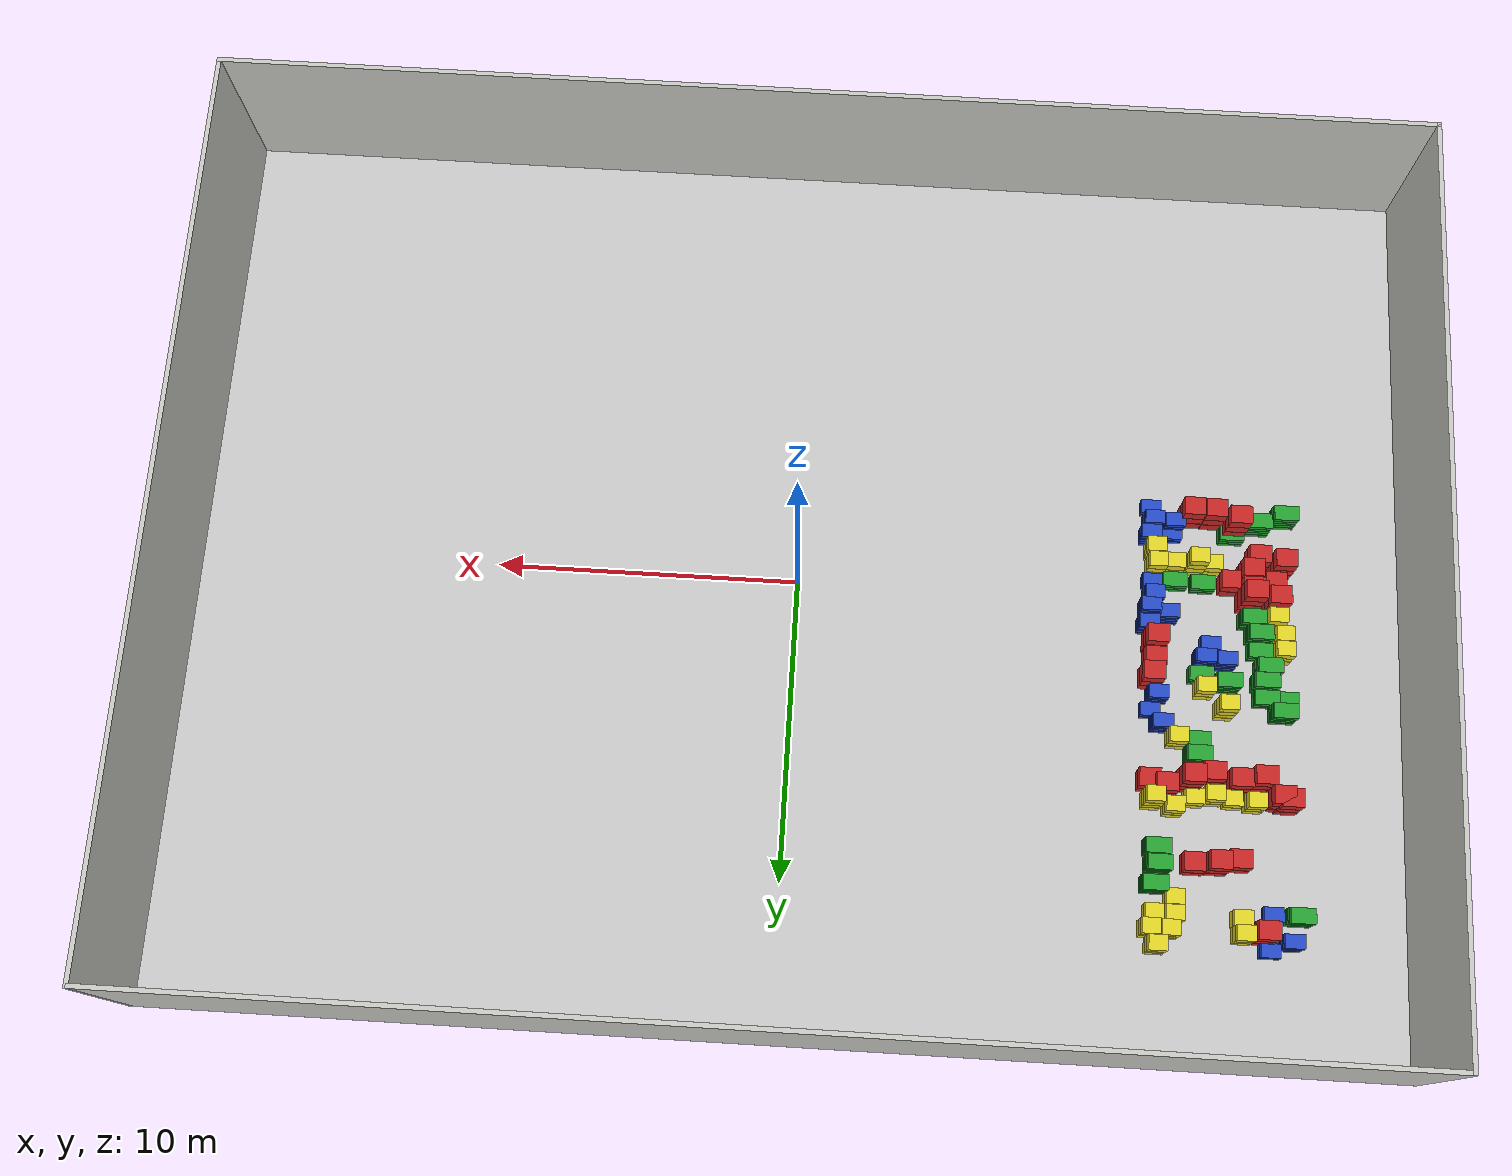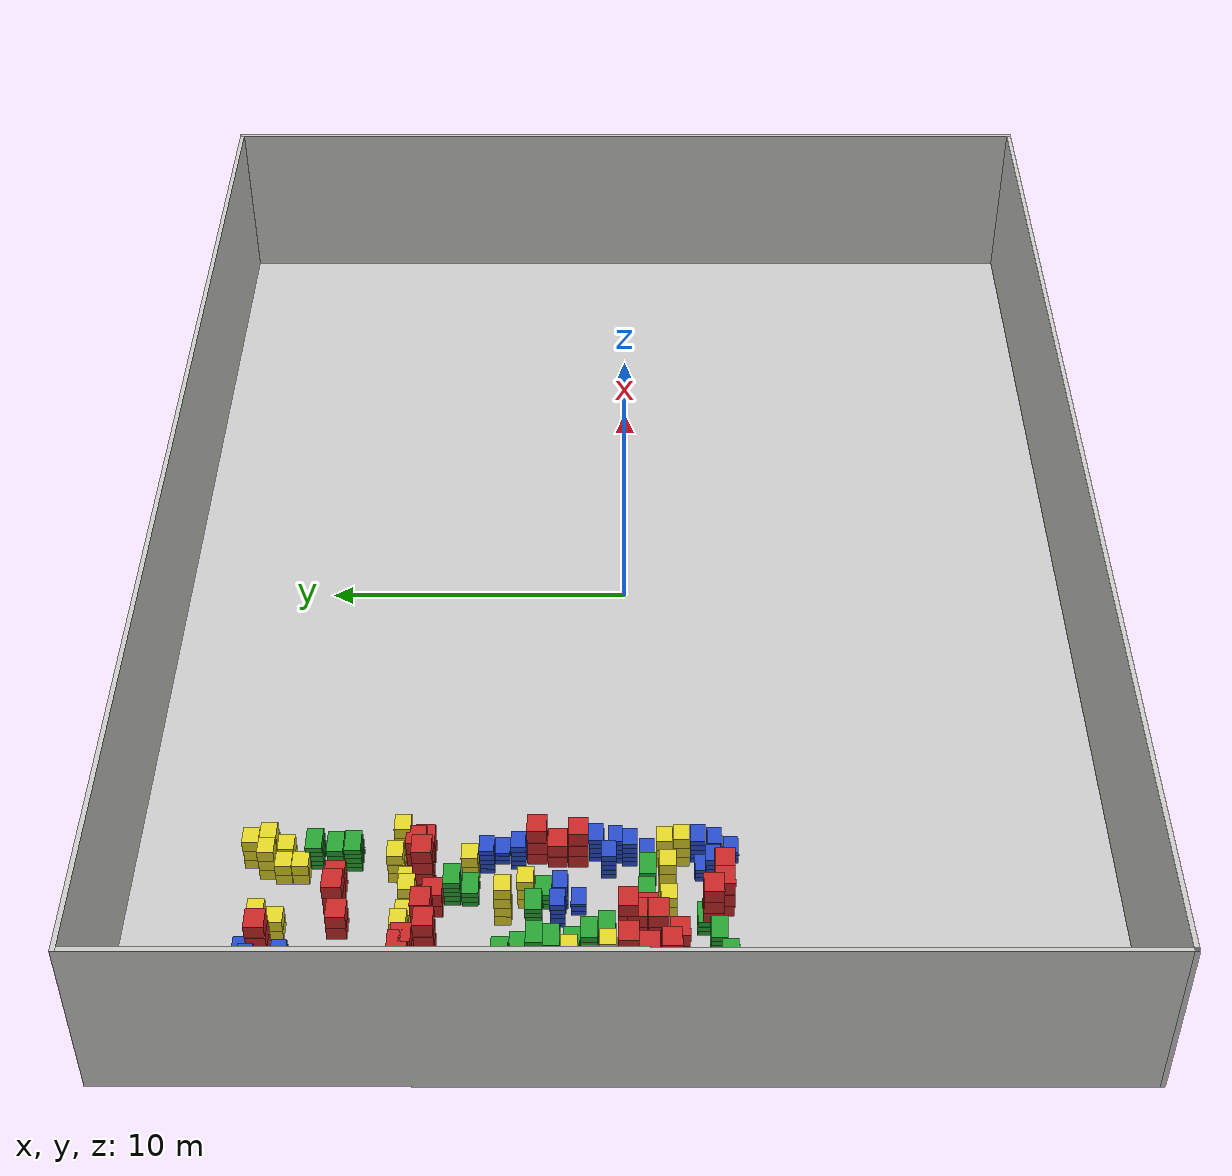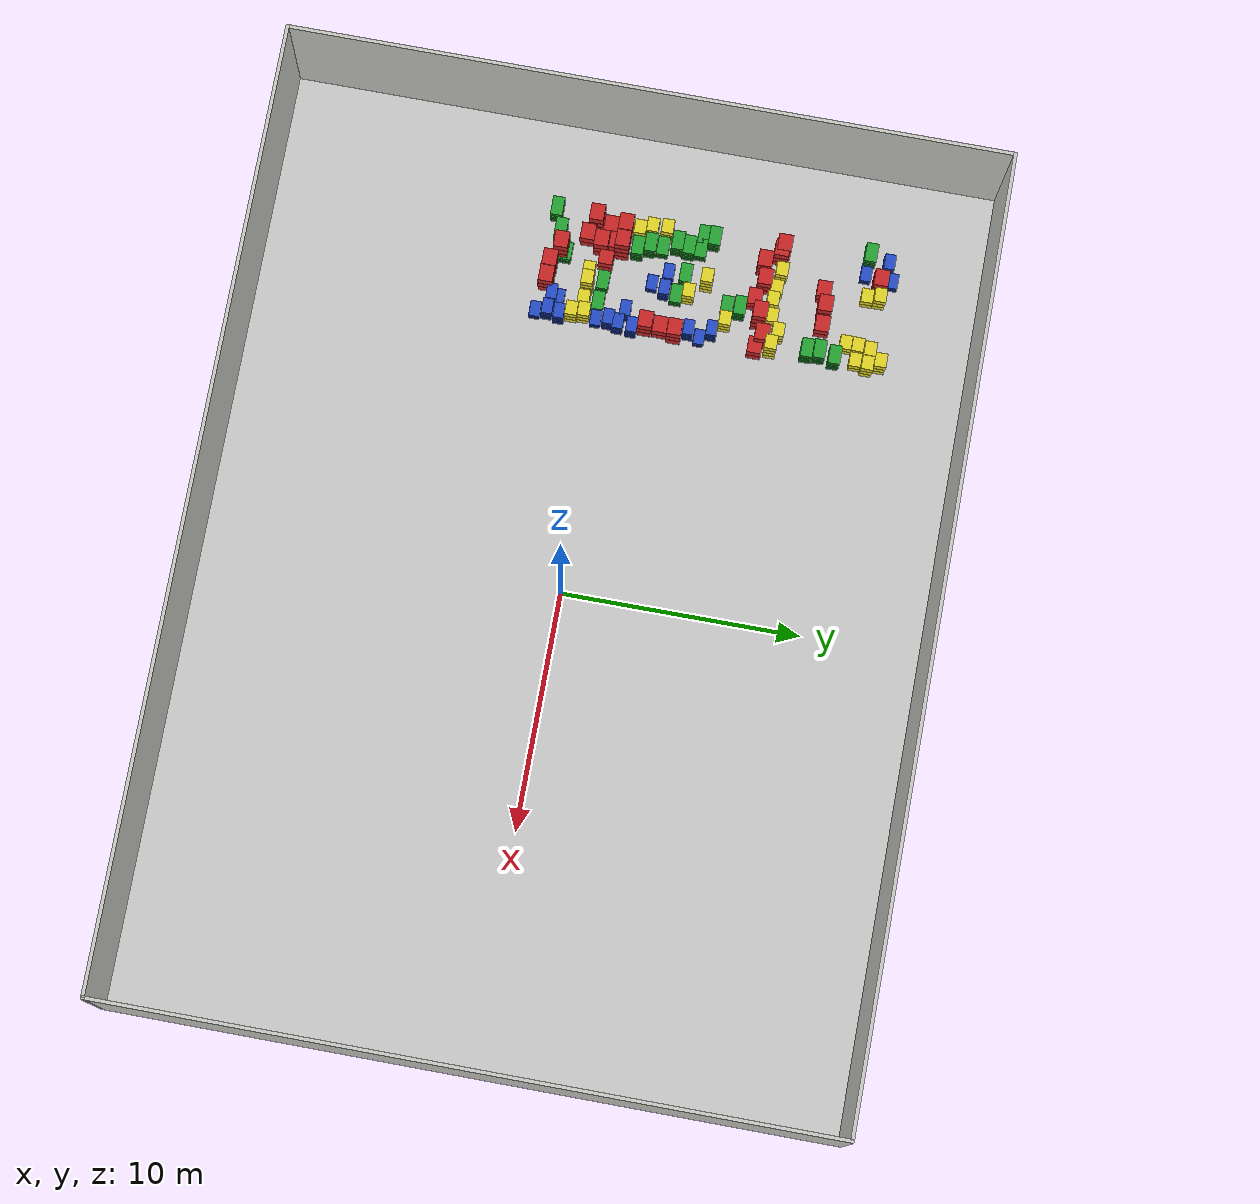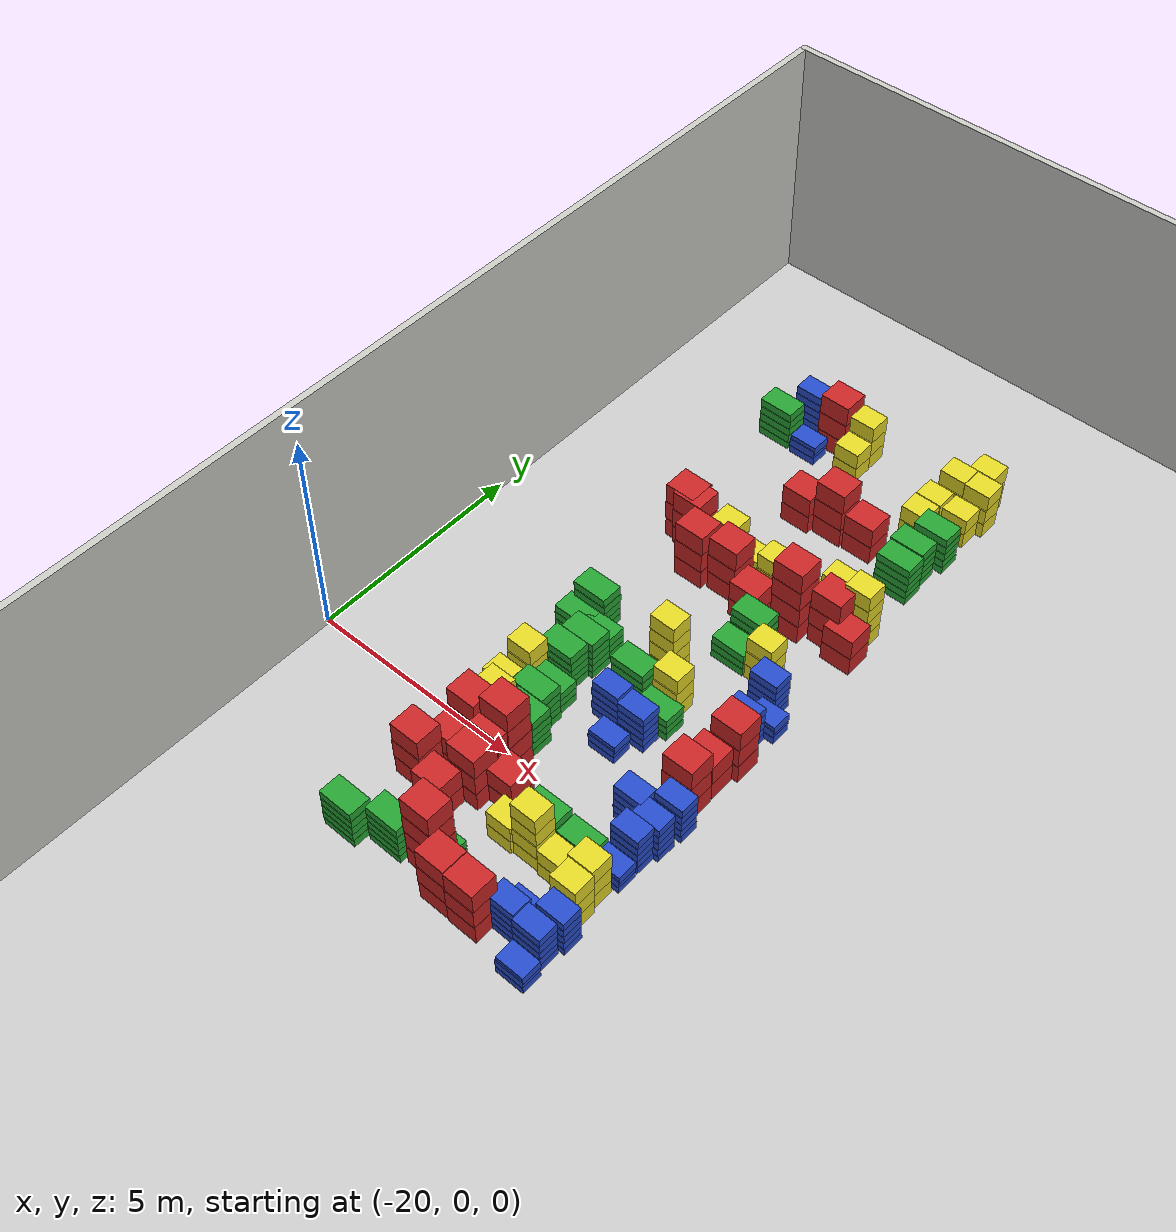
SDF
<?xml version="1.0" ?>
<sdf version="1.6">
  <world name="default">
    <include>
      <uri>model://sun</uri>
    </include>
    <include>
      <uri>model://factory_floor</uri>
    </include>
    <include>
      <uri>model://factory_outer_frame</uri>
    </include>

    <model name='baggage_D_x5'>
      <model name='baggage_D_0'>
        <static>1</static>
        <link name='link'>
          <collision name='collision'>
            <geometry>
              <box>
                <size>0.8 0.5 0.2</size>
              </box>
            </geometry>
          </collision>
          <visual name='visual'>
            <geometry>
              <box>
                <size>0.8 0.5 0.2</size>
              </box>
            </geometry>
            <material>
              <script>
                <uri>file://media/materials/scripts/gazebo.material</uri>
                <name>Gazebo/Green</name>
              </script>
            </material>
          </visual>
        </link>
        <pose frame=''>0 0 0.1 0 -0 0</pose>
      </model>
      <model name='baggage_D_1'>
        <static>1</static>
        <link name='link'>
          <collision name='collision'>
            <geometry>
              <box>
                <size>0.8 0.5 0.2</size>
              </box>
            </geometry>
          </collision>
          <visual name='visual'>
            <geometry>
              <box>
                <size>0.8 0.5 0.2</size>
              </box>
            </geometry>
            <material>
              <script>
                <uri>file://media/materials/scripts/gazebo.material</uri>
                <name>Gazebo/Green</name>
              </script>
            </material>
          </visual>
        </link>
        <pose frame=''>-0.0065 -0.0092 0.3 0 -0 0</pose>
      </model>
      <model name='baggage_D_2'>
        <static>1</static>
        <link name='link'>
          <collision name='collision'>
            <geometry>
              <box>
                <size>0.8 0.5 0.2</size>
              </box>
            </geometry>
          </collision>
          <visual name='visual'>
            <geometry>
              <box>
                <size>0.8 0.5 0.2</size>
              </box>
            </geometry>
            <material>
              <script>
                <uri>file://media/materials/scripts/gazebo.material</uri>
                <name>Gazebo/Green</name>
              </script>
            </material>
          </visual>
        </link>
        <pose frame=''>0.005 -0.0052 0.5 0 -0 0</pose>
      </model>
      <model name='baggage_D_3'>
        <static>1</static>
        <link name='link'>
          <collision name='collision'>
            <geometry>
              <box>
                <size>0.8 0.5 0.2</size>
              </box>
            </geometry>
          </collision>
          <visual name='visual'>
            <geometry>
              <box>
                <size>0.8 0.5 0.2</size>
              </box>
            </geometry>
            <material>
              <script>
                <uri>file://media/materials/scripts/gazebo.material</uri>
                <name>Gazebo/Green</name>
              </script>
            </material>
          </visual>
        </link>
        <pose frame=''>0.0074 0.0002 0.7 0 -0 0</pose>
      </model>
      <model name='baggage_D_4'>
        <static>1</static>
        <link name='link'>
          <collision name='collision'>
            <geometry>
              <box>
                <size>0.8 0.5 0.2</size>
              </box>
            </geometry>
          </collision>
          <visual name='visual'>
            <geometry>
              <box>
                <size>0.8 0.5 0.2</size>
              </box>
            </geometry>
            <material>
              <script>
                <uri>file://media/materials/scripts/gazebo.material</uri>
                <name>Gazebo/Green</name>
              </script>
            </material>
          </visual>
        </link>
        <pose frame=''>-0.006 0.0081 0.9 0 -0 0</pose>
      </model>
      <pose frame=''>-16.0603 -3.09138 0 0 -0 0</pose>
    </model>
    <model name='baggage_D_x5_0'>
      <model name='baggage_D_0'>
        <static>1</static>
        <link name='link'>
          <collision name='collision'>
            <geometry>
              <box>
                <size>0.8 0.5 0.2</size>
              </box>
            </geometry>
          </collision>
          <visual name='visual'>
            <geometry>
              <box>
                <size>0.8 0.5 0.2</size>
              </box>
            </geometry>
            <material>
              <script>
                <uri>file://media/materials/scripts/gazebo.material</uri>
                <name>Gazebo/Green</name>
              </script>
            </material>
          </visual>
        </link>
        <pose frame=''>0 0 0.1 0 -0 0</pose>
      </model>
      <model name='baggage_D_1'>
        <static>1</static>
        <link name='link'>
          <collision name='collision'>
            <geometry>
              <box>
                <size>0.8 0.5 0.2</size>
              </box>
            </geometry>
          </collision>
          <visual name='visual'>
            <geometry>
              <box>
                <size>0.8 0.5 0.2</size>
              </box>
            </geometry>
            <material>
              <script>
                <uri>file://media/materials/scripts/gazebo.material</uri>
                <name>Gazebo/Green</name>
              </script>
            </material>
          </visual>
        </link>
        <pose frame=''>-0.0065 -0.0092 0.3 0 -0 0</pose>
      </model>
      <model name='baggage_D_2'>
        <static>1</static>
        <link name='link'>
          <collision name='collision'>
            <geometry>
              <box>
                <size>0.8 0.5 0.2</size>
              </box>
            </geometry>
          </collision>
          <visual name='visual'>
            <geometry>
              <box>
                <size>0.8 0.5 0.2</size>
              </box>
            </geometry>
            <material>
              <script>
                <uri>file://media/materials/scripts/gazebo.material</uri>
                <name>Gazebo/Green</name>
              </script>
            </material>
          </visual>
        </link>
        <pose frame=''>0.005 -0.0052 0.5 0 -0 0</pose>
      </model>
      <model name='baggage_D_3'>
        <static>1</static>
        <link name='link'>
          <collision name='collision'>
            <geometry>
              <box>
                <size>0.8 0.5 0.2</size>
              </box>
            </geometry>
          </collision>
          <visual name='visual'>
            <geometry>
              <box>
                <size>0.8 0.5 0.2</size>
              </box>
            </geometry>
            <material>
              <script>
                <uri>file://media/materials/scripts/gazebo.material</uri>
                <name>Gazebo/Green</name>
              </script>
            </material>
          </visual>
        </link>
        <pose frame=''>0.0074 0.0002 0.7 0 -0 0</pose>
      </model>
      <model name='baggage_D_4'>
        <static>1</static>
        <link name='link'>
          <collision name='collision'>
            <geometry>
              <box>
                <size>0.8 0.5 0.2</size>
              </box>
            </geometry>
          </collision>
          <visual name='visual'>
            <geometry>
              <box>
                <size>0.8 0.5 0.2</size>
              </box>
            </geometry>
            <material>
              <script>
                <uri>file://media/materials/scripts/gazebo.material</uri>
                <name>Gazebo/Green</name>
              </script>
            </material>
          </visual>
        </link>
        <pose frame=''>-0.006 0.0081 0.9 0 -0 0</pose>
      </model>
      <pose frame=''>-15.1916 -2.77971 0 0 -0 0</pose>
    </model>
    <model name='baggage_D_x3'>
      <model name='baggage_D_0'>
        <static>1</static>
        <link name='link'>
          <collision name='collision'>
            <geometry>
              <box>
                <size>0.8 0.5 0.2</size>
              </box>
            </geometry>
          </collision>
          <visual name='visual'>
            <geometry>
              <box>
                <size>0.8 0.5 0.2</size>
              </box>
            </geometry>
            <material>
              <script>
                <uri>file://media/materials/scripts/gazebo.material</uri>
                <name>Gazebo/Green</name>
              </script>
            </material>
          </visual>
        </link>
        <pose frame=''>0 0 0.1 0 -0 0</pose>
      </model>
      <model name='baggage_D_1'>
        <static>1</static>
        <link name='link'>
          <collision name='collision'>
            <geometry>
              <box>
                <size>0.8 0.5 0.2</size>
              </box>
            </geometry>
          </collision>
          <visual name='visual'>
            <geometry>
              <box>
                <size>0.8 0.5 0.2</size>
              </box>
            </geometry>
            <material>
              <script>
                <uri>file://media/materials/scripts/gazebo.material</uri>
                <name>Gazebo/Green</name>
              </script>
            </material>
          </visual>
        </link>
        <pose frame=''>-0.0056 0.0083 0.3 0 -0 0</pose>
      </model>
      <model name='baggage_D_2'>
        <static>1</static>
        <link name='link'>
          <collision name='collision'>
            <geometry>
              <box>
                <size>0.8 0.5 0.2</size>
              </box>
            </geometry>
          </collision>
          <visual name='visual'>
            <geometry>
              <box>
                <size>0.8 0.5 0.2</size>
              </box>
            </geometry>
            <material>
              <script>
                <uri>file://media/materials/scripts/gazebo.material</uri>
                <name>Gazebo/Green</name>
              </script>
            </material>
          </visual>
        </link>
        <pose frame=''>0.0053 0.0057 0.5 0 -0 0</pose>
      </model>
      <pose frame=''>-14.3395 -2.41254 0 0 -0 0</pose>
    </model>
    <model name='baggage_A_x4'>
      <model name='baggage_A_0'>
        <static>1</static>
        <link name='link'>
          <collision name='collision'>
            <geometry>
              <box>
                <size>0.7 0.6 0.5</size>
              </box>
            </geometry>
          </collision>
          <visual name='visual'>
            <geometry>
              <box>
                <size>0.7 0.6 0.5</size>
              </box>
            </geometry>
            <material>
              <script>
                <uri>file://media/materials/scripts/gazebo.material</uri>
                <name>Gazebo/Red</name>
              </script>
            </material>
          </visual>
        </link>
        <pose frame=''>0 0 0.25 0 -0 0</pose>
      </model>
      <model name='baggage_A_1'>
        <static>1</static>
        <link name='link'>
          <collision name='collision'>
            <geometry>
              <box>
                <size>0.7 0.6 0.5</size>
              </box>
            </geometry>
          </collision>
          <visual name='visual'>
            <geometry>
              <box>
                <size>0.7 0.6 0.5</size>
              </box>
            </geometry>
            <material>
              <script>
                <uri>file://media/materials/scripts/gazebo.material</uri>
                <name>Gazebo/Red</name>
              </script>
            </material>
          </visual>
        </link>
        <pose frame=''>0.0053 0.0033 0.75 0 -0 0</pose>
      </model>
      <model name='baggage_A_2'>
        <static>1</static>
        <link name='link'>
          <collision name='collision'>
            <geometry>
              <box>
                <size>0.7 0.6 0.5</size>
              </box>
            </geometry>
          </collision>
          <visual name='visual'>
            <geometry>
              <box>
                <size>0.7 0.6 0.5</size>
              </box>
            </geometry>
            <material>
              <script>
                <uri>file://media/materials/scripts/gazebo.material</uri>
                <name>Gazebo/Red</name>
              </script>
            </material>
          </visual>
        </link>
        <pose frame=''>-0.0056 -0.0003 1.25 0 -0 0</pose>
      </model>
      <model name='baggage_A_3'>
        <static>1</static>
        <link name='link'>
          <collision name='collision'>
            <geometry>
              <box>
                <size>0.7 0.6 0.5</size>
              </box>
            </geometry>
          </collision>
          <visual name='visual'>
            <geometry>
              <box>
                <size>0.7 0.6 0.5</size>
              </box>
            </geometry>
            <material>
              <script>
                <uri>file://media/materials/scripts/gazebo.material</uri>
                <name>Gazebo/Red</name>
              </script>
            </material>
          </visual>
        </link>
        <pose frame=''>-0.0098 0.0065 1.75 0 -0 0</pose>
      </model>
      <pose frame=''>-14.3613 -2.61485 0 0 -0 0</pose>
    </model>
    <model name='baggage_A_x3'>
      <model name='baggage_A_0'>
        <static>1</static>
        <link name='link'>
          <collision name='collision'>
            <geometry>
              <box>
                <size>0.7 0.6 0.5</size>
              </box>
            </geometry>
          </collision>
          <visual name='visual'>
            <geometry>
              <box>
                <size>0.7 0.6 0.5</size>
              </box>
            </geometry>
            <material>
              <script>
                <uri>file://media/materials/scripts/gazebo.material</uri>
                <name>Gazebo/Red</name>
              </script>
            </material>
          </visual>
        </link>
        <pose frame=''>0 0 0.25 0 -0 0</pose>
      </model>
      <model name='baggage_A_1'>
        <static>1</static>
        <link name='link'>
          <collision name='collision'>
            <geometry>
              <box>
                <size>0.7 0.6 0.5</size>
              </box>
            </geometry>
          </collision>
          <visual name='visual'>
            <geometry>
              <box>
                <size>0.7 0.6 0.5</size>
              </box>
            </geometry>
            <material>
              <script>
                <uri>file://media/materials/scripts/gazebo.material</uri>
                <name>Gazebo/Red</name>
              </script>
            </material>
          </visual>
        </link>
        <pose frame=''>-0.006 -0.0077 0.75 0 -0 0</pose>
      </model>
      <model name='baggage_A_2'>
        <static>1</static>
        <link name='link'>
          <collision name='collision'>
            <geometry>
              <box>
                <size>0.7 0.6 0.5</size>
              </box>
            </geometry>
          </collision>
          <visual name='visual'>
            <geometry>
              <box>
                <size>0.7 0.6 0.5</size>
              </box>
            </geometry>
            <material>
              <script>
                <uri>file://media/materials/scripts/gazebo.material</uri>
                <name>Gazebo/Red</name>
              </script>
            </material>
          </visual>
        </link>
        <pose frame=''>0.0045 0.0005 1.25 0 -0 0</pose>
      </model>
      <pose frame=''>-13.6814 -2.97255 0 0 -0 0</pose>
    </model>
    <model name='baggage_A_x3_0'>
      <model name='baggage_A_0'>
        <static>1</static>
        <link name='link'>
          <collision name='collision'>
            <geometry>
              <box>
                <size>0.7 0.6 0.5</size>
              </box>
            </geometry>
          </collision>
          <visual name='visual'>
            <geometry>
              <box>
                <size>0.7 0.6 0.5</size>
              </box>
            </geometry>
            <material>
              <script>
                <uri>file://media/materials/scripts/gazebo.material</uri>
                <name>Gazebo/Red</name>
              </script>
            </material>
          </visual>
        </link>
        <pose frame=''>0 0 0.25 0 -0 0</pose>
      </model>
      <model name='baggage_A_1'>
        <static>1</static>
        <link name='link'>
          <collision name='collision'>
            <geometry>
              <box>
                <size>0.7 0.6 0.5</size>
              </box>
            </geometry>
          </collision>
          <visual name='visual'>
            <geometry>
              <box>
                <size>0.7 0.6 0.5</size>
              </box>
            </geometry>
            <material>
              <script>
                <uri>file://media/materials/scripts/gazebo.material</uri>
                <name>Gazebo/Red</name>
              </script>
            </material>
          </visual>
        </link>
        <pose frame=''>-0.006 -0.0077 0.75 0 -0 0</pose>
      </model>
      <model name='baggage_A_2'>
        <static>1</static>
        <link name='link'>
          <collision name='collision'>
            <geometry>
              <box>
                <size>0.7 0.6 0.5</size>
              </box>
            </geometry>
          </collision>
          <visual name='visual'>
            <geometry>
              <box>
                <size>0.7 0.6 0.5</size>
              </box>
            </geometry>
            <material>
              <script>
                <uri>file://media/materials/scripts/gazebo.material</uri>
                <name>Gazebo/Red</name>
              </script>
            </material>
          </visual>
        </link>
        <pose frame=''>0.0045 0.0005 1.25 0 -0 0</pose>
      </model>
      <pose frame=''>-12.9672 -2.99066 0 0 -0 0</pose>
    </model>
    <model name='baggage_B_x3'>
      <model name='baggage_B_0'>
        <static>1</static>
        <link name='link'>
          <collision name='collision'>
            <geometry>
              <box>
                <size>0.65 0.45 0.2</size>
              </box>
            </geometry>
          </collision>
          <visual name='visual'>
            <geometry>
              <box>
                <size>0.65 0.45 0.2</size>
              </box>
            </geometry>
            <material>
              <script>
                <uri>file://media/materials/scripts/gazebo.material</uri>
                <name>Gazebo/Blue</name>
              </script>
            </material>
          </visual>
        </link>
        <pose frame=''>0 0 0.1 0 -0 0</pose>
      </model>
      <model name='baggage_B_1'>
        <static>1</static>
        <link name='link'>
          <collision name='collision'>
            <geometry>
              <box>
                <size>0.65 0.45 0.2</size>
              </box>
            </geometry>
          </collision>
          <visual name='visual'>
            <geometry>
              <box>
                <size>0.65 0.45 0.2</size>
              </box>
            </geometry>
            <material>
              <script>
                <uri>file://media/materials/scripts/gazebo.material</uri>
                <name>Gazebo/Blue</name>
              </script>
            </material>
          </visual>
        </link>
        <pose frame=''>0.0028 -0.0086 0.3 0 -0 0</pose>
      </model>
      <model name='baggage_B_2'>
        <static>1</static>
        <link name='link'>
          <collision name='collision'>
            <geometry>
              <box>
                <size>0.65 0.45 0.2</size>
              </box>
            </geometry>
          </collision>
          <visual name='visual'>
            <geometry>
              <box>
                <size>0.65 0.45 0.2</size>
              </box>
            </geometry>
            <material>
              <script>
                <uri>file://media/materials/scripts/gazebo.material</uri>
                <name>Gazebo/Blue</name>
              </script>
            </material>
          </visual>
        </link>
        <pose frame=''>0.0092 0.006 0.4 0 -0 0</pose>
      </model>
      <pose frame=''>-11.6581 -3.23288 0 0 -0 0</pose>
    </model>
    <model name='baggage_B_x5'>
      <model name='baggage_B_0'>
        <static>1</static>
        <link name='link'>
          <collision name='collision'>
            <geometry>
              <box>
                <size>0.65 0.45 0.2</size>
              </box>
            </geometry>
          </collision>
          <visual name='visual'>
            <geometry>
              <box>
                <size>0.65 0.45 0.2</size>
              </box>
            </geometry>
            <material>
              <script>
                <uri>file://media/materials/scripts/gazebo.material</uri>
                <name>Gazebo/Blue</name>
              </script>
            </material>
          </visual>
        </link>
        <pose frame=''>0 0 0.1 0 -0 0</pose>
      </model>
      <model name='baggage_B_1'>
        <static>1</static>
        <link name='link'>
          <collision name='collision'>
            <geometry>
              <box>
                <size>0.65 0.45 0.2</size>
              </box>
            </geometry>
          </collision>
          <visual name='visual'>
            <geometry>
              <box>
                <size>0.65 0.45 0.2</size>
              </box>
            </geometry>
            <material>
              <script>
                <uri>file://media/materials/scripts/gazebo.material</uri>
                <name>Gazebo/Blue</name>
              </script>
            </material>
          </visual>
        </link>
        <pose frame=''>-0.0014 -0.0091 0.3 0 -0 0</pose>
      </model>
      <model name='baggage_B_2'>
        <static>1</static>
        <link name='link'>
          <collision name='collision'>
            <geometry>
              <box>
                <size>0.65 0.45 0.2</size>
              </box>
            </geometry>
          </collision>
          <visual name='visual'>
            <geometry>
              <box>
                <size>0.65 0.45 0.2</size>
              </box>
            </geometry>
            <material>
              <script>
                <uri>file://media/materials/scripts/gazebo.material</uri>
                <name>Gazebo/Blue</name>
              </script>
            </material>
          </visual>
        </link>
        <pose frame=''>0.0076 -0.0066 0.5 0 -0 0</pose>
      </model>
      <model name='baggage_B_3'>
        <static>1</static>
        <link name='link'>
          <collision name='collision'>
            <geometry>
              <box>
                <size>0.65 0.45 0.2</size>
              </box>
            </geometry>
          </collision>
          <visual name='visual'>
            <geometry>
              <box>
                <size>0.65 0.45 0.2</size>
              </box>
            </geometry>
            <material>
              <script>
                <uri>file://media/materials/scripts/gazebo.material</uri>
                <name>Gazebo/Blue</name>
              </script>
            </material>
          </visual>
        </link>
        <pose frame=''>0 -0.0032 0.7 0 -0 0</pose>
      </model>
      <model name='baggage_B_4'>
        <static>1</static>
        <link name='link'>
          <collision name='collision'>
            <geometry>
              <box>
                <size>0.65 0.45 0.2</size>
              </box>
            </geometry>
          </collision>
          <visual name='visual'>
            <geometry>
              <box>
                <size>0.65 0.45 0.2</size>
              </box>
            </geometry>
            <material>
              <script>
                <uri>file://media/materials/scripts/gazebo.material</uri>
                <name>Gazebo/Blue</name>
              </script>
            </material>
          </visual>
        </link>
        <pose frame=''>0.0023 0.0073 0.9 0 -0 0</pose>
      </model>
      <pose frame=''>-11.7207 -2.7222 0 0 -0 0</pose>
    </model>
    <model name='baggage_B_x5_0'>
      <model name='baggage_B_0'>
        <static>1</static>
        <link name='link'>
          <collision name='collision'>
            <geometry>
              <box>
                <size>0.65 0.45 0.2</size>
              </box>
            </geometry>
          </collision>
          <visual name='visual'>
            <geometry>
              <box>
                <size>0.65 0.45 0.2</size>
              </box>
            </geometry>
            <material>
              <script>
                <uri>file://media/materials/scripts/gazebo.material</uri>
                <name>Gazebo/Blue</name>
              </script>
            </material>
          </visual>
        </link>
        <pose frame=''>0 0 0.1 0 -0 0</pose>
      </model>
      <model name='baggage_B_1'>
        <static>1</static>
        <link name='link'>
          <collision name='collision'>
            <geometry>
              <box>
                <size>0.65 0.45 0.2</size>
              </box>
            </geometry>
          </collision>
          <visual name='visual'>
            <geometry>
              <box>
                <size>0.65 0.45 0.2</size>
              </box>
            </geometry>
            <material>
              <script>
                <uri>file://media/materials/scripts/gazebo.material</uri>
                <name>Gazebo/Blue</name>
              </script>
            </material>
          </visual>
        </link>
        <pose frame=''>-0.0014 -0.0091 0.3 0 -0 0</pose>
      </model>
      <model name='baggage_B_2'>
        <static>1</static>
        <link name='link'>
          <collision name='collision'>
            <geometry>
              <box>
                <size>0.65 0.45 0.2</size>
              </box>
            </geometry>
          </collision>
          <visual name='visual'>
            <geometry>
              <box>
                <size>0.65 0.45 0.2</size>
              </box>
            </geometry>
            <material>
              <script>
                <uri>file://media/materials/scripts/gazebo.material</uri>
                <name>Gazebo/Blue</name>
              </script>
            </material>
          </visual>
        </link>
        <pose frame=''>0.0076 -0.0066 0.5 0 -0 0</pose>
      </model>
      <model name='baggage_B_3'>
        <static>1</static>
        <link name='link'>
          <collision name='collision'>
            <geometry>
              <box>
                <size>0.65 0.45 0.2</size>
              </box>
            </geometry>
          </collision>
          <visual name='visual'>
            <geometry>
              <box>
                <size>0.65 0.45 0.2</size>
              </box>
            </geometry>
            <material>
              <script>
                <uri>file://media/materials/scripts/gazebo.material</uri>
                <name>Gazebo/Blue</name>
              </script>
            </material>
          </visual>
        </link>
        <pose frame=''>0 -0.0032 0.7 0 -0 0</pose>
      </model>
      <model name='baggage_B_4'>
        <static>1</static>
        <link name='link'>
          <collision name='collision'>
            <geometry>
              <box>
                <size>0.65 0.45 0.2</size>
              </box>
            </geometry>
          </collision>
          <visual name='visual'>
            <geometry>
              <box>
                <size>0.65 0.45 0.2</size>
              </box>
            </geometry>
            <material>
              <script>
                <uri>file://media/materials/scripts/gazebo.material</uri>
                <name>Gazebo/Blue</name>
              </script>
            </material>
          </visual>
        </link>
        <pose frame=''>0.0023 0.0073 0.9 0 -0 0</pose>
      </model>
      <pose frame=''>-12.3958 -2.65895 0 0 -0 0</pose>
    </model>
    <model name='baggage_A_x3_1'>
      <model name='baggage_A_0'>
        <static>1</static>
        <link name='link'>
          <collision name='collision'>
            <geometry>
              <box>
                <size>0.7 0.6 0.5</size>
              </box>
            </geometry>
          </collision>
          <visual name='visual'>
            <geometry>
              <box>
                <size>0.7 0.6 0.5</size>
              </box>
            </geometry>
            <material>
              <script>
                <uri>file://media/materials/scripts/gazebo.material</uri>
                <name>Gazebo/Red</name>
              </script>
            </material>
          </visual>
        </link>
        <pose frame=''>0 0 0.25 0 -0 0</pose>
      </model>
      <model name='baggage_A_1'>
        <static>1</static>
        <link name='link'>
          <collision name='collision'>
            <geometry>
              <box>
                <size>0.7 0.6 0.5</size>
              </box>
            </geometry>
          </collision>
          <visual name='visual'>
            <geometry>
              <box>
                <size>0.7 0.6 0.5</size>
              </box>
            </geometry>
            <material>
              <script>
                <uri>file://media/materials/scripts/gazebo.material</uri>
                <name>Gazebo/Red</name>
              </script>
            </material>
          </visual>
        </link>
        <pose frame=''>-0.006 -0.0077 0.75 0 -0 0</pose>
      </model>
      <model name='baggage_A_2'>
        <static>1</static>
        <link name='link'>
          <collision name='collision'>
            <geometry>
              <box>
                <size>0.7 0.6 0.5</size>
              </box>
            </geometry>
          </collision>
          <visual name='visual'>
            <geometry>
              <box>
                <size>0.7 0.6 0.5</size>
              </box>
            </geometry>
            <material>
              <script>
                <uri>file://media/materials/scripts/gazebo.material</uri>
                <name>Gazebo/Red</name>
              </script>
            </material>
          </visual>
        </link>
        <pose frame=''>0.0045 0.0005 1.25 0 -0 0</pose>
      </model>
      <pose frame=''>-15.9557 -1.37192 0 0 -0 0</pose>
    </model>
    <model name='baggage_A_x2'>
      <model name='baggage_A_0'>
        <static>1</static>
        <link name='link'>
          <collision name='collision'>
            <geometry>
              <box>
                <size>0.7 0.6 0.5</size>
              </box>
            </geometry>
          </collision>
          <visual name='visual'>
            <geometry>
              <box>
                <size>0.7 0.6 0.5</size>
              </box>
            </geometry>
            <material>
              <script>
                <uri>file://media/materials/scripts/gazebo.material</uri>
                <name>Gazebo/Red</name>
              </script>
            </material>
          </visual>
        </link>
        <pose frame=''>0 0 0.25 0 -0 0</pose>
      </model>
      <model name='baggage_A_1'>
        <static>1</static>
        <link name='link'>
          <collision name='collision'>
            <geometry>
              <box>
                <size>0.7 0.6 0.5</size>
              </box>
            </geometry>
          </collision>
          <visual name='visual'>
            <geometry>
              <box>
                <size>0.7 0.6 0.5</size>
              </box>
            </geometry>
            <material>
              <script>
                <uri>file://media/materials/scripts/gazebo.material</uri>
                <name>Gazebo/Red</name>
              </script>
            </material>
          </visual>
        </link>
        <pose frame=''>0.0063 -0.0062 0.75 0 -0 0</pose>
      </model>
      <pose frame=''>-15.7141 -0.71732 0 0 -0 0</pose>
    </model>
    <model name='baggage_A_x3_2'>
      <model name='baggage_A_0'>
        <static>1</static>
        <link name='link'>
          <collision name='collision'>
            <geometry>
              <box>
                <size>0.7 0.6 0.5</size>
              </box>
            </geometry>
          </collision>
          <visual name='visual'>
            <geometry>
              <box>
                <size>0.7 0.6 0.5</size>
              </box>
            </geometry>
            <material>
              <script>
                <uri>file://media/materials/scripts/gazebo.material</uri>
                <name>Gazebo/Red</name>
              </script>
            </material>
          </visual>
        </link>
        <pose frame=''>0 0 0.25 0 -0 0</pose>
      </model>
      <model name='baggage_A_1'>
        <static>1</static>
        <link name='link'>
          <collision name='collision'>
            <geometry>
              <box>
                <size>0.7 0.6 0.5</size>
              </box>
            </geometry>
          </collision>
          <visual name='visual'>
            <geometry>
              <box>
                <size>0.7 0.6 0.5</size>
              </box>
            </geometry>
            <material>
              <script>
                <uri>file://media/materials/scripts/gazebo.material</uri>
                <name>Gazebo/Red</name>
              </script>
            </material>
          </visual>
        </link>
        <pose frame=''>-0.006 -0.0077 0.75 0 -0 0</pose>
      </model>
      <model name='baggage_A_2'>
        <static>1</static>
        <link name='link'>
          <collision name='collision'>
            <geometry>
              <box>
                <size>0.7 0.6 0.5</size>
              </box>
            </geometry>
          </collision>
          <visual name='visual'>
            <geometry>
              <box>
                <size>0.7 0.6 0.5</size>
              </box>
            </geometry>
            <material>
              <script>
                <uri>file://media/materials/scripts/gazebo.material</uri>
                <name>Gazebo/Red</name>
              </script>
            </material>
          </visual>
        </link>
        <pose frame=''>0.0045 0.0005 1.25 0 -0 0</pose>
      </model>
      <pose frame=''>-15.7621 -0.111141 0 0 -0 0</pose>
    </model>
    <model name='baggage_A_x3_3'>
      <model name='baggage_A_0'>
        <static>1</static>
        <link name='link'>
          <collision name='collision'>
            <geometry>
              <box>
                <size>0.7 0.6 0.5</size>
              </box>
            </geometry>
          </collision>
          <visual name='visual'>
            <geometry>
              <box>
                <size>0.7 0.6 0.5</size>
              </box>
            </geometry>
            <material>
              <script>
                <uri>file://media/materials/scripts/gazebo.material</uri>
                <name>Gazebo/Red</name>
              </script>
            </material>
          </visual>
        </link>
        <pose frame=''>0 0 0.25 0 -0 0</pose>
      </model>
      <model name='baggage_A_1'>
        <static>1</static>
        <link name='link'>
          <collision name='collision'>
            <geometry>
              <box>
                <size>0.7 0.6 0.5</size>
              </box>
            </geometry>
          </collision>
          <visual name='visual'>
            <geometry>
              <box>
                <size>0.7 0.6 0.5</size>
              </box>
            </geometry>
            <material>
              <script>
                <uri>file://media/materials/scripts/gazebo.material</uri>
                <name>Gazebo/Red</name>
              </script>
            </material>
          </visual>
        </link>
        <pose frame=''>-0.006 -0.0077 0.75 0 -0 0</pose>
      </model>
      <model name='baggage_A_2'>
        <static>1</static>
        <link name='link'>
          <collision name='collision'>
            <geometry>
              <box>
                <size>0.7 0.6 0.5</size>
              </box>
            </geometry>
          </collision>
          <visual name='visual'>
            <geometry>
              <box>
                <size>0.7 0.6 0.5</size>
              </box>
            </geometry>
            <material>
              <script>
                <uri>file://media/materials/scripts/gazebo.material</uri>
                <name>Gazebo/Red</name>
              </script>
            </material>
          </visual>
        </link>
        <pose frame=''>0.0045 0.0005 1.25 0 -0 0</pose>
      </model>
      <pose frame=''>-14.902 -0.36223 0 0 -0 0</pose>
    </model>
    <model name='baggage_A_x3_4'>
      <model name='baggage_A_0'>
        <static>1</static>
        <link name='link'>
          <collision name='collision'>
            <geometry>
              <box>
                <size>0.7 0.6 0.5</size>
              </box>
            </geometry>
          </collision>
          <visual name='visual'>
            <geometry>
              <box>
                <size>0.7 0.6 0.5</size>
              </box>
            </geometry>
            <material>
              <script>
                <uri>file://media/materials/scripts/gazebo.material</uri>
                <name>Gazebo/Red</name>
              </script>
            </material>
          </visual>
        </link>
        <pose frame=''>0 0 0.25 0 -0 0</pose>
      </model>
      <model name='baggage_A_1'>
        <static>1</static>
        <link name='link'>
          <collision name='collision'>
            <geometry>
              <box>
                <size>0.7 0.6 0.5</size>
              </box>
            </geometry>
          </collision>
          <visual name='visual'>
            <geometry>
              <box>
                <size>0.7 0.6 0.5</size>
              </box>
            </geometry>
            <material>
              <script>
                <uri>file://media/materials/scripts/gazebo.material</uri>
                <name>Gazebo/Red</name>
              </script>
            </material>
          </visual>
        </link>
        <pose frame=''>-0.006 -0.0077 0.75 0 -0 0</pose>
      </model>
      <model name='baggage_A_2'>
        <static>1</static>
        <link name='link'>
          <collision name='collision'>
            <geometry>
              <box>
                <size>0.7 0.6 0.5</size>
              </box>
            </geometry>
          </collision>
          <visual name='visual'>
            <geometry>
              <box>
                <size>0.7 0.6 0.5</size>
              </box>
            </geometry>
            <material>
              <script>
                <uri>file://media/materials/scripts/gazebo.material</uri>
                <name>Gazebo/Red</name>
              </script>
            </material>
          </visual>
        </link>
        <pose frame=''>0.0045 0.0005 1.25 0 -0 0</pose>
      </model>
      <pose frame=''>-14.8854 -0.995082 0 0 -0 0</pose>
    </model>
    <model name='baggage_A_x2_0'>
      <model name='baggage_A_0'>
        <static>1</static>
        <link name='link'>
          <collision name='collision'>
            <geometry>
              <box>
                <size>0.7 0.6 0.5</size>
              </box>
            </geometry>
          </collision>
          <visual name='visual'>
            <geometry>
              <box>
                <size>0.7 0.6 0.5</size>
              </box>
            </geometry>
            <material>
              <script>
                <uri>file://media/materials/scripts/gazebo.material</uri>
                <name>Gazebo/Red</name>
              </script>
            </material>
          </visual>
        </link>
        <pose frame=''>0 0 0.25 0 -0 0</pose>
      </model>
      <model name='baggage_A_1'>
        <static>1</static>
        <link name='link'>
          <collision name='collision'>
            <geometry>
              <box>
                <size>0.7 0.6 0.5</size>
              </box>
            </geometry>
          </collision>
          <visual name='visual'>
            <geometry>
              <box>
                <size>0.7 0.6 0.5</size>
              </box>
            </geometry>
            <material>
              <script>
                <uri>file://media/materials/scripts/gazebo.material</uri>
                <name>Gazebo/Red</name>
              </script>
            </material>
          </visual>
        </link>
        <pose frame=''>0.0063 -0.0062 0.75 0 -0 0</pose>
      </model>
      <pose frame=''>-15.2121 -1.62004 0 0 -0 0</pose>
    </model>
    <model name='baggage_A_x4_0'>
      <model name='baggage_A_0'>
        <static>1</static>
        <link name='link'>
          <collision name='collision'>
            <geometry>
              <box>
                <size>0.7 0.6 0.5</size>
              </box>
            </geometry>
          </collision>
          <visual name='visual'>
            <geometry>
              <box>
                <size>0.7 0.6 0.5</size>
              </box>
            </geometry>
            <material>
              <script>
                <uri>file://media/materials/scripts/gazebo.material</uri>
                <name>Gazebo/Red</name>
              </script>
            </material>
          </visual>
        </link>
        <pose frame=''>0 0 0.25 0 -0 0</pose>
      </model>
      <model name='baggage_A_1'>
        <static>1</static>
        <link name='link'>
          <collision name='collision'>
            <geometry>
              <box>
                <size>0.7 0.6 0.5</size>
              </box>
            </geometry>
          </collision>
          <visual name='visual'>
            <geometry>
              <box>
                <size>0.7 0.6 0.5</size>
              </box>
            </geometry>
            <material>
              <script>
                <uri>file://media/materials/scripts/gazebo.material</uri>
                <name>Gazebo/Red</name>
              </script>
            </material>
          </visual>
        </link>
        <pose frame=''>0.0053 0.0033 0.75 0 -0 0</pose>
      </model>
      <model name='baggage_A_2'>
        <static>1</static>
        <link name='link'>
          <collision name='collision'>
            <geometry>
              <box>
                <size>0.7 0.6 0.5</size>
              </box>
            </geometry>
          </collision>
          <visual name='visual'>
            <geometry>
              <box>
                <size>0.7 0.6 0.5</size>
              </box>
            </geometry>
            <material>
              <script>
                <uri>file://media/materials/scripts/gazebo.material</uri>
                <name>Gazebo/Red</name>
              </script>
            </material>
          </visual>
        </link>
        <pose frame=''>-0.0056 -0.0003 1.25 0 -0 0</pose>
      </model>
      <model name='baggage_A_3'>
        <static>1</static>
        <link name='link'>
          <collision name='collision'>
            <geometry>
              <box>
                <size>0.7 0.6 0.5</size>
              </box>
            </geometry>
          </collision>
          <visual name='visual'>
            <geometry>
              <box>
                <size>0.7 0.6 0.5</size>
              </box>
            </geometry>
            <material>
              <script>
                <uri>file://media/materials/scripts/gazebo.material</uri>
                <name>Gazebo/Red</name>
              </script>
            </material>
          </visual>
        </link>
        <pose frame=''>-0.0098 0.0065 1.75 0 -0 0</pose>
      </model>
      <pose frame=''>-14.8718 -0.108549 0 0 -0 0</pose>
    </model>
    <model name='baggage_A_x2_1'>
      <model name='baggage_A_0'>
        <static>1</static>
        <link name='link'>
          <collision name='collision'>
            <geometry>
              <box>
                <size>0.7 0.6 0.5</size>
              </box>
            </geometry>
          </collision>
          <visual name='visual'>
            <geometry>
              <box>
                <size>0.7 0.6 0.5</size>
              </box>
            </geometry>
            <material>
              <script>
                <uri>file://media/materials/scripts/gazebo.material</uri>
                <name>Gazebo/Red</name>
              </script>
            </material>
          </visual>
        </link>
        <pose frame=''>0 0 0.25 0 -0 0</pose>
      </model>
      <model name='baggage_A_1'>
        <static>1</static>
        <link name='link'>
          <collision name='collision'>
            <geometry>
              <box>
                <size>0.7 0.6 0.5</size>
              </box>
            </geometry>
          </collision>
          <visual name='visual'>
            <geometry>
              <box>
                <size>0.7 0.6 0.5</size>
              </box>
            </geometry>
            <material>
              <script>
                <uri>file://media/materials/scripts/gazebo.material</uri>
                <name>Gazebo/Red</name>
              </script>
            </material>
          </visual>
        </link>
        <pose frame=''>0.0063 -0.0062 0.75 0 -0 0</pose>
      </model>
      <pose frame=''>-14.2882 -0.683416 0 0 -0 0</pose>
    </model>
    <model name='baggage_B_x3_0'>
      <model name='baggage_B_0'>
        <static>1</static>
        <link name='link'>
          <collision name='collision'>
            <geometry>
              <box>
                <size>0.65 0.45 0.2</size>
              </box>
            </geometry>
          </collision>
          <visual name='visual'>
            <geometry>
              <box>
                <size>0.65 0.45 0.2</size>
              </box>
            </geometry>
            <material>
              <script>
                <uri>file://media/materials/scripts/gazebo.material</uri>
                <name>Gazebo/Blue</name>
              </script>
            </material>
          </visual>
        </link>
        <pose frame=''>0 0 0.1 0 -0 0</pose>
      </model>
      <model name='baggage_B_1'>
        <static>1</static>
        <link name='link'>
          <collision name='collision'>
            <geometry>
              <box>
                <size>0.65 0.45 0.2</size>
              </box>
            </geometry>
          </collision>
          <visual name='visual'>
            <geometry>
              <box>
                <size>0.65 0.45 0.2</size>
              </box>
            </geometry>
            <material>
              <script>
                <uri>file://media/materials/scripts/gazebo.material</uri>
                <name>Gazebo/Blue</name>
              </script>
            </material>
          </visual>
        </link>
        <pose frame=''>0.0028 -0.0086 0.3 0 -0 0</pose>
      </model>
      <model name='baggage_B_2'>
        <static>1</static>
        <link name='link'>
          <collision name='collision'>
            <geometry>
              <box>
                <size>0.65 0.45 0.2</size>
              </box>
            </geometry>
          </collision>
          <visual name='visual'>
            <geometry>
              <box>
                <size>0.65 0.45 0.2</size>
              </box>
            </geometry>
            <material>
              <script>
                <uri>file://media/materials/scripts/gazebo.material</uri>
                <name>Gazebo/Blue</name>
              </script>
            </material>
          </visual>
        </link>
        <pose frame=''>0.0092 0.006 0.4 0 -0 0</pose>
      </model>
      <pose frame=''>-12.3653 -2.347 0 0 -0 0</pose>
    </model>
    <model name='baggage_B_x5_1'>
      <model name='baggage_B_0'>
        <static>1</static>
        <link name='link'>
          <collision name='collision'>
            <geometry>
              <box>
                <size>0.65 0.45 0.2</size>
              </box>
            </geometry>
          </collision>
          <visual name='visual'>
            <geometry>
              <box>
                <size>0.65 0.45 0.2</size>
              </box>
            </geometry>
            <material>
              <script>
                <uri>file://media/materials/scripts/gazebo.material</uri>
                <name>Gazebo/Blue</name>
              </script>
            </material>
          </visual>
        </link>
        <pose frame=''>0 0 0.1 0 -0 0</pose>
      </model>
      <model name='baggage_B_1'>
        <static>1</static>
        <link name='link'>
          <collision name='collision'>
            <geometry>
              <box>
                <size>0.65 0.45 0.2</size>
              </box>
            </geometry>
          </collision>
          <visual name='visual'>
            <geometry>
              <box>
                <size>0.65 0.45 0.2</size>
              </box>
            </geometry>
            <material>
              <script>
                <uri>file://media/materials/scripts/gazebo.material</uri>
                <name>Gazebo/Blue</name>
              </script>
            </material>
          </visual>
        </link>
        <pose frame=''>-0.0014 -0.0091 0.3 0 -0 0</pose>
      </model>
      <model name='baggage_B_2'>
        <static>1</static>
        <link name='link'>
          <collision name='collision'>
            <geometry>
              <box>
                <size>0.65 0.45 0.2</size>
              </box>
            </geometry>
          </collision>
          <visual name='visual'>
            <geometry>
              <box>
                <size>0.65 0.45 0.2</size>
              </box>
            </geometry>
            <material>
              <script>
                <uri>file://media/materials/scripts/gazebo.material</uri>
                <name>Gazebo/Blue</name>
              </script>
            </material>
          </visual>
        </link>
        <pose frame=''>0.0076 -0.0066 0.5 0 -0 0</pose>
      </model>
      <model name='baggage_B_3'>
        <static>1</static>
        <link name='link'>
          <collision name='collision'>
            <geometry>
              <box>
                <size>0.65 0.45 0.2</size>
              </box>
            </geometry>
          </collision>
          <visual name='visual'>
            <geometry>
              <box>
                <size>0.65 0.45 0.2</size>
              </box>
            </geometry>
            <material>
              <script>
                <uri>file://media/materials/scripts/gazebo.material</uri>
                <name>Gazebo/Blue</name>
              </script>
            </material>
          </visual>
        </link>
        <pose frame=''>0 -0.0032 0.7 0 -0 0</pose>
      </model>
      <model name='baggage_B_4'>
        <static>1</static>
        <link name='link'>
          <collision name='collision'>
            <geometry>
              <box>
                <size>0.65 0.45 0.2</size>
              </box>
            </geometry>
          </collision>
          <visual name='visual'>
            <geometry>
              <box>
                <size>0.65 0.45 0.2</size>
              </box>
            </geometry>
            <material>
              <script>
                <uri>file://media/materials/scripts/gazebo.material</uri>
                <name>Gazebo/Blue</name>
              </script>
            </material>
          </visual>
        </link>
        <pose frame=''>0.0023 0.0073 0.9 0 -0 0</pose>
      </model>
      <pose frame=''>-11.6217 -2.22105 0 0 -0 0</pose>
    </model>
    <model name='baggage_C_x3'>
      <model name='baggage_C_0'>
        <static>1</static>
        <link name='link'>
          <collision name='collision'>
            <geometry>
              <box>
                <size>0.6 0.5 0.4</size>
              </box>
            </geometry>
          </collision>
          <visual name='visual'>
            <geometry>
              <box>
                <size>0.6 0.5 0.4</size>
              </box>
            </geometry>
            <material>
              <script>
                <uri>file://media/materials/scripts/gazebo.material</uri>
                <name>Gazebo/Yellow</name>
              </script>
            </material>
          </visual>
        </link>
        <pose frame=''>0 0 0.2 0 -0 0</pose>
      </model>
      <model name='baggage_C_1'>
        <static>1</static>
        <link name='link'>
          <collision name='collision'>
            <geometry>
              <box>
                <size>0.6 0.5 0.4</size>
              </box>
            </geometry>
          </collision>
          <visual name='visual'>
            <geometry>
              <box>
                <size>0.6 0.5 0.4</size>
              </box>
            </geometry>
            <material>
              <script>
                <uri>file://media/materials/scripts/gazebo.material</uri>
                <name>Gazebo/Yellow</name>
              </script>
            </material>
          </visual>
        </link>
        <pose frame=''>0.0062 -0.0069 0.6 0 -0 0</pose>
      </model>
      <model name='baggage_C_2'>
        <static>1</static>
        <link name='link'>
          <collision name='collision'>
            <geometry>
              <box>
                <size>0.6 0.5 0.4</size>
              </box>
            </geometry>
          </collision>
          <visual name='visual'>
            <geometry>
              <box>
                <size>0.6 0.5 0.4</size>
              </box>
            </geometry>
            <material>
              <script>
                <uri>file://media/materials/scripts/gazebo.material</uri>
                <name>Gazebo/Yellow</name>
              </script>
            </material>
          </visual>
        </link>
        <pose frame=''>0.0089 0.0083 1 0 -0 0</pose>
      </model>
      <pose frame=''>-11.7735 -1.71632 0 0 -0 0</pose>
    </model>
    <model name='baggage_C_x3_0'>
      <model name='baggage_C_0'>
        <static>1</static>
        <link name='link'>
          <collision name='collision'>
            <geometry>
              <box>
                <size>0.6 0.5 0.4</size>
              </box>
            </geometry>
          </collision>
          <visual name='visual'>
            <geometry>
              <box>
                <size>0.6 0.5 0.4</size>
              </box>
            </geometry>
            <material>
              <script>
                <uri>file://media/materials/scripts/gazebo.material</uri>
                <name>Gazebo/Yellow</name>
              </script>
            </material>
          </visual>
        </link>
        <pose frame=''>0 0 0.2 0 -0 0</pose>
      </model>
      <model name='baggage_C_1'>
        <static>1</static>
        <link name='link'>
          <collision name='collision'>
            <geometry>
              <box>
                <size>0.6 0.5 0.4</size>
              </box>
            </geometry>
          </collision>
          <visual name='visual'>
            <geometry>
              <box>
                <size>0.6 0.5 0.4</size>
              </box>
            </geometry>
            <material>
              <script>
                <uri>file://media/materials/scripts/gazebo.material</uri>
                <name>Gazebo/Yellow</name>
              </script>
            </material>
          </visual>
        </link>
        <pose frame=''>0.0062 -0.0069 0.6 0 -0 0</pose>
      </model>
      <model name='baggage_C_2'>
        <static>1</static>
        <link name='link'>
          <collision name='collision'>
            <geometry>
              <box>
                <size>0.6 0.5 0.4</size>
              </box>
            </geometry>
          </collision>
          <visual name='visual'>
            <geometry>
              <box>
                <size>0.6 0.5 0.4</size>
              </box>
            </geometry>
            <material>
              <script>
                <uri>file://media/materials/scripts/gazebo.material</uri>
                <name>Gazebo/Yellow</name>
              </script>
            </material>
          </visual>
        </link>
        <pose frame=''>0.0089 0.0083 1 0 -0 0</pose>
      </model>
      <pose frame=''>-11.8281 -1.20127 0 0 -0 0</pose>
    </model>
    <model name='baggage_C_x2'>
      <model name='baggage_C_0'>
        <static>1</static>
        <link name='link'>
          <collision name='collision'>
            <geometry>
              <box>
                <size>0.6 0.5 0.4</size>
              </box>
            </geometry>
          </collision>
          <visual name='visual'>
            <geometry>
              <box>
                <size>0.6 0.5 0.4</size>
              </box>
            </geometry>
            <material>
              <script>
                <uri>file://media/materials/scripts/gazebo.material</uri>
                <name>Gazebo/Yellow</name>
              </script>
            </material>
          </visual>
        </link>
        <pose frame=''>0 0 0.2 0 -0 0</pose>
      </model>
      <model name='baggage_C_1'>
        <static>1</static>
        <link name='link'>
          <collision name='collision'>
            <geometry>
              <box>
                <size>0.6 0.5 0.4</size>
              </box>
            </geometry>
          </collision>
          <visual name='visual'>
            <geometry>
              <box>
                <size>0.6 0.5 0.4</size>
              </box>
            </geometry>
            <material>
              <script>
                <uri>file://media/materials/scripts/gazebo.material</uri>
                <name>Gazebo/Yellow</name>
              </script>
            </material>
          </visual>
        </link>
        <pose frame=''>0.0093 -0.002 0.6 0 -0 0</pose>
      </model>
      <pose frame=''>-12.4698 -1.30971 0 0 -0 0</pose>
    </model>
    <model name='baggage_C_x4'>
      <model name='baggage_C_0'>
        <static>1</static>
        <link name='link'>
          <collision name='collision'>
            <geometry>
              <box>
                <size>0.6 0.5 0.4</size>
              </box>
            </geometry>
          </collision>
          <visual name='visual'>
            <geometry>
              <box>
                <size>0.6 0.5 0.4</size>
              </box>
            </geometry>
            <material>
              <script>
                <uri>file://media/materials/scripts/gazebo.material</uri>
                <name>Gazebo/Yellow</name>
              </script>
            </material>
          </visual>
        </link>
        <pose frame=''>0 0 0.2 0 -0 0</pose>
      </model>
      <model name='baggage_C_1'>
        <static>1</static>
        <link name='link'>
          <collision name='collision'>
            <geometry>
              <box>
                <size>0.6 0.5 0.4</size>
              </box>
            </geometry>
          </collision>
          <visual name='visual'>
            <geometry>
              <box>
                <size>0.6 0.5 0.4</size>
              </box>
            </geometry>
            <material>
              <script>
                <uri>file://media/materials/scripts/gazebo.material</uri>
                <name>Gazebo/Yellow</name>
              </script>
            </material>
          </visual>
        </link>
        <pose frame=''>0.0008 -0.0083 0.6 0 -0 0</pose>
      </model>
      <model name='baggage_C_2'>
        <static>1</static>
        <link name='link'>
          <collision name='collision'>
            <geometry>
              <box>
                <size>0.6 0.5 0.4</size>
              </box>
            </geometry>
          </collision>
          <visual name='visual'>
            <geometry>
              <box>
                <size>0.6 0.5 0.4</size>
              </box>
            </geometry>
            <material>
              <script>
                <uri>file://media/materials/scripts/gazebo.material</uri>
                <name>Gazebo/Yellow</name>
              </script>
            </material>
          </visual>
        </link>
        <pose frame=''>0.0001 0.0014 1 0 -0 0</pose>
      </model>
      <model name='baggage_C_3'>
        <static>1</static>
        <link name='link'>
          <collision name='collision'>
            <geometry>
              <box>
                <size>0.6 0.5 0.4</size>
              </box>
            </geometry>
          </collision>
          <visual name='visual'>
            <geometry>
              <box>
                <size>0.6 0.5 0.4</size>
              </box>
            </geometry>
            <material>
              <script>
                <uri>file://media/materials/scripts/gazebo.material</uri>
                <name>Gazebo/Yellow</name>
              </script>
            </material>
          </visual>
        </link>
        <pose frame=''>0.007 -0.0089 1.4 0 -0 0</pose>
      </model>
      <pose frame=''>-13.1083 -1.26847 0 0 -0 0</pose>
    </model>
    <model name='baggage_C_x2_0'>
      <model name='baggage_C_0'>
        <static>1</static>
        <link name='link'>
          <collision name='collision'>
            <geometry>
              <box>
                <size>0.6 0.5 0.4</size>
              </box>
            </geometry>
          </collision>
          <visual name='visual'>
            <geometry>
              <box>
                <size>0.6 0.5 0.4</size>
              </box>
            </geometry>
            <material>
              <script>
                <uri>file://media/materials/scripts/gazebo.material</uri>
                <name>Gazebo/Yellow</name>
              </script>
            </material>
          </visual>
        </link>
        <pose frame=''>0 0 0.2 0 -0 0</pose>
      </model>
      <model name='baggage_C_1'>
        <static>1</static>
        <link name='link'>
          <collision name='collision'>
            <geometry>
              <box>
                <size>0.6 0.5 0.4</size>
              </box>
            </geometry>
          </collision>
          <visual name='visual'>
            <geometry>
              <box>
                <size>0.6 0.5 0.4</size>
              </box>
            </geometry>
            <material>
              <script>
                <uri>file://media/materials/scripts/gazebo.material</uri>
                <name>Gazebo/Yellow</name>
              </script>
            </material>
          </visual>
        </link>
        <pose frame=''>0.0093 -0.002 0.6 0 -0 0</pose>
      </model>
      <pose frame=''>-13.721 -1.31855 0 0 -0 0</pose>
    </model>
    <model name='baggage_C_x3_1'>
      <model name='baggage_C_0'>
        <static>1</static>
        <link name='link'>
          <collision name='collision'>
            <geometry>
              <box>
                <size>0.6 0.5 0.4</size>
              </box>
            </geometry>
          </collision>
          <visual name='visual'>
            <geometry>
              <box>
                <size>0.6 0.5 0.4</size>
              </box>
            </geometry>
            <material>
              <script>
                <uri>file://media/materials/scripts/gazebo.material</uri>
                <name>Gazebo/Yellow</name>
              </script>
            </material>
          </visual>
        </link>
        <pose frame=''>0 0 0.2 0 -0 0</pose>
      </model>
      <model name='baggage_C_1'>
        <static>1</static>
        <link name='link'>
          <collision name='collision'>
            <geometry>
              <box>
                <size>0.6 0.5 0.4</size>
              </box>
            </geometry>
          </collision>
          <visual name='visual'>
            <geometry>
              <box>
                <size>0.6 0.5 0.4</size>
              </box>
            </geometry>
            <material>
              <script>
                <uri>file://media/materials/scripts/gazebo.material</uri>
                <name>Gazebo/Yellow</name>
              </script>
            </material>
          </visual>
        </link>
        <pose frame=''>0.0062 -0.0069 0.6 0 -0 0</pose>
      </model>
      <model name='baggage_C_2'>
        <static>1</static>
        <link name='link'>
          <collision name='collision'>
            <geometry>
              <box>
                <size>0.6 0.5 0.4</size>
              </box>
            </geometry>
          </collision>
          <visual name='visual'>
            <geometry>
              <box>
                <size>0.6 0.5 0.4</size>
              </box>
            </geometry>
            <material>
              <script>
                <uri>file://media/materials/scripts/gazebo.material</uri>
                <name>Gazebo/Yellow</name>
              </script>
            </material>
          </visual>
        </link>
        <pose frame=''>0.0089 0.0083 1 0 -0 0</pose>
      </model>
      <pose frame=''>-15.7532 0.485614 0 0 -0 0</pose>
    </model>
    <model name='baggage_D_x5_1'>
      <model name='baggage_D_0'>
        <static>1</static>
        <link name='link'>
          <collision name='collision'>
            <geometry>
              <box>
                <size>0.8 0.5 0.2</size>
              </box>
            </geometry>
          </collision>
          <visual name='visual'>
            <geometry>
              <box>
                <size>0.8 0.5 0.2</size>
              </box>
            </geometry>
            <material>
              <script>
                <uri>file://media/materials/scripts/gazebo.material</uri>
                <name>Gazebo/Green</name>
              </script>
            </material>
          </visual>
        </link>
        <pose frame=''>0 0 0.1 0 -0 0</pose>
      </model>
      <model name='baggage_D_1'>
        <static>1</static>
        <link name='link'>
          <collision name='collision'>
            <geometry>
              <box>
                <size>0.8 0.5 0.2</size>
              </box>
            </geometry>
          </collision>
          <visual name='visual'>
            <geometry>
              <box>
                <size>0.8 0.5 0.2</size>
              </box>
            </geometry>
            <material>
              <script>
                <uri>file://media/materials/scripts/gazebo.material</uri>
                <name>Gazebo/Green</name>
              </script>
            </material>
          </visual>
        </link>
        <pose frame=''>-0.0065 -0.0092 0.3 0 -0 0</pose>
      </model>
      <model name='baggage_D_2'>
        <static>1</static>
        <link name='link'>
          <collision name='collision'>
            <geometry>
              <box>
                <size>0.8 0.5 0.2</size>
              </box>
            </geometry>
          </collision>
          <visual name='visual'>
            <geometry>
              <box>
                <size>0.8 0.5 0.2</size>
              </box>
            </geometry>
            <material>
              <script>
                <uri>file://media/materials/scripts/gazebo.material</uri>
                <name>Gazebo/Green</name>
              </script>
            </material>
          </visual>
        </link>
        <pose frame=''>0.005 -0.0052 0.5 0 -0 0</pose>
      </model>
      <model name='baggage_D_3'>
        <static>1</static>
        <link name='link'>
          <collision name='collision'>
            <geometry>
              <box>
                <size>0.8 0.5 0.2</size>
              </box>
            </geometry>
          </collision>
          <visual name='visual'>
            <geometry>
              <box>
                <size>0.8 0.5 0.2</size>
              </box>
            </geometry>
            <material>
              <script>
                <uri>file://media/materials/scripts/gazebo.material</uri>
                <name>Gazebo/Green</name>
              </script>
            </material>
          </visual>
        </link>
        <pose frame=''>0.0074 0.0002 0.7 0 -0 0</pose>
      </model>
      <model name='baggage_D_4'>
        <static>1</static>
        <link name='link'>
          <collision name='collision'>
            <geometry>
              <box>
                <size>0.8 0.5 0.2</size>
              </box>
            </geometry>
          </collision>
          <visual name='visual'>
            <geometry>
              <box>
                <size>0.8 0.5 0.2</size>
              </box>
            </geometry>
            <material>
              <script>
                <uri>file://media/materials/scripts/gazebo.material</uri>
                <name>Gazebo/Green</name>
              </script>
            </material>
          </visual>
        </link>
        <pose frame=''>-0.006 0.0081 0.9 0 -0 0</pose>
      </model>
      <pose frame=''>-14.9923 0.523276 0 0 -0 0</pose>
    </model>
    <model name='baggage_B_x3_1'>
      <model name='baggage_B_0'>
        <static>1</static>
        <link name='link'>
          <collision name='collision'>
            <geometry>
              <box>
                <size>0.65 0.45 0.2</size>
              </box>
            </geometry>
          </collision>
          <visual name='visual'>
            <geometry>
              <box>
                <size>0.65 0.45 0.2</size>
              </box>
            </geometry>
            <material>
              <script>
                <uri>file://media/materials/scripts/gazebo.material</uri>
                <name>Gazebo/Blue</name>
              </script>
            </material>
          </visual>
        </link>
        <pose frame=''>0 0 0.1 0 -0 0</pose>
      </model>
      <model name='baggage_B_1'>
        <static>1</static>
        <link name='link'>
          <collision name='collision'>
            <geometry>
              <box>
                <size>0.65 0.45 0.2</size>
              </box>
            </geometry>
          </collision>
          <visual name='visual'>
            <geometry>
              <box>
                <size>0.65 0.45 0.2</size>
              </box>
            </geometry>
            <material>
              <script>
                <uri>file://media/materials/scripts/gazebo.material</uri>
                <name>Gazebo/Blue</name>
              </script>
            </material>
          </visual>
        </link>
        <pose frame=''>0.0028 -0.0086 0.3 0 -0 0</pose>
      </model>
      <model name='baggage_B_2'>
        <static>1</static>
        <link name='link'>
          <collision name='collision'>
            <geometry>
              <box>
                <size>0.65 0.45 0.2</size>
              </box>
            </geometry>
          </collision>
          <visual name='visual'>
            <geometry>
              <box>
                <size>0.65 0.45 0.2</size>
              </box>
            </geometry>
            <material>
              <script>
                <uri>file://media/materials/scripts/gazebo.material</uri>
                <name>Gazebo/Blue</name>
              </script>
            </material>
          </visual>
        </link>
        <pose frame=''>0.0092 0.006 0.4 0 -0 0</pose>
      </model>
      <pose frame=''>-11.732 -0.670798 0 0 -0 0</pose>
    </model>
    <model name='baggage_B_x5_2'>
      <model name='baggage_B_0'>
        <static>1</static>
        <link name='link'>
          <collision name='collision'>
            <geometry>
              <box>
                <size>0.65 0.45 0.2</size>
              </box>
            </geometry>
          </collision>
          <visual name='visual'>
            <geometry>
              <box>
                <size>0.65 0.45 0.2</size>
              </box>
            </geometry>
            <material>
              <script>
                <uri>file://media/materials/scripts/gazebo.material</uri>
                <name>Gazebo/Blue</name>
              </script>
            </material>
          </visual>
        </link>
        <pose frame=''>0 0 0.1 0 -0 0</pose>
      </model>
      <model name='baggage_B_1'>
        <static>1</static>
        <link name='link'>
          <collision name='collision'>
            <geometry>
              <box>
                <size>0.65 0.45 0.2</size>
              </box>
            </geometry>
          </collision>
          <visual name='visual'>
            <geometry>
              <box>
                <size>0.65 0.45 0.2</size>
              </box>
            </geometry>
            <material>
              <script>
                <uri>file://media/materials/scripts/gazebo.material</uri>
                <name>Gazebo/Blue</name>
              </script>
            </material>
          </visual>
        </link>
        <pose frame=''>-0.0014 -0.0091 0.3 0 -0 0</pose>
      </model>
      <model name='baggage_B_2'>
        <static>1</static>
        <link name='link'>
          <collision name='collision'>
            <geometry>
              <box>
                <size>0.65 0.45 0.2</size>
              </box>
            </geometry>
          </collision>
          <visual name='visual'>
            <geometry>
              <box>
                <size>0.65 0.45 0.2</size>
              </box>
            </geometry>
            <material>
              <script>
                <uri>file://media/materials/scripts/gazebo.material</uri>
                <name>Gazebo/Blue</name>
              </script>
            </material>
          </visual>
        </link>
        <pose frame=''>0.0076 -0.0066 0.5 0 -0 0</pose>
      </model>
      <model name='baggage_B_3'>
        <static>1</static>
        <link name='link'>
          <collision name='collision'>
            <geometry>
              <box>
                <size>0.65 0.45 0.2</size>
              </box>
            </geometry>
          </collision>
          <visual name='visual'>
            <geometry>
              <box>
                <size>0.65 0.45 0.2</size>
              </box>
            </geometry>
            <material>
              <script>
                <uri>file://media/materials/scripts/gazebo.material</uri>
                <name>Gazebo/Blue</name>
              </script>
            </material>
          </visual>
        </link>
        <pose frame=''>0 -0.0032 0.7 0 -0 0</pose>
      </model>
      <model name='baggage_B_4'>
        <static>1</static>
        <link name='link'>
          <collision name='collision'>
            <geometry>
              <box>
                <size>0.65 0.45 0.2</size>
              </box>
            </geometry>
          </collision>
          <visual name='visual'>
            <geometry>
              <box>
                <size>0.65 0.45 0.2</size>
              </box>
            </geometry>
            <material>
              <script>
                <uri>file://media/materials/scripts/gazebo.material</uri>
                <name>Gazebo/Blue</name>
              </script>
            </material>
          </visual>
        </link>
        <pose frame=''>0.0023 0.0073 0.9 0 -0 0</pose>
      </model>
      <pose frame=''>-11.7456 -0.151198 0 0 -0 0</pose>
    </model>
    <model name='baggage_B_x5_3'>
      <model name='baggage_B_0'>
        <static>1</static>
        <link name='link'>
          <collision name='collision'>
            <geometry>
              <box>
                <size>0.65 0.45 0.2</size>
              </box>
            </geometry>
          </collision>
          <visual name='visual'>
            <geometry>
              <box>
                <size>0.65 0.45 0.2</size>
              </box>
            </geometry>
            <material>
              <script>
                <uri>file://media/materials/scripts/gazebo.material</uri>
                <name>Gazebo/Blue</name>
              </script>
            </material>
          </visual>
        </link>
        <pose frame=''>0 0 0.1 0 -0 0</pose>
      </model>
      <model name='baggage_B_1'>
        <static>1</static>
        <link name='link'>
          <collision name='collision'>
            <geometry>
              <box>
                <size>0.65 0.45 0.2</size>
              </box>
            </geometry>
          </collision>
          <visual name='visual'>
            <geometry>
              <box>
                <size>0.65 0.45 0.2</size>
              </box>
            </geometry>
            <material>
              <script>
                <uri>file://media/materials/scripts/gazebo.material</uri>
                <name>Gazebo/Blue</name>
              </script>
            </material>
          </visual>
        </link>
        <pose frame=''>-0.0014 -0.0091 0.3 0 -0 0</pose>
      </model>
      <model name='baggage_B_2'>
        <static>1</static>
        <link name='link'>
          <collision name='collision'>
            <geometry>
              <box>
                <size>0.65 0.45 0.2</size>
              </box>
            </geometry>
          </collision>
          <visual name='visual'>
            <geometry>
              <box>
                <size>0.65 0.45 0.2</size>
              </box>
            </geometry>
            <material>
              <script>
                <uri>file://media/materials/scripts/gazebo.material</uri>
                <name>Gazebo/Blue</name>
              </script>
            </material>
          </visual>
        </link>
        <pose frame=''>0.0076 -0.0066 0.5 0 -0 0</pose>
      </model>
      <model name='baggage_B_3'>
        <static>1</static>
        <link name='link'>
          <collision name='collision'>
            <geometry>
              <box>
                <size>0.65 0.45 0.2</size>
              </box>
            </geometry>
          </collision>
          <visual name='visual'>
            <geometry>
              <box>
                <size>0.65 0.45 0.2</size>
              </box>
            </geometry>
            <material>
              <script>
                <uri>file://media/materials/scripts/gazebo.material</uri>
                <name>Gazebo/Blue</name>
              </script>
            </material>
          </visual>
        </link>
        <pose frame=''>0 -0.0032 0.7 0 -0 0</pose>
      </model>
      <model name='baggage_B_4'>
        <static>1</static>
        <link name='link'>
          <collision name='collision'>
            <geometry>
              <box>
                <size>0.65 0.45 0.2</size>
              </box>
            </geometry>
          </collision>
          <visual name='visual'>
            <geometry>
              <box>
                <size>0.65 0.45 0.2</size>
              </box>
            </geometry>
            <material>
              <script>
                <uri>file://media/materials/scripts/gazebo.material</uri>
                <name>Gazebo/Blue</name>
              </script>
            </material>
          </visual>
        </link>
        <pose frame=''>0.0023 0.0073 0.9 0 -0 0</pose>
      </model>
      <pose frame=''>-11.6263 0.282143 0 0 -0 0</pose>
    </model>
    <model name='baggage_D_x3_0'>
      <model name='baggage_D_0'>
        <static>1</static>
        <link name='link'>
          <collision name='collision'>
            <geometry>
              <box>
                <size>0.8 0.5 0.2</size>
              </box>
            </geometry>
          </collision>
          <visual name='visual'>
            <geometry>
              <box>
                <size>0.8 0.5 0.2</size>
              </box>
            </geometry>
            <material>
              <script>
                <uri>file://media/materials/scripts/gazebo.material</uri>
                <name>Gazebo/Green</name>
              </script>
            </material>
          </visual>
        </link>
        <pose frame=''>0 0 0.1 0 -0 0</pose>
      </model>
      <model name='baggage_D_1'>
        <static>1</static>
        <link name='link'>
          <collision name='collision'>
            <geometry>
              <box>
                <size>0.8 0.5 0.2</size>
              </box>
            </geometry>
          </collision>
          <visual name='visual'>
            <geometry>
              <box>
                <size>0.8 0.5 0.2</size>
              </box>
            </geometry>
            <material>
              <script>
                <uri>file://media/materials/scripts/gazebo.material</uri>
                <name>Gazebo/Green</name>
              </script>
            </material>
          </visual>
        </link>
        <pose frame=''>-0.0056 0.0083 0.3 0 -0 0</pose>
      </model>
      <model name='baggage_D_2'>
        <static>1</static>
        <link name='link'>
          <collision name='collision'>
            <geometry>
              <box>
                <size>0.8 0.5 0.2</size>
              </box>
            </geometry>
          </collision>
          <visual name='visual'>
            <geometry>
              <box>
                <size>0.8 0.5 0.2</size>
              </box>
            </geometry>
            <material>
              <script>
                <uri>file://media/materials/scripts/gazebo.material</uri>
                <name>Gazebo/Green</name>
              </script>
            </material>
          </visual>
        </link>
        <pose frame=''>0.0053 0.0057 0.5 0 -0 0</pose>
      </model>
      <pose frame=''>-12.466 -0.703041 0 0 -0 0</pose>
    </model>
    <model name='baggage_D_x3_1'>
      <model name='baggage_D_0'>
        <static>1</static>
        <link name='link'>
          <collision name='collision'>
            <geometry>
              <box>
                <size>0.8 0.5 0.2</size>
              </box>
            </geometry>
          </collision>
          <visual name='visual'>
            <geometry>
              <box>
                <size>0.8 0.5 0.2</size>
              </box>
            </geometry>
            <material>
              <script>
                <uri>file://media/materials/scripts/gazebo.material</uri>
                <name>Gazebo/Green</name>
              </script>
            </material>
          </visual>
        </link>
        <pose frame=''>0 0 0.1 0 -0 0</pose>
      </model>
      <model name='baggage_D_1'>
        <static>1</static>
        <link name='link'>
          <collision name='collision'>
            <geometry>
              <box>
                <size>0.8 0.5 0.2</size>
              </box>
            </geometry>
          </collision>
          <visual name='visual'>
            <geometry>
              <box>
                <size>0.8 0.5 0.2</size>
              </box>
            </geometry>
            <material>
              <script>
                <uri>file://media/materials/scripts/gazebo.material</uri>
                <name>Gazebo/Green</name>
              </script>
            </material>
          </visual>
        </link>
        <pose frame=''>-0.0056 0.0083 0.3 0 -0 0</pose>
      </model>
      <model name='baggage_D_2'>
        <static>1</static>
        <link name='link'>
          <collision name='collision'>
            <geometry>
              <box>
                <size>0.8 0.5 0.2</size>
              </box>
            </geometry>
          </collision>
          <visual name='visual'>
            <geometry>
              <box>
                <size>0.8 0.5 0.2</size>
              </box>
            </geometry>
            <material>
              <script>
                <uri>file://media/materials/scripts/gazebo.material</uri>
                <name>Gazebo/Green</name>
              </script>
            </material>
          </visual>
        </link>
        <pose frame=''>0.0053 0.0057 0.5 0 -0 0</pose>
      </model>
      <pose frame=''>-13.376 -0.65813 0 0 -0 0</pose>
    </model>
    <model name='baggage_B_x5_4'>
      <model name='baggage_B_0'>
        <static>1</static>
        <link name='link'>
          <collision name='collision'>
            <geometry>
              <box>
                <size>0.65 0.45 0.2</size>
              </box>
            </geometry>
          </collision>
          <visual name='visual'>
            <geometry>
              <box>
                <size>0.65 0.45 0.2</size>
              </box>
            </geometry>
            <material>
              <script>
                <uri>file://media/materials/scripts/gazebo.material</uri>
                <name>Gazebo/Blue</name>
              </script>
            </material>
          </visual>
        </link>
        <pose frame=''>0 0 0.1 0 -0 0</pose>
      </model>
      <model name='baggage_B_1'>
        <static>1</static>
        <link name='link'>
          <collision name='collision'>
            <geometry>
              <box>
                <size>0.65 0.45 0.2</size>
              </box>
            </geometry>
          </collision>
          <visual name='visual'>
            <geometry>
              <box>
                <size>0.65 0.45 0.2</size>
              </box>
            </geometry>
            <material>
              <script>
                <uri>file://media/materials/scripts/gazebo.material</uri>
                <name>Gazebo/Blue</name>
              </script>
            </material>
          </visual>
        </link>
        <pose frame=''>-0.0014 -0.0091 0.3 0 -0 0</pose>
      </model>
      <model name='baggage_B_2'>
        <static>1</static>
        <link name='link'>
          <collision name='collision'>
            <geometry>
              <box>
                <size>0.65 0.45 0.2</size>
              </box>
            </geometry>
          </collision>
          <visual name='visual'>
            <geometry>
              <box>
                <size>0.65 0.45 0.2</size>
              </box>
            </geometry>
            <material>
              <script>
                <uri>file://media/materials/scripts/gazebo.material</uri>
                <name>Gazebo/Blue</name>
              </script>
            </material>
          </visual>
        </link>
        <pose frame=''>0.0076 -0.0066 0.5 0 -0 0</pose>
      </model>
      <model name='baggage_B_3'>
        <static>1</static>
        <link name='link'>
          <collision name='collision'>
            <geometry>
              <box>
                <size>0.65 0.45 0.2</size>
              </box>
            </geometry>
          </collision>
          <visual name='visual'>
            <geometry>
              <box>
                <size>0.65 0.45 0.2</size>
              </box>
            </geometry>
            <material>
              <script>
                <uri>file://media/materials/scripts/gazebo.material</uri>
                <name>Gazebo/Blue</name>
              </script>
            </material>
          </visual>
        </link>
        <pose frame=''>0 -0.0032 0.7 0 -0 0</pose>
      </model>
      <model name='baggage_B_4'>
        <static>1</static>
        <link name='link'>
          <collision name='collision'>
            <geometry>
              <box>
                <size>0.65 0.45 0.2</size>
              </box>
            </geometry>
          </collision>
          <visual name='visual'>
            <geometry>
              <box>
                <size>0.65 0.45 0.2</size>
              </box>
            </geometry>
            <material>
              <script>
                <uri>file://media/materials/scripts/gazebo.material</uri>
                <name>Gazebo/Blue</name>
              </script>
            </material>
          </visual>
        </link>
        <pose frame=''>0.0023 0.0073 0.9 0 -0 0</pose>
      </model>
      <pose frame=''>-12.2401 0.487142 0 0 -0 0</pose>
    </model>
    <model name='baggage_B_x5_5'>
      <model name='baggage_B_0'>
        <static>1</static>
        <link name='link'>
          <collision name='collision'>
            <geometry>
              <box>
                <size>0.65 0.45 0.2</size>
              </box>
            </geometry>
          </collision>
          <visual name='visual'>
            <geometry>
              <box>
                <size>0.65 0.45 0.2</size>
              </box>
            </geometry>
            <material>
              <script>
                <uri>file://media/materials/scripts/gazebo.material</uri>
                <name>Gazebo/Blue</name>
              </script>
            </material>
          </visual>
        </link>
        <pose frame=''>0 0 0.1 0 -0 0</pose>
      </model>
      <model name='baggage_B_1'>
        <static>1</static>
        <link name='link'>
          <collision name='collision'>
            <geometry>
              <box>
                <size>0.65 0.45 0.2</size>
              </box>
            </geometry>
          </collision>
          <visual name='visual'>
            <geometry>
              <box>
                <size>0.65 0.45 0.2</size>
              </box>
            </geometry>
            <material>
              <script>
                <uri>file://media/materials/scripts/gazebo.material</uri>
                <name>Gazebo/Blue</name>
              </script>
            </material>
          </visual>
        </link>
        <pose frame=''>-0.0014 -0.0091 0.3 0 -0 0</pose>
      </model>
      <model name='baggage_B_2'>
        <static>1</static>
        <link name='link'>
          <collision name='collision'>
            <geometry>
              <box>
                <size>0.65 0.45 0.2</size>
              </box>
            </geometry>
          </collision>
          <visual name='visual'>
            <geometry>
              <box>
                <size>0.65 0.45 0.2</size>
              </box>
            </geometry>
            <material>
              <script>
                <uri>file://media/materials/scripts/gazebo.material</uri>
                <name>Gazebo/Blue</name>
              </script>
            </material>
          </visual>
        </link>
        <pose frame=''>0.0076 -0.0066 0.5 0 -0 0</pose>
      </model>
      <model name='baggage_B_3'>
        <static>1</static>
        <link name='link'>
          <collision name='collision'>
            <geometry>
              <box>
                <size>0.65 0.45 0.2</size>
              </box>
            </geometry>
          </collision>
          <visual name='visual'>
            <geometry>
              <box>
                <size>0.65 0.45 0.2</size>
              </box>
            </geometry>
            <material>
              <script>
                <uri>file://media/materials/scripts/gazebo.material</uri>
                <name>Gazebo/Blue</name>
              </script>
            </material>
          </visual>
        </link>
        <pose frame=''>0 -0.0032 0.7 0 -0 0</pose>
      </model>
      <model name='baggage_B_4'>
        <static>1</static>
        <link name='link'>
          <collision name='collision'>
            <geometry>
              <box>
                <size>0.65 0.45 0.2</size>
              </box>
            </geometry>
          </collision>
          <visual name='visual'>
            <geometry>
              <box>
                <size>0.65 0.45 0.2</size>
              </box>
            </geometry>
            <material>
              <script>
                <uri>file://media/materials/scripts/gazebo.material</uri>
                <name>Gazebo/Blue</name>
              </script>
            </material>
          </visual>
        </link>
        <pose frame=''>0.0023 0.0073 0.9 0 -0 0</pose>
      </model>
      <pose frame=''>-11.5805 0.867645 0 0 -0 0</pose>
    </model>
    <model name='baggage_D_x5_2'>
      <model name='baggage_D_0'>
        <static>1</static>
        <link name='link'>
          <collision name='collision'>
            <geometry>
              <box>
                <size>0.8 0.5 0.2</size>
              </box>
            </geometry>
          </collision>
          <visual name='visual'>
            <geometry>
              <box>
                <size>0.8 0.5 0.2</size>
              </box>
            </geometry>
            <material>
              <script>
                <uri>file://media/materials/scripts/gazebo.material</uri>
                <name>Gazebo/Green</name>
              </script>
            </material>
          </visual>
        </link>
        <pose frame=''>0 0 0.1 0 -0 0</pose>
      </model>
      <model name='baggage_D_1'>
        <static>1</static>
        <link name='link'>
          <collision name='collision'>
            <geometry>
              <box>
                <size>0.8 0.5 0.2</size>
              </box>
            </geometry>
          </collision>
          <visual name='visual'>
            <geometry>
              <box>
                <size>0.8 0.5 0.2</size>
              </box>
            </geometry>
            <material>
              <script>
                <uri>file://media/materials/scripts/gazebo.material</uri>
                <name>Gazebo/Green</name>
              </script>
            </material>
          </visual>
        </link>
        <pose frame=''>-0.0065 -0.0092 0.3 0 -0 0</pose>
      </model>
      <model name='baggage_D_2'>
        <static>1</static>
        <link name='link'>
          <collision name='collision'>
            <geometry>
              <box>
                <size>0.8 0.5 0.2</size>
              </box>
            </geometry>
          </collision>
          <visual name='visual'>
            <geometry>
              <box>
                <size>0.8 0.5 0.2</size>
              </box>
            </geometry>
            <material>
              <script>
                <uri>file://media/materials/scripts/gazebo.material</uri>
                <name>Gazebo/Green</name>
              </script>
            </material>
          </visual>
        </link>
        <pose frame=''>0.005 -0.0052 0.5 0 -0 0</pose>
      </model>
      <model name='baggage_D_3'>
        <static>1</static>
        <link name='link'>
          <collision name='collision'>
            <geometry>
              <box>
                <size>0.8 0.5 0.2</size>
              </box>
            </geometry>
          </collision>
          <visual name='visual'>
            <geometry>
              <box>
                <size>0.8 0.5 0.2</size>
              </box>
            </geometry>
            <material>
              <script>
                <uri>file://media/materials/scripts/gazebo.material</uri>
                <name>Gazebo/Green</name>
              </script>
            </material>
          </visual>
        </link>
        <pose frame=''>0.0074 0.0002 0.7 0 -0 0</pose>
      </model>
      <model name='baggage_D_4'>
        <static>1</static>
        <link name='link'>
          <collision name='collision'>
            <geometry>
              <box>
                <size>0.8 0.5 0.2</size>
              </box>
            </geometry>
          </collision>
          <visual name='visual'>
            <geometry>
              <box>
                <size>0.8 0.5 0.2</size>
              </box>
            </geometry>
            <material>
              <script>
                <uri>file://media/materials/scripts/gazebo.material</uri>
                <name>Gazebo/Green</name>
              </script>
            </material>
          </visual>
        </link>
        <pose frame=''>-0.006 0.0081 0.9 0 -0 0</pose>
      </model>
      <pose frame=''>-15.2186 1.03486 0 0 -0 0</pose>
    </model>
    <model name='baggage_D_x3_2'>
      <model name='baggage_D_0'>
        <static>1</static>
        <link name='link'>
          <collision name='collision'>
            <geometry>
              <box>
                <size>0.8 0.5 0.2</size>
              </box>
            </geometry>
          </collision>
          <visual name='visual'>
            <geometry>
              <box>
                <size>0.8 0.5 0.2</size>
              </box>
            </geometry>
            <material>
              <script>
                <uri>file://media/materials/scripts/gazebo.material</uri>
                <name>Gazebo/Green</name>
              </script>
            </material>
          </visual>
        </link>
        <pose frame=''>0 0 0.1 0 -0 0</pose>
      </model>
      <model name='baggage_D_1'>
        <static>1</static>
        <link name='link'>
          <collision name='collision'>
            <geometry>
              <box>
                <size>0.8 0.5 0.2</size>
              </box>
            </geometry>
          </collision>
          <visual name='visual'>
            <geometry>
              <box>
                <size>0.8 0.5 0.2</size>
              </box>
            </geometry>
            <material>
              <script>
                <uri>file://media/materials/scripts/gazebo.material</uri>
                <name>Gazebo/Green</name>
              </script>
            </material>
          </visual>
        </link>
        <pose frame=''>-0.0056 0.0083 0.3 0 -0 0</pose>
      </model>
      <model name='baggage_D_2'>
        <static>1</static>
        <link name='link'>
          <collision name='collision'>
            <geometry>
              <box>
                <size>0.8 0.5 0.2</size>
              </box>
            </geometry>
          </collision>
          <visual name='visual'>
            <geometry>
              <box>
                <size>0.8 0.5 0.2</size>
              </box>
            </geometry>
            <material>
              <script>
                <uri>file://media/materials/scripts/gazebo.material</uri>
                <name>Gazebo/Green</name>
              </script>
            </material>
          </visual>
        </link>
        <pose frame=''>0.0053 0.0057 0.5 0 -0 0</pose>
      </model>
      <pose frame=''>-15.2862 1.55706 0 0 -0 0</pose>
    </model>
    <model name='baggage_C_x2_1'>
      <model name='baggage_C_0'>
        <static>1</static>
        <link name='link'>
          <collision name='collision'>
            <geometry>
              <box>
                <size>0.6 0.5 0.4</size>
              </box>
            </geometry>
          </collision>
          <visual name='visual'>
            <geometry>
              <box>
                <size>0.6 0.5 0.4</size>
              </box>
            </geometry>
            <material>
              <script>
                <uri>file://media/materials/scripts/gazebo.material</uri>
                <name>Gazebo/Yellow</name>
              </script>
            </material>
          </visual>
        </link>
        <pose frame=''>0 0 0.2 0 -0 0</pose>
      </model>
      <model name='baggage_C_1'>
        <static>1</static>
        <link name='link'>
          <collision name='collision'>
            <geometry>
              <box>
                <size>0.6 0.5 0.4</size>
              </box>
            </geometry>
          </collision>
          <visual name='visual'>
            <geometry>
              <box>
                <size>0.6 0.5 0.4</size>
              </box>
            </geometry>
            <material>
              <script>
                <uri>file://media/materials/scripts/gazebo.material</uri>
                <name>Gazebo/Yellow</name>
              </script>
            </material>
          </visual>
        </link>
        <pose frame=''>0.0093 -0.002 0.6 0 -0 0</pose>
      </model>
      <pose frame=''>-16.0562 0.989731 0 0 -0 0</pose>
    </model>
    <model name='baggage_C_x3_2'>
      <model name='baggage_C_0'>
        <static>1</static>
        <link name='link'>
          <collision name='collision'>
            <geometry>
              <box>
                <size>0.6 0.5 0.4</size>
              </box>
            </geometry>
          </collision>
          <visual name='visual'>
            <geometry>
              <box>
                <size>0.6 0.5 0.4</size>
              </box>
            </geometry>
            <material>
              <script>
                <uri>file://media/materials/scripts/gazebo.material</uri>
                <name>Gazebo/Yellow</name>
              </script>
            </material>
          </visual>
        </link>
        <pose frame=''>0 0 0.2 0 -0 0</pose>
      </model>
      <model name='baggage_C_1'>
        <static>1</static>
        <link name='link'>
          <collision name='collision'>
            <geometry>
              <box>
                <size>0.6 0.5 0.4</size>
              </box>
            </geometry>
          </collision>
          <visual name='visual'>
            <geometry>
              <box>
                <size>0.6 0.5 0.4</size>
              </box>
            </geometry>
            <material>
              <script>
                <uri>file://media/materials/scripts/gazebo.material</uri>
                <name>Gazebo/Yellow</name>
              </script>
            </material>
          </visual>
        </link>
        <pose frame=''>0.0062 -0.0069 0.6 0 -0 0</pose>
      </model>
      <model name='baggage_C_2'>
        <static>1</static>
        <link name='link'>
          <collision name='collision'>
            <geometry>
              <box>
                <size>0.6 0.5 0.4</size>
              </box>
            </geometry>
          </collision>
          <visual name='visual'>
            <geometry>
              <box>
                <size>0.6 0.5 0.4</size>
              </box>
            </geometry>
            <material>
              <script>
                <uri>file://media/materials/scripts/gazebo.material</uri>
                <name>Gazebo/Yellow</name>
              </script>
            </material>
          </visual>
        </link>
        <pose frame=''>0.0089 0.0083 1 0 -0 0</pose>
      </model>
      <pose frame=''>-15.9802 1.60915 0 0 -0 0</pose>
    </model>
    <model name='baggage_B_x3_2'>
      <model name='baggage_B_0'>
        <static>1</static>
        <link name='link'>
          <collision name='collision'>
            <geometry>
              <box>
                <size>0.65 0.45 0.2</size>
              </box>
            </geometry>
          </collision>
          <visual name='visual'>
            <geometry>
              <box>
                <size>0.65 0.45 0.2</size>
              </box>
            </geometry>
            <material>
              <script>
                <uri>file://media/materials/scripts/gazebo.material</uri>
                <name>Gazebo/Blue</name>
              </script>
            </material>
          </visual>
        </link>
        <pose frame=''>0 0 0.1 0 -0 0</pose>
      </model>
      <model name='baggage_B_1'>
        <static>1</static>
        <link name='link'>
          <collision name='collision'>
            <geometry>
              <box>
                <size>0.65 0.45 0.2</size>
              </box>
            </geometry>
          </collision>
          <visual name='visual'>
            <geometry>
              <box>
                <size>0.65 0.45 0.2</size>
              </box>
            </geometry>
            <material>
              <script>
                <uri>file://media/materials/scripts/gazebo.material</uri>
                <name>Gazebo/Blue</name>
              </script>
            </material>
          </visual>
        </link>
        <pose frame=''>0.0028 -0.0086 0.3 0 -0 0</pose>
      </model>
      <model name='baggage_B_2'>
        <static>1</static>
        <link name='link'>
          <collision name='collision'>
            <geometry>
              <box>
                <size>0.65 0.45 0.2</size>
              </box>
            </geometry>
          </collision>
          <visual name='visual'>
            <geometry>
              <box>
                <size>0.65 0.45 0.2</size>
              </box>
            </geometry>
            <material>
              <script>
                <uri>file://media/materials/scripts/gazebo.material</uri>
                <name>Gazebo/Blue</name>
              </script>
            </material>
          </visual>
        </link>
        <pose frame=''>0.0092 0.006 0.4 0 -0 0</pose>
      </model>
      <pose frame=''>-13.6671 1.37486 0 0 -0 0</pose>
    </model>
    <model name='baggage_B_x5_6'>
      <model name='baggage_B_0'>
        <static>1</static>
        <link name='link'>
          <collision name='collision'>
            <geometry>
              <box>
                <size>0.65 0.45 0.2</size>
              </box>
            </geometry>
          </collision>
          <visual name='visual'>
            <geometry>
              <box>
                <size>0.65 0.45 0.2</size>
              </box>
            </geometry>
            <material>
              <script>
                <uri>file://media/materials/scripts/gazebo.material</uri>
                <name>Gazebo/Blue</name>
              </script>
            </material>
          </visual>
        </link>
        <pose frame=''>0 0 0.1 0 -0 0</pose>
      </model>
      <model name='baggage_B_1'>
        <static>1</static>
        <link name='link'>
          <collision name='collision'>
            <geometry>
              <box>
                <size>0.65 0.45 0.2</size>
              </box>
            </geometry>
          </collision>
          <visual name='visual'>
            <geometry>
              <box>
                <size>0.65 0.45 0.2</size>
              </box>
            </geometry>
            <material>
              <script>
                <uri>file://media/materials/scripts/gazebo.material</uri>
                <name>Gazebo/Blue</name>
              </script>
            </material>
          </visual>
        </link>
        <pose frame=''>-0.0014 -0.0091 0.3 0 -0 0</pose>
      </model>
      <model name='baggage_B_2'>
        <static>1</static>
        <link name='link'>
          <collision name='collision'>
            <geometry>
              <box>
                <size>0.65 0.45 0.2</size>
              </box>
            </geometry>
          </collision>
          <visual name='visual'>
            <geometry>
              <box>
                <size>0.65 0.45 0.2</size>
              </box>
            </geometry>
            <material>
              <script>
                <uri>file://media/materials/scripts/gazebo.material</uri>
                <name>Gazebo/Blue</name>
              </script>
            </material>
          </visual>
        </link>
        <pose frame=''>0.0076 -0.0066 0.5 0 -0 0</pose>
      </model>
      <model name='baggage_B_3'>
        <static>1</static>
        <link name='link'>
          <collision name='collision'>
            <geometry>
              <box>
                <size>0.65 0.45 0.2</size>
              </box>
            </geometry>
          </collision>
          <visual name='visual'>
            <geometry>
              <box>
                <size>0.65 0.45 0.2</size>
              </box>
            </geometry>
            <material>
              <script>
                <uri>file://media/materials/scripts/gazebo.material</uri>
                <name>Gazebo/Blue</name>
              </script>
            </material>
          </visual>
        </link>
        <pose frame=''>0 -0.0032 0.7 0 -0 0</pose>
      </model>
      <model name='baggage_B_4'>
        <static>1</static>
        <link name='link'>
          <collision name='collision'>
            <geometry>
              <box>
                <size>0.65 0.45 0.2</size>
              </box>
            </geometry>
          </collision>
          <visual name='visual'>
            <geometry>
              <box>
                <size>0.65 0.45 0.2</size>
              </box>
            </geometry>
            <material>
              <script>
                <uri>file://media/materials/scripts/gazebo.material</uri>
                <name>Gazebo/Blue</name>
              </script>
            </material>
          </visual>
        </link>
        <pose frame=''>0.0023 0.0073 0.9 0 -0 0</pose>
      </model>
      <pose frame=''>-13.4176 1.92528 0 0 -0 0</pose>
    </model>
    <model name='baggage_B_x5_7'>
      <model name='baggage_B_0'>
        <static>1</static>
        <link name='link'>
          <collision name='collision'>
            <geometry>
              <box>
                <size>0.65 0.45 0.2</size>
              </box>
            </geometry>
          </collision>
          <visual name='visual'>
            <geometry>
              <box>
                <size>0.65 0.45 0.2</size>
              </box>
            </geometry>
            <material>
              <script>
                <uri>file://media/materials/scripts/gazebo.material</uri>
                <name>Gazebo/Blue</name>
              </script>
            </material>
          </visual>
        </link>
        <pose frame=''>0 0 0.1 0 -0 0</pose>
      </model>
      <model name='baggage_B_1'>
        <static>1</static>
        <link name='link'>
          <collision name='collision'>
            <geometry>
              <box>
                <size>0.65 0.45 0.2</size>
              </box>
            </geometry>
          </collision>
          <visual name='visual'>
            <geometry>
              <box>
                <size>0.65 0.45 0.2</size>
              </box>
            </geometry>
            <material>
              <script>
                <uri>file://media/materials/scripts/gazebo.material</uri>
                <name>Gazebo/Blue</name>
              </script>
            </material>
          </visual>
        </link>
        <pose frame=''>-0.0014 -0.0091 0.3 0 -0 0</pose>
      </model>
      <model name='baggage_B_2'>
        <static>1</static>
        <link name='link'>
          <collision name='collision'>
            <geometry>
              <box>
                <size>0.65 0.45 0.2</size>
              </box>
            </geometry>
          </collision>
          <visual name='visual'>
            <geometry>
              <box>
                <size>0.65 0.45 0.2</size>
              </box>
            </geometry>
            <material>
              <script>
                <uri>file://media/materials/scripts/gazebo.material</uri>
                <name>Gazebo/Blue</name>
              </script>
            </material>
          </visual>
        </link>
        <pose frame=''>0.0076 -0.0066 0.5 0 -0 0</pose>
      </model>
      <model name='baggage_B_3'>
        <static>1</static>
        <link name='link'>
          <collision name='collision'>
            <geometry>
              <box>
                <size>0.65 0.45 0.2</size>
              </box>
            </geometry>
          </collision>
          <visual name='visual'>
            <geometry>
              <box>
                <size>0.65 0.45 0.2</size>
              </box>
            </geometry>
            <material>
              <script>
                <uri>file://media/materials/scripts/gazebo.material</uri>
                <name>Gazebo/Blue</name>
              </script>
            </material>
          </visual>
        </link>
        <pose frame=''>0 -0.0032 0.7 0 -0 0</pose>
      </model>
      <model name='baggage_B_4'>
        <static>1</static>
        <link name='link'>
          <collision name='collision'>
            <geometry>
              <box>
                <size>0.65 0.45 0.2</size>
              </box>
            </geometry>
          </collision>
          <visual name='visual'>
            <geometry>
              <box>
                <size>0.65 0.45 0.2</size>
              </box>
            </geometry>
            <material>
              <script>
                <uri>file://media/materials/scripts/gazebo.material</uri>
                <name>Gazebo/Blue</name>
              </script>
            </material>
          </visual>
        </link>
        <pose frame=''>0.0023 0.0073 0.9 0 -0 0</pose>
      </model>
      <pose frame=''>-14.1184 1.98865 0 0 -0 0</pose>
    </model>
    <model name='baggage_A_x3_5'>
      <model name='baggage_A_0'>
        <static>1</static>
        <link name='link'>
          <collision name='collision'>
            <geometry>
              <box>
                <size>0.7 0.6 0.5</size>
              </box>
            </geometry>
          </collision>
          <visual name='visual'>
            <geometry>
              <box>
                <size>0.7 0.6 0.5</size>
              </box>
            </geometry>
            <material>
              <script>
                <uri>file://media/materials/scripts/gazebo.material</uri>
                <name>Gazebo/Red</name>
              </script>
            </material>
          </visual>
        </link>
        <pose frame=''>0 0 0.25 0 -0 0</pose>
      </model>
      <model name='baggage_A_1'>
        <static>1</static>
        <link name='link'>
          <collision name='collision'>
            <geometry>
              <box>
                <size>0.7 0.6 0.5</size>
              </box>
            </geometry>
          </collision>
          <visual name='visual'>
            <geometry>
              <box>
                <size>0.7 0.6 0.5</size>
              </box>
            </geometry>
            <material>
              <script>
                <uri>file://media/materials/scripts/gazebo.material</uri>
                <name>Gazebo/Red</name>
              </script>
            </material>
          </visual>
        </link>
        <pose frame=''>-0.006 -0.0077 0.75 0 -0 0</pose>
      </model>
      <model name='baggage_A_2'>
        <static>1</static>
        <link name='link'>
          <collision name='collision'>
            <geometry>
              <box>
                <size>0.7 0.6 0.5</size>
              </box>
            </geometry>
          </collision>
          <visual name='visual'>
            <geometry>
              <box>
                <size>0.7 0.6 0.5</size>
              </box>
            </geometry>
            <material>
              <script>
                <uri>file://media/materials/scripts/gazebo.material</uri>
                <name>Gazebo/Red</name>
              </script>
            </material>
          </visual>
        </link>
        <pose frame=''>0.0045 0.0005 1.25 0 -0 0</pose>
      </model>
      <pose frame=''>-11.7805 1.41002 0 0 -0 0</pose>
    </model>
    <model name='baggage_A_x2_2'>
      <model name='baggage_A_0'>
        <static>1</static>
        <link name='link'>
          <collision name='collision'>
            <geometry>
              <box>
                <size>0.7 0.6 0.5</size>
              </box>
            </geometry>
          </collision>
          <visual name='visual'>
            <geometry>
              <box>
                <size>0.7 0.6 0.5</size>
              </box>
            </geometry>
            <material>
              <script>
                <uri>file://media/materials/scripts/gazebo.material</uri>
                <name>Gazebo/Red</name>
              </script>
            </material>
          </visual>
        </link>
        <pose frame=''>0 0 0.25 0 -0 0</pose>
      </model>
      <model name='baggage_A_1'>
        <static>1</static>
        <link name='link'>
          <collision name='collision'>
            <geometry>
              <box>
                <size>0.7 0.6 0.5</size>
              </box>
            </geometry>
          </collision>
          <visual name='visual'>
            <geometry>
              <box>
                <size>0.7 0.6 0.5</size>
              </box>
            </geometry>
            <material>
              <script>
                <uri>file://media/materials/scripts/gazebo.material</uri>
                <name>Gazebo/Red</name>
              </script>
            </material>
          </visual>
        </link>
        <pose frame=''>0.0063 -0.0062 0.75 0 -0 0</pose>
      </model>
      <pose frame=''>-11.796 2.03958 0 0 -0 0</pose>
    </model>
    <model name='baggage_D_x3_3'>
      <model name='baggage_D_0'>
        <static>1</static>
        <link name='link'>
          <collision name='collision'>
            <geometry>
              <box>
                <size>0.8 0.5 0.2</size>
              </box>
            </geometry>
          </collision>
          <visual name='visual'>
            <geometry>
              <box>
                <size>0.8 0.5 0.2</size>
              </box>
            </geometry>
            <material>
              <script>
                <uri>file://media/materials/scripts/gazebo.material</uri>
                <name>Gazebo/Green</name>
              </script>
            </material>
          </visual>
        </link>
        <pose frame=''>0 0 0.1 0 -0 0</pose>
      </model>
      <model name='baggage_D_1'>
        <static>1</static>
        <link name='link'>
          <collision name='collision'>
            <geometry>
              <box>
                <size>0.8 0.5 0.2</size>
              </box>
            </geometry>
          </collision>
          <visual name='visual'>
            <geometry>
              <box>
                <size>0.8 0.5 0.2</size>
              </box>
            </geometry>
            <material>
              <script>
                <uri>file://media/materials/scripts/gazebo.material</uri>
                <name>Gazebo/Green</name>
              </script>
            </material>
          </visual>
        </link>
        <pose frame=''>-0.0056 0.0083 0.3 0 -0 0</pose>
      </model>
      <model name='baggage_D_2'>
        <static>1</static>
        <link name='link'>
          <collision name='collision'>
            <geometry>
              <box>
                <size>0.8 0.5 0.2</size>
              </box>
            </geometry>
          </collision>
          <visual name='visual'>
            <geometry>
              <box>
                <size>0.8 0.5 0.2</size>
              </box>
            </geometry>
            <material>
              <script>
                <uri>file://media/materials/scripts/gazebo.material</uri>
                <name>Gazebo/Green</name>
              </script>
            </material>
          </visual>
        </link>
        <pose frame=''>0.0053 0.0057 0.5 0 -0 0</pose>
      </model>
      <pose frame=''>-13.3434 2.44958 0 0 -0 0</pose>
    </model>
    <model name='baggage_D_x5_3'>
      <model name='baggage_D_0'>
        <static>1</static>
        <link name='link'>
          <collision name='collision'>
            <geometry>
              <box>
                <size>0.8 0.5 0.2</size>
              </box>
            </geometry>
          </collision>
          <visual name='visual'>
            <geometry>
              <box>
                <size>0.8 0.5 0.2</size>
              </box>
            </geometry>
            <material>
              <script>
                <uri>file://media/materials/scripts/gazebo.material</uri>
                <name>Gazebo/Green</name>
              </script>
            </material>
          </visual>
        </link>
        <pose frame=''>0 0 0.1 0 -0 0</pose>
      </model>
      <model name='baggage_D_1'>
        <static>1</static>
        <link name='link'>
          <collision name='collision'>
            <geometry>
              <box>
                <size>0.8 0.5 0.2</size>
              </box>
            </geometry>
          </collision>
          <visual name='visual'>
            <geometry>
              <box>
                <size>0.8 0.5 0.2</size>
              </box>
            </geometry>
            <material>
              <script>
                <uri>file://media/materials/scripts/gazebo.material</uri>
                <name>Gazebo/Green</name>
              </script>
            </material>
          </visual>
        </link>
        <pose frame=''>-0.0065 -0.0092 0.3 0 -0 0</pose>
      </model>
      <model name='baggage_D_2'>
        <static>1</static>
        <link name='link'>
          <collision name='collision'>
            <geometry>
              <box>
                <size>0.8 0.5 0.2</size>
              </box>
            </geometry>
          </collision>
          <visual name='visual'>
            <geometry>
              <box>
                <size>0.8 0.5 0.2</size>
              </box>
            </geometry>
            <material>
              <script>
                <uri>file://media/materials/scripts/gazebo.material</uri>
                <name>Gazebo/Green</name>
              </script>
            </material>
          </visual>
        </link>
        <pose frame=''>0.005 -0.0052 0.5 0 -0 0</pose>
      </model>
      <model name='baggage_D_3'>
        <static>1</static>
        <link name='link'>
          <collision name='collision'>
            <geometry>
              <box>
                <size>0.8 0.5 0.2</size>
              </box>
            </geometry>
          </collision>
          <visual name='visual'>
            <geometry>
              <box>
                <size>0.8 0.5 0.2</size>
              </box>
            </geometry>
            <material>
              <script>
                <uri>file://media/materials/scripts/gazebo.material</uri>
                <name>Gazebo/Green</name>
              </script>
            </material>
          </visual>
        </link>
        <pose frame=''>0.0074 0.0002 0.7 0 -0 0</pose>
      </model>
      <model name='baggage_D_4'>
        <static>1</static>
        <link name='link'>
          <collision name='collision'>
            <geometry>
              <box>
                <size>0.8 0.5 0.2</size>
              </box>
            </geometry>
          </collision>
          <visual name='visual'>
            <geometry>
              <box>
                <size>0.8 0.5 0.2</size>
              </box>
            </geometry>
            <material>
              <script>
                <uri>file://media/materials/scripts/gazebo.material</uri>
                <name>Gazebo/Green</name>
              </script>
            </material>
          </visual>
        </link>
        <pose frame=''>-0.006 0.0081 0.9 0 -0 0</pose>
      </model>
      <pose frame=''>-14.1762 2.70446 0 0 -0 0</pose>
    </model>
    <model name='baggage_A_x3_6'>
      <model name='baggage_A_0'>
        <static>1</static>
        <link name='link'>
          <collision name='collision'>
            <geometry>
              <box>
                <size>0.7 0.6 0.5</size>
              </box>
            </geometry>
          </collision>
          <visual name='visual'>
            <geometry>
              <box>
                <size>0.7 0.6 0.5</size>
              </box>
            </geometry>
            <material>
              <script>
                <uri>file://media/materials/scripts/gazebo.material</uri>
                <name>Gazebo/Red</name>
              </script>
            </material>
          </visual>
        </link>
        <pose frame=''>0 0 0.25 0 -0 0</pose>
      </model>
      <model name='baggage_A_1'>
        <static>1</static>
        <link name='link'>
          <collision name='collision'>
            <geometry>
              <box>
                <size>0.7 0.6 0.5</size>
              </box>
            </geometry>
          </collision>
          <visual name='visual'>
            <geometry>
              <box>
                <size>0.7 0.6 0.5</size>
              </box>
            </geometry>
            <material>
              <script>
                <uri>file://media/materials/scripts/gazebo.material</uri>
                <name>Gazebo/Red</name>
              </script>
            </material>
          </visual>
        </link>
        <pose frame=''>-0.006 -0.0077 0.75 0 -0 0</pose>
      </model>
      <model name='baggage_A_2'>
        <static>1</static>
        <link name='link'>
          <collision name='collision'>
            <geometry>
              <box>
                <size>0.7 0.6 0.5</size>
              </box>
            </geometry>
          </collision>
          <visual name='visual'>
            <geometry>
              <box>
                <size>0.7 0.6 0.5</size>
              </box>
            </geometry>
            <material>
              <script>
                <uri>file://media/materials/scripts/gazebo.material</uri>
                <name>Gazebo/Red</name>
              </script>
            </material>
          </visual>
        </link>
        <pose frame=''>0.0045 0.0005 1.25 0 -0 0</pose>
      </model>
      <pose frame=''>-11.6674 2.65733 0 0 -0 0</pose>
    </model>
    <model name='baggage_C_x3_3'>
      <model name='baggage_C_0'>
        <static>1</static>
        <link name='link'>
          <collision name='collision'>
            <geometry>
              <box>
                <size>0.6 0.5 0.4</size>
              </box>
            </geometry>
          </collision>
          <visual name='visual'>
            <geometry>
              <box>
                <size>0.6 0.5 0.4</size>
              </box>
            </geometry>
            <material>
              <script>
                <uri>file://media/materials/scripts/gazebo.material</uri>
                <name>Gazebo/Yellow</name>
              </script>
            </material>
          </visual>
        </link>
        <pose frame=''>0 0 0.2 0 -0 0</pose>
      </model>
      <model name='baggage_C_1'>
        <static>1</static>
        <link name='link'>
          <collision name='collision'>
            <geometry>
              <box>
                <size>0.6 0.5 0.4</size>
              </box>
            </geometry>
          </collision>
          <visual name='visual'>
            <geometry>
              <box>
                <size>0.6 0.5 0.4</size>
              </box>
            </geometry>
            <material>
              <script>
                <uri>file://media/materials/scripts/gazebo.material</uri>
                <name>Gazebo/Yellow</name>
              </script>
            </material>
          </visual>
        </link>
        <pose frame=''>0.0062 -0.0069 0.6 0 -0 0</pose>
      </model>
      <model name='baggage_C_2'>
        <static>1</static>
        <link name='link'>
          <collision name='collision'>
            <geometry>
              <box>
                <size>0.6 0.5 0.4</size>
              </box>
            </geometry>
          </collision>
          <visual name='visual'>
            <geometry>
              <box>
                <size>0.6 0.5 0.4</size>
              </box>
            </geometry>
            <material>
              <script>
                <uri>file://media/materials/scripts/gazebo.material</uri>
                <name>Gazebo/Yellow</name>
              </script>
            </material>
          </visual>
        </link>
        <pose frame=''>0.0089 0.0083 1 0 -0 0</pose>
      </model>
      <pose frame=''>-13.4172 2.94838 0 0 -0 0</pose>
    </model>
    <model name='baggage_D_x5_4'>
      <model name='baggage_D_0'>
        <static>1</static>
        <link name='link'>
          <collision name='collision'>
            <geometry>
              <box>
                <size>0.8 0.5 0.2</size>
              </box>
            </geometry>
          </collision>
          <visual name='visual'>
            <geometry>
              <box>
                <size>0.8 0.5 0.2</size>
              </box>
            </geometry>
            <material>
              <script>
                <uri>file://media/materials/scripts/gazebo.material</uri>
                <name>Gazebo/Green</name>
              </script>
            </material>
          </visual>
        </link>
        <pose frame=''>0 0 0.1 0 -0 0</pose>
      </model>
      <model name='baggage_D_1'>
        <static>1</static>
        <link name='link'>
          <collision name='collision'>
            <geometry>
              <box>
                <size>0.8 0.5 0.2</size>
              </box>
            </geometry>
          </collision>
          <visual name='visual'>
            <geometry>
              <box>
                <size>0.8 0.5 0.2</size>
              </box>
            </geometry>
            <material>
              <script>
                <uri>file://media/materials/scripts/gazebo.material</uri>
                <name>Gazebo/Green</name>
              </script>
            </material>
          </visual>
        </link>
        <pose frame=''>-0.0065 -0.0092 0.3 0 -0 0</pose>
      </model>
      <model name='baggage_D_2'>
        <static>1</static>
        <link name='link'>
          <collision name='collision'>
            <geometry>
              <box>
                <size>0.8 0.5 0.2</size>
              </box>
            </geometry>
          </collision>
          <visual name='visual'>
            <geometry>
              <box>
                <size>0.8 0.5 0.2</size>
              </box>
            </geometry>
            <material>
              <script>
                <uri>file://media/materials/scripts/gazebo.material</uri>
                <name>Gazebo/Green</name>
              </script>
            </material>
          </visual>
        </link>
        <pose frame=''>0.005 -0.0052 0.5 0 -0 0</pose>
      </model>
      <model name='baggage_D_3'>
        <static>1</static>
        <link name='link'>
          <collision name='collision'>
            <geometry>
              <box>
                <size>0.8 0.5 0.2</size>
              </box>
            </geometry>
          </collision>
          <visual name='visual'>
            <geometry>
              <box>
                <size>0.8 0.5 0.2</size>
              </box>
            </geometry>
            <material>
              <script>
                <uri>file://media/materials/scripts/gazebo.material</uri>
                <name>Gazebo/Green</name>
              </script>
            </material>
          </visual>
        </link>
        <pose frame=''>0.0074 0.0002 0.7 0 -0 0</pose>
      </model>
      <model name='baggage_D_4'>
        <static>1</static>
        <link name='link'>
          <collision name='collision'>
            <geometry>
              <box>
                <size>0.8 0.5 0.2</size>
              </box>
            </geometry>
          </collision>
          <visual name='visual'>
            <geometry>
              <box>
                <size>0.8 0.5 0.2</size>
              </box>
            </geometry>
            <material>
              <script>
                <uri>file://media/materials/scripts/gazebo.material</uri>
                <name>Gazebo/Green</name>
              </script>
            </material>
          </visual>
        </link>
        <pose frame=''>-0.006 0.0081 0.9 0 -0 0</pose>
      </model>
      <pose frame=''>-15.5016 2.13917 0 0 -0 0</pose>
    </model>
    <model name='baggage_D_x5_5'>
      <model name='baggage_D_0'>
        <static>1</static>
        <link name='link'>
          <collision name='collision'>
            <geometry>
              <box>
                <size>0.8 0.5 0.2</size>
              </box>
            </geometry>
          </collision>
          <visual name='visual'>
            <geometry>
              <box>
                <size>0.8 0.5 0.2</size>
              </box>
            </geometry>
            <material>
              <script>
                <uri>file://media/materials/scripts/gazebo.material</uri>
                <name>Gazebo/Green</name>
              </script>
            </material>
          </visual>
        </link>
        <pose frame=''>0 0 0.1 0 -0 0</pose>
      </model>
      <model name='baggage_D_1'>
        <static>1</static>
        <link name='link'>
          <collision name='collision'>
            <geometry>
              <box>
                <size>0.8 0.5 0.2</size>
              </box>
            </geometry>
          </collision>
          <visual name='visual'>
            <geometry>
              <box>
                <size>0.8 0.5 0.2</size>
              </box>
            </geometry>
            <material>
              <script>
                <uri>file://media/materials/scripts/gazebo.material</uri>
                <name>Gazebo/Green</name>
              </script>
            </material>
          </visual>
        </link>
        <pose frame=''>-0.0065 -0.0092 0.3 0 -0 0</pose>
      </model>
      <model name='baggage_D_2'>
        <static>1</static>
        <link name='link'>
          <collision name='collision'>
            <geometry>
              <box>
                <size>0.8 0.5 0.2</size>
              </box>
            </geometry>
          </collision>
          <visual name='visual'>
            <geometry>
              <box>
                <size>0.8 0.5 0.2</size>
              </box>
            </geometry>
            <material>
              <script>
                <uri>file://media/materials/scripts/gazebo.material</uri>
                <name>Gazebo/Green</name>
              </script>
            </material>
          </visual>
        </link>
        <pose frame=''>0.005 -0.0052 0.5 0 -0 0</pose>
      </model>
      <model name='baggage_D_3'>
        <static>1</static>
        <link name='link'>
          <collision name='collision'>
            <geometry>
              <box>
                <size>0.8 0.5 0.2</size>
              </box>
            </geometry>
          </collision>
          <visual name='visual'>
            <geometry>
              <box>
                <size>0.8 0.5 0.2</size>
              </box>
            </geometry>
            <material>
              <script>
                <uri>file://media/materials/scripts/gazebo.material</uri>
                <name>Gazebo/Green</name>
              </script>
            </material>
          </visual>
        </link>
        <pose frame=''>0.0074 0.0002 0.7 0 -0 0</pose>
      </model>
      <model name='baggage_D_4'>
        <static>1</static>
        <link name='link'>
          <collision name='collision'>
            <geometry>
              <box>
                <size>0.8 0.5 0.2</size>
              </box>
            </geometry>
          </collision>
          <visual name='visual'>
            <geometry>
              <box>
                <size>0.8 0.5 0.2</size>
              </box>
            </geometry>
            <material>
              <script>
                <uri>file://media/materials/scripts/gazebo.material</uri>
                <name>Gazebo/Green</name>
              </script>
            </material>
          </visual>
        </link>
        <pose frame=''>-0.006 0.0081 0.9 0 -0 0</pose>
      </model>
      <pose frame=''>-15.399 2.6424 0 0 -0 0</pose>
    </model>
    <model name='baggage_A_x3_7'>
      <model name='baggage_A_0'>
        <static>1</static>
        <link name='link'>
          <collision name='collision'>
            <geometry>
              <box>
                <size>0.7 0.6 0.5</size>
              </box>
            </geometry>
          </collision>
          <visual name='visual'>
            <geometry>
              <box>
                <size>0.7 0.6 0.5</size>
              </box>
            </geometry>
            <material>
              <script>
                <uri>file://media/materials/scripts/gazebo.material</uri>
                <name>Gazebo/Red</name>
              </script>
            </material>
          </visual>
        </link>
        <pose frame=''>0 0 0.25 0 -0 0</pose>
      </model>
      <model name='baggage_A_1'>
        <static>1</static>
        <link name='link'>
          <collision name='collision'>
            <geometry>
              <box>
                <size>0.7 0.6 0.5</size>
              </box>
            </geometry>
          </collision>
          <visual name='visual'>
            <geometry>
              <box>
                <size>0.7 0.6 0.5</size>
              </box>
            </geometry>
            <material>
              <script>
                <uri>file://media/materials/scripts/gazebo.material</uri>
                <name>Gazebo/Red</name>
              </script>
            </material>
          </visual>
        </link>
        <pose frame=''>-0.006 -0.0077 0.75 0 -0 0</pose>
      </model>
      <model name='baggage_A_2'>
        <static>1</static>
        <link name='link'>
          <collision name='collision'>
            <geometry>
              <box>
                <size>0.7 0.6 0.5</size>
              </box>
            </geometry>
          </collision>
          <visual name='visual'>
            <geometry>
              <box>
                <size>0.7 0.6 0.5</size>
              </box>
            </geometry>
            <material>
              <script>
                <uri>file://media/materials/scripts/gazebo.material</uri>
                <name>Gazebo/Red</name>
              </script>
            </material>
          </visual>
        </link>
        <pose frame=''>0.0045 0.0005 1.25 0 -0 0</pose>
      </model>
      <pose frame=''>-16.0714 6.55606 0 0 -0 0</pose>
    </model>
    <model name='baggage_B_x5_8'>
      <model name='baggage_B_0'>
        <static>1</static>
        <link name='link'>
          <collision name='collision'>
            <geometry>
              <box>
                <size>0.65 0.45 0.2</size>
              </box>
            </geometry>
          </collision>
          <visual name='visual'>
            <geometry>
              <box>
                <size>0.65 0.45 0.2</size>
              </box>
            </geometry>
            <material>
              <script>
                <uri>file://media/materials/scripts/gazebo.material</uri>
                <name>Gazebo/Blue</name>
              </script>
            </material>
          </visual>
        </link>
        <pose frame=''>0 0 0.1 0 -0 0</pose>
      </model>
      <model name='baggage_B_1'>
        <static>1</static>
        <link name='link'>
          <collision name='collision'>
            <geometry>
              <box>
                <size>0.65 0.45 0.2</size>
              </box>
            </geometry>
          </collision>
          <visual name='visual'>
            <geometry>
              <box>
                <size>0.65 0.45 0.2</size>
              </box>
            </geometry>
            <material>
              <script>
                <uri>file://media/materials/scripts/gazebo.material</uri>
                <name>Gazebo/Blue</name>
              </script>
            </material>
          </visual>
        </link>
        <pose frame=''>-0.0014 -0.0091 0.3 0 -0 0</pose>
      </model>
      <model name='baggage_B_2'>
        <static>1</static>
        <link name='link'>
          <collision name='collision'>
            <geometry>
              <box>
                <size>0.65 0.45 0.2</size>
              </box>
            </geometry>
          </collision>
          <visual name='visual'>
            <geometry>
              <box>
                <size>0.65 0.45 0.2</size>
              </box>
            </geometry>
            <material>
              <script>
                <uri>file://media/materials/scripts/gazebo.material</uri>
                <name>Gazebo/Blue</name>
              </script>
            </material>
          </visual>
        </link>
        <pose frame=''>0.0076 -0.0066 0.5 0 -0 0</pose>
      </model>
      <model name='baggage_B_3'>
        <static>1</static>
        <link name='link'>
          <collision name='collision'>
            <geometry>
              <box>
                <size>0.65 0.45 0.2</size>
              </box>
            </geometry>
          </collision>
          <visual name='visual'>
            <geometry>
              <box>
                <size>0.65 0.45 0.2</size>
              </box>
            </geometry>
            <material>
              <script>
                <uri>file://media/materials/scripts/gazebo.material</uri>
                <name>Gazebo/Blue</name>
              </script>
            </material>
          </visual>
        </link>
        <pose frame=''>0 -0.0032 0.7 0 -0 0</pose>
      </model>
      <model name='baggage_B_4'>
        <static>1</static>
        <link name='link'>
          <collision name='collision'>
            <geometry>
              <box>
                <size>0.65 0.45 0.2</size>
              </box>
            </geometry>
          </collision>
          <visual name='visual'>
            <geometry>
              <box>
                <size>0.65 0.45 0.2</size>
              </box>
            </geometry>
            <material>
              <script>
                <uri>file://media/materials/scripts/gazebo.material</uri>
                <name>Gazebo/Blue</name>
              </script>
            </material>
          </visual>
        </link>
        <pose frame=''>0.0023 0.0073 0.9 0 -0 0</pose>
      </model>
      <pose frame=''>-11.8901 3.21914 0 0 -0 0</pose>
    </model>
    <model name='baggage_B_x3_3'>
      <model name='baggage_B_0'>
        <static>1</static>
        <link name='link'>
          <collision name='collision'>
            <geometry>
              <box>
                <size>0.65 0.45 0.2</size>
              </box>
            </geometry>
          </collision>
          <visual name='visual'>
            <geometry>
              <box>
                <size>0.65 0.45 0.2</size>
              </box>
            </geometry>
            <material>
              <script>
                <uri>file://media/materials/scripts/gazebo.material</uri>
                <name>Gazebo/Blue</name>
              </script>
            </material>
          </visual>
        </link>
        <pose frame=''>0 0 0.1 0 -0 0</pose>
      </model>
      <model name='baggage_B_1'>
        <static>1</static>
        <link name='link'>
          <collision name='collision'>
            <geometry>
              <box>
                <size>0.65 0.45 0.2</size>
              </box>
            </geometry>
          </collision>
          <visual name='visual'>
            <geometry>
              <box>
                <size>0.65 0.45 0.2</size>
              </box>
            </geometry>
            <material>
              <script>
                <uri>file://media/materials/scripts/gazebo.material</uri>
                <name>Gazebo/Blue</name>
              </script>
            </material>
          </visual>
        </link>
        <pose frame=''>0.0028 -0.0086 0.3 0 -0 0</pose>
      </model>
      <model name='baggage_B_2'>
        <static>1</static>
        <link name='link'>
          <collision name='collision'>
            <geometry>
              <box>
                <size>0.65 0.45 0.2</size>
              </box>
            </geometry>
          </collision>
          <visual name='visual'>
            <geometry>
              <box>
                <size>0.65 0.45 0.2</size>
              </box>
            </geometry>
            <material>
              <script>
                <uri>file://media/materials/scripts/gazebo.material</uri>
                <name>Gazebo/Blue</name>
              </script>
            </material>
          </visual>
        </link>
        <pose frame=''>0.0092 0.006 0.4 0 -0 0</pose>
      </model>
      <pose frame=''>-11.6939 3.71424 0 0 -0 0</pose>
    </model>
    <model name='baggage_B_x5_9'>
      <model name='baggage_B_0'>
        <static>1</static>
        <link name='link'>
          <collision name='collision'>
            <geometry>
              <box>
                <size>0.65 0.45 0.2</size>
              </box>
            </geometry>
          </collision>
          <visual name='visual'>
            <geometry>
              <box>
                <size>0.65 0.45 0.2</size>
              </box>
            </geometry>
            <material>
              <script>
                <uri>file://media/materials/scripts/gazebo.material</uri>
                <name>Gazebo/Blue</name>
              </script>
            </material>
          </visual>
        </link>
        <pose frame=''>0 0 0.1 0 -0 0</pose>
      </model>
      <model name='baggage_B_1'>
        <static>1</static>
        <link name='link'>
          <collision name='collision'>
            <geometry>
              <box>
                <size>0.65 0.45 0.2</size>
              </box>
            </geometry>
          </collision>
          <visual name='visual'>
            <geometry>
              <box>
                <size>0.65 0.45 0.2</size>
              </box>
            </geometry>
            <material>
              <script>
                <uri>file://media/materials/scripts/gazebo.material</uri>
                <name>Gazebo/Blue</name>
              </script>
            </material>
          </visual>
        </link>
        <pose frame=''>-0.0014 -0.0091 0.3 0 -0 0</pose>
      </model>
      <model name='baggage_B_2'>
        <static>1</static>
        <link name='link'>
          <collision name='collision'>
            <geometry>
              <box>
                <size>0.65 0.45 0.2</size>
              </box>
            </geometry>
          </collision>
          <visual name='visual'>
            <geometry>
              <box>
                <size>0.65 0.45 0.2</size>
              </box>
            </geometry>
            <material>
              <script>
                <uri>file://media/materials/scripts/gazebo.material</uri>
                <name>Gazebo/Blue</name>
              </script>
            </material>
          </visual>
        </link>
        <pose frame=''>0.0076 -0.0066 0.5 0 -0 0</pose>
      </model>
      <model name='baggage_B_3'>
        <static>1</static>
        <link name='link'>
          <collision name='collision'>
            <geometry>
              <box>
                <size>0.65 0.45 0.2</size>
              </box>
            </geometry>
          </collision>
          <visual name='visual'>
            <geometry>
              <box>
                <size>0.65 0.45 0.2</size>
              </box>
            </geometry>
            <material>
              <script>
                <uri>file://media/materials/scripts/gazebo.material</uri>
                <name>Gazebo/Blue</name>
              </script>
            </material>
          </visual>
        </link>
        <pose frame=''>0 -0.0032 0.7 0 -0 0</pose>
      </model>
      <model name='baggage_B_4'>
        <static>1</static>
        <link name='link'>
          <collision name='collision'>
            <geometry>
              <box>
                <size>0.65 0.45 0.2</size>
              </box>
            </geometry>
          </collision>
          <visual name='visual'>
            <geometry>
              <box>
                <size>0.65 0.45 0.2</size>
              </box>
            </geometry>
            <material>
              <script>
                <uri>file://media/materials/scripts/gazebo.material</uri>
                <name>Gazebo/Blue</name>
              </script>
            </material>
          </visual>
        </link>
        <pose frame=''>0.0023 0.0073 0.9 0 -0 0</pose>
      </model>
      <pose frame=''>-12.0327 4.17077 0 0 -0 0</pose>
    </model>
    <model name='baggage_C_x3_4'>
      <model name='baggage_C_0'>
        <static>1</static>
        <link name='link'>
          <collision name='collision'>
            <geometry>
              <box>
                <size>0.6 0.5 0.4</size>
              </box>
            </geometry>
          </collision>
          <visual name='visual'>
            <geometry>
              <box>
                <size>0.6 0.5 0.4</size>
              </box>
            </geometry>
            <material>
              <script>
                <uri>file://media/materials/scripts/gazebo.material</uri>
                <name>Gazebo/Yellow</name>
              </script>
            </material>
          </visual>
        </link>
        <pose frame=''>0 0 0.2 0 -0 0</pose>
      </model>
      <model name='baggage_C_1'>
        <static>1</static>
        <link name='link'>
          <collision name='collision'>
            <geometry>
              <box>
                <size>0.6 0.5 0.4</size>
              </box>
            </geometry>
          </collision>
          <visual name='visual'>
            <geometry>
              <box>
                <size>0.6 0.5 0.4</size>
              </box>
            </geometry>
            <material>
              <script>
                <uri>file://media/materials/scripts/gazebo.material</uri>
                <name>Gazebo/Yellow</name>
              </script>
            </material>
          </visual>
        </link>
        <pose frame=''>0.0062 -0.0069 0.6 0 -0 0</pose>
      </model>
      <model name='baggage_C_2'>
        <static>1</static>
        <link name='link'>
          <collision name='collision'>
            <geometry>
              <box>
                <size>0.6 0.5 0.4</size>
              </box>
            </geometry>
          </collision>
          <visual name='visual'>
            <geometry>
              <box>
                <size>0.6 0.5 0.4</size>
              </box>
            </geometry>
            <material>
              <script>
                <uri>file://media/materials/scripts/gazebo.material</uri>
                <name>Gazebo/Yellow</name>
              </script>
            </material>
          </visual>
        </link>
        <pose frame=''>0.0089 0.0083 1 0 -0 0</pose>
      </model>
      <pose frame=''>-12.5123 4.64712 0 0 -0 0</pose>
    </model>
    <model name='baggage_D_x3_4'>
      <model name='baggage_D_0'>
        <static>1</static>
        <link name='link'>
          <collision name='collision'>
            <geometry>
              <box>
                <size>0.8 0.5 0.2</size>
              </box>
            </geometry>
          </collision>
          <visual name='visual'>
            <geometry>
              <box>
                <size>0.8 0.5 0.2</size>
              </box>
            </geometry>
            <material>
              <script>
                <uri>file://media/materials/scripts/gazebo.material</uri>
                <name>Gazebo/Green</name>
              </script>
            </material>
          </visual>
        </link>
        <pose frame=''>0 0 0.1 0 -0 0</pose>
      </model>
      <model name='baggage_D_1'>
        <static>1</static>
        <link name='link'>
          <collision name='collision'>
            <geometry>
              <box>
                <size>0.8 0.5 0.2</size>
              </box>
            </geometry>
          </collision>
          <visual name='visual'>
            <geometry>
              <box>
                <size>0.8 0.5 0.2</size>
              </box>
            </geometry>
            <material>
              <script>
                <uri>file://media/materials/scripts/gazebo.material</uri>
                <name>Gazebo/Green</name>
              </script>
            </material>
          </visual>
        </link>
        <pose frame=''>-0.0056 0.0083 0.3 0 -0 0</pose>
      </model>
      <model name='baggage_D_2'>
        <static>1</static>
        <link name='link'>
          <collision name='collision'>
            <geometry>
              <box>
                <size>0.8 0.5 0.2</size>
              </box>
            </geometry>
          </collision>
          <visual name='visual'>
            <geometry>
              <box>
                <size>0.8 0.5 0.2</size>
              </box>
            </geometry>
            <material>
              <script>
                <uri>file://media/materials/scripts/gazebo.material</uri>
                <name>Gazebo/Green</name>
              </script>
            </material>
          </visual>
        </link>
        <pose frame=''>0.0053 0.0057 0.5 0 -0 0</pose>
      </model>
      <pose frame=''>-13.2351 4.62581 0 0 -0 0</pose>
    </model>
    <model name='baggage_D_x5_6'>
      <model name='baggage_D_0'>
        <static>1</static>
        <link name='link'>
          <collision name='collision'>
            <geometry>
              <box>
                <size>0.8 0.5 0.2</size>
              </box>
            </geometry>
          </collision>
          <visual name='visual'>
            <geometry>
              <box>
                <size>0.8 0.5 0.2</size>
              </box>
            </geometry>
            <material>
              <script>
                <uri>file://media/materials/scripts/gazebo.material</uri>
                <name>Gazebo/Green</name>
              </script>
            </material>
          </visual>
        </link>
        <pose frame=''>0 0 0.1 0 -0 0</pose>
      </model>
      <model name='baggage_D_1'>
        <static>1</static>
        <link name='link'>
          <collision name='collision'>
            <geometry>
              <box>
                <size>0.8 0.5 0.2</size>
              </box>
            </geometry>
          </collision>
          <visual name='visual'>
            <geometry>
              <box>
                <size>0.8 0.5 0.2</size>
              </box>
            </geometry>
            <material>
              <script>
                <uri>file://media/materials/scripts/gazebo.material</uri>
                <name>Gazebo/Green</name>
              </script>
            </material>
          </visual>
        </link>
        <pose frame=''>-0.0065 -0.0092 0.3 0 -0 0</pose>
      </model>
      <model name='baggage_D_2'>
        <static>1</static>
        <link name='link'>
          <collision name='collision'>
            <geometry>
              <box>
                <size>0.8 0.5 0.2</size>
              </box>
            </geometry>
          </collision>
          <visual name='visual'>
            <geometry>
              <box>
                <size>0.8 0.5 0.2</size>
              </box>
            </geometry>
            <material>
              <script>
                <uri>file://media/materials/scripts/gazebo.material</uri>
                <name>Gazebo/Green</name>
              </script>
            </material>
          </visual>
        </link>
        <pose frame=''>0.005 -0.0052 0.5 0 -0 0</pose>
      </model>
      <model name='baggage_D_3'>
        <static>1</static>
        <link name='link'>
          <collision name='collision'>
            <geometry>
              <box>
                <size>0.8 0.5 0.2</size>
              </box>
            </geometry>
          </collision>
          <visual name='visual'>
            <geometry>
              <box>
                <size>0.8 0.5 0.2</size>
              </box>
            </geometry>
            <material>
              <script>
                <uri>file://media/materials/scripts/gazebo.material</uri>
                <name>Gazebo/Green</name>
              </script>
            </material>
          </visual>
        </link>
        <pose frame=''>0.0074 0.0002 0.7 0 -0 0</pose>
      </model>
      <model name='baggage_D_4'>
        <static>1</static>
        <link name='link'>
          <collision name='collision'>
            <geometry>
              <box>
                <size>0.8 0.5 0.2</size>
              </box>
            </geometry>
          </collision>
          <visual name='visual'>
            <geometry>
              <box>
                <size>0.8 0.5 0.2</size>
              </box>
            </geometry>
            <material>
              <script>
                <uri>file://media/materials/scripts/gazebo.material</uri>
                <name>Gazebo/Green</name>
              </script>
            </material>
          </visual>
        </link>
        <pose frame=''>-0.006 0.0081 0.9 0 -0 0</pose>
      </model>
      <pose frame=''>-13.204 5.1654 0 0 -0 0</pose>
    </model>
    <model name='baggage_C_x4_0'>
      <model name='baggage_C_0'>
        <static>1</static>
        <link name='link'>
          <collision name='collision'>
            <geometry>
              <box>
                <size>0.6 0.5 0.4</size>
              </box>
            </geometry>
          </collision>
          <visual name='visual'>
            <geometry>
              <box>
                <size>0.6 0.5 0.4</size>
              </box>
            </geometry>
            <material>
              <script>
                <uri>file://media/materials/scripts/gazebo.material</uri>
                <name>Gazebo/Yellow</name>
              </script>
            </material>
          </visual>
        </link>
        <pose frame=''>0 0 0.2 0 -0 0</pose>
      </model>
      <model name='baggage_C_1'>
        <static>1</static>
        <link name='link'>
          <collision name='collision'>
            <geometry>
              <box>
                <size>0.6 0.5 0.4</size>
              </box>
            </geometry>
          </collision>
          <visual name='visual'>
            <geometry>
              <box>
                <size>0.6 0.5 0.4</size>
              </box>
            </geometry>
            <material>
              <script>
                <uri>file://media/materials/scripts/gazebo.material</uri>
                <name>Gazebo/Yellow</name>
              </script>
            </material>
          </visual>
        </link>
        <pose frame=''>0.0008 -0.0083 0.6 0 -0 0</pose>
      </model>
      <model name='baggage_C_2'>
        <static>1</static>
        <link name='link'>
          <collision name='collision'>
            <geometry>
              <box>
                <size>0.6 0.5 0.4</size>
              </box>
            </geometry>
          </collision>
          <visual name='visual'>
            <geometry>
              <box>
                <size>0.6 0.5 0.4</size>
              </box>
            </geometry>
            <material>
              <script>
                <uri>file://media/materials/scripts/gazebo.material</uri>
                <name>Gazebo/Yellow</name>
              </script>
            </material>
          </visual>
        </link>
        <pose frame=''>0.0001 0.0014 1 0 -0 0</pose>
      </model>
      <model name='baggage_C_3'>
        <static>1</static>
        <link name='link'>
          <collision name='collision'>
            <geometry>
              <box>
                <size>0.6 0.5 0.4</size>
              </box>
            </geometry>
          </collision>
          <visual name='visual'>
            <geometry>
              <box>
                <size>0.6 0.5 0.4</size>
              </box>
            </geometry>
            <material>
              <script>
                <uri>file://media/materials/scripts/gazebo.material</uri>
                <name>Gazebo/Yellow</name>
              </script>
            </material>
          </visual>
        </link>
        <pose frame=''>0.007 -0.0089 1.4 0 -0 0</pose>
      </model>
      <pose frame=''>-14.0724 3.61629 0 0 -0 0</pose>
    </model>
    <model name='baggage_B_x3_4'>
      <model name='baggage_B_0'>
        <static>1</static>
        <link name='link'>
          <collision name='collision'>
            <geometry>
              <box>
                <size>0.65 0.45 0.2</size>
              </box>
            </geometry>
          </collision>
          <visual name='visual'>
            <geometry>
              <box>
                <size>0.65 0.45 0.2</size>
              </box>
            </geometry>
            <material>
              <script>
                <uri>file://media/materials/scripts/gazebo.material</uri>
                <name>Gazebo/Blue</name>
              </script>
            </material>
          </visual>
        </link>
        <pose frame=''>0 0 0.1 0 -0 0</pose>
      </model>
      <model name='baggage_B_1'>
        <static>1</static>
        <link name='link'>
          <collision name='collision'>
            <geometry>
              <box>
                <size>0.65 0.45 0.2</size>
              </box>
            </geometry>
          </collision>
          <visual name='visual'>
            <geometry>
              <box>
                <size>0.65 0.45 0.2</size>
              </box>
            </geometry>
            <material>
              <script>
                <uri>file://media/materials/scripts/gazebo.material</uri>
                <name>Gazebo/Blue</name>
              </script>
            </material>
          </visual>
        </link>
        <pose frame=''>0.0028 -0.0086 0.3 0 -0 0</pose>
      </model>
      <model name='baggage_B_2'>
        <static>1</static>
        <link name='link'>
          <collision name='collision'>
            <geometry>
              <box>
                <size>0.65 0.45 0.2</size>
              </box>
            </geometry>
          </collision>
          <visual name='visual'>
            <geometry>
              <box>
                <size>0.65 0.45 0.2</size>
              </box>
            </geometry>
            <material>
              <script>
                <uri>file://media/materials/scripts/gazebo.material</uri>
                <name>Gazebo/Blue</name>
              </script>
            </material>
          </visual>
        </link>
        <pose frame=''>0.0092 0.006 0.4 0 -0 0</pose>
      </model>
      <pose frame=''>-15.5356 11.2582 0 0 -0 0</pose>
    </model>
    <model name='baggage_B_x5_10'>
      <model name='baggage_B_0'>
        <static>1</static>
        <link name='link'>
          <collision name='collision'>
            <geometry>
              <box>
                <size>0.65 0.45 0.2</size>
              </box>
            </geometry>
          </collision>
          <visual name='visual'>
            <geometry>
              <box>
                <size>0.65 0.45 0.2</size>
              </box>
            </geometry>
            <material>
              <script>
                <uri>file://media/materials/scripts/gazebo.material</uri>
                <name>Gazebo/Blue</name>
              </script>
            </material>
          </visual>
        </link>
        <pose frame=''>0 0 0.1 0 -0 0</pose>
      </model>
      <model name='baggage_B_1'>
        <static>1</static>
        <link name='link'>
          <collision name='collision'>
            <geometry>
              <box>
                <size>0.65 0.45 0.2</size>
              </box>
            </geometry>
          </collision>
          <visual name='visual'>
            <geometry>
              <box>
                <size>0.65 0.45 0.2</size>
              </box>
            </geometry>
            <material>
              <script>
                <uri>file://media/materials/scripts/gazebo.material</uri>
                <name>Gazebo/Blue</name>
              </script>
            </material>
          </visual>
        </link>
        <pose frame=''>-0.0014 -0.0091 0.3 0 -0 0</pose>
      </model>
      <model name='baggage_B_2'>
        <static>1</static>
        <link name='link'>
          <collision name='collision'>
            <geometry>
              <box>
                <size>0.65 0.45 0.2</size>
              </box>
            </geometry>
          </collision>
          <visual name='visual'>
            <geometry>
              <box>
                <size>0.65 0.45 0.2</size>
              </box>
            </geometry>
            <material>
              <script>
                <uri>file://media/materials/scripts/gazebo.material</uri>
                <name>Gazebo/Blue</name>
              </script>
            </material>
          </visual>
        </link>
        <pose frame=''>0.0076 -0.0066 0.5 0 -0 0</pose>
      </model>
      <model name='baggage_B_3'>
        <static>1</static>
        <link name='link'>
          <collision name='collision'>
            <geometry>
              <box>
                <size>0.65 0.45 0.2</size>
              </box>
            </geometry>
          </collision>
          <visual name='visual'>
            <geometry>
              <box>
                <size>0.65 0.45 0.2</size>
              </box>
            </geometry>
            <material>
              <script>
                <uri>file://media/materials/scripts/gazebo.material</uri>
                <name>Gazebo/Blue</name>
              </script>
            </material>
          </visual>
        </link>
        <pose frame=''>0 -0.0032 0.7 0 -0 0</pose>
      </model>
      <model name='baggage_B_4'>
        <static>1</static>
        <link name='link'>
          <collision name='collision'>
            <geometry>
              <box>
                <size>0.65 0.45 0.2</size>
              </box>
            </geometry>
          </collision>
          <visual name='visual'>
            <geometry>
              <box>
                <size>0.65 0.45 0.2</size>
              </box>
            </geometry>
            <material>
              <script>
                <uri>file://media/materials/scripts/gazebo.material</uri>
                <name>Gazebo/Blue</name>
              </script>
            </material>
          </visual>
        </link>
        <pose frame=''>0.0023 0.0073 0.9 0 -0 0</pose>
      </model>
      <pose frame=''>-16.1787 10.9888 0 0 -0 0</pose>
    </model>
    <model name='baggage_B_x3_5'>
      <model name='baggage_B_0'>
        <static>1</static>
        <link name='link'>
          <collision name='collision'>
            <geometry>
              <box>
                <size>0.65 0.45 0.2</size>
              </box>
            </geometry>
          </collision>
          <visual name='visual'>
            <geometry>
              <box>
                <size>0.65 0.45 0.2</size>
              </box>
            </geometry>
            <material>
              <script>
                <uri>file://media/materials/scripts/gazebo.material</uri>
                <name>Gazebo/Blue</name>
              </script>
            </material>
          </visual>
        </link>
        <pose frame=''>0 0 0.1 0 -0 0</pose>
      </model>
      <model name='baggage_B_1'>
        <static>1</static>
        <link name='link'>
          <collision name='collision'>
            <geometry>
              <box>
                <size>0.65 0.45 0.2</size>
              </box>
            </geometry>
          </collision>
          <visual name='visual'>
            <geometry>
              <box>
                <size>0.65 0.45 0.2</size>
              </box>
            </geometry>
            <material>
              <script>
                <uri>file://media/materials/scripts/gazebo.material</uri>
                <name>Gazebo/Blue</name>
              </script>
            </material>
          </visual>
        </link>
        <pose frame=''>0.0028 -0.0086 0.3 0 -0 0</pose>
      </model>
      <model name='baggage_B_2'>
        <static>1</static>
        <link name='link'>
          <collision name='collision'>
            <geometry>
              <box>
                <size>0.65 0.45 0.2</size>
              </box>
            </geometry>
          </collision>
          <visual name='visual'>
            <geometry>
              <box>
                <size>0.65 0.45 0.2</size>
              </box>
            </geometry>
            <material>
              <script>
                <uri>file://media/materials/scripts/gazebo.material</uri>
                <name>Gazebo/Blue</name>
              </script>
            </material>
          </visual>
        </link>
        <pose frame=''>0.0092 0.006 0.4 0 -0 0</pose>
      </model>
      <pose frame=''>-15.6471 10.12 0 0 -0 0</pose>
    </model>
    <model name='baggage_D_x5_7'>
      <model name='baggage_D_0'>
        <static>1</static>
        <link name='link'>
          <collision name='collision'>
            <geometry>
              <box>
                <size>0.8 0.5 0.2</size>
              </box>
            </geometry>
          </collision>
          <visual name='visual'>
            <geometry>
              <box>
                <size>0.8 0.5 0.2</size>
              </box>
            </geometry>
            <material>
              <script>
                <uri>file://media/materials/scripts/gazebo.material</uri>
                <name>Gazebo/Green</name>
              </script>
            </material>
          </visual>
        </link>
        <pose frame=''>0 0 0.1 0 -0 0</pose>
      </model>
      <model name='baggage_D_1'>
        <static>1</static>
        <link name='link'>
          <collision name='collision'>
            <geometry>
              <box>
                <size>0.8 0.5 0.2</size>
              </box>
            </geometry>
          </collision>
          <visual name='visual'>
            <geometry>
              <box>
                <size>0.8 0.5 0.2</size>
              </box>
            </geometry>
            <material>
              <script>
                <uri>file://media/materials/scripts/gazebo.material</uri>
                <name>Gazebo/Green</name>
              </script>
            </material>
          </visual>
        </link>
        <pose frame=''>-0.0065 -0.0092 0.3 0 -0 0</pose>
      </model>
      <model name='baggage_D_2'>
        <static>1</static>
        <link name='link'>
          <collision name='collision'>
            <geometry>
              <box>
                <size>0.8 0.5 0.2</size>
              </box>
            </geometry>
          </collision>
          <visual name='visual'>
            <geometry>
              <box>
                <size>0.8 0.5 0.2</size>
              </box>
            </geometry>
            <material>
              <script>
                <uri>file://media/materials/scripts/gazebo.material</uri>
                <name>Gazebo/Green</name>
              </script>
            </material>
          </visual>
        </link>
        <pose frame=''>0.005 -0.0052 0.5 0 -0 0</pose>
      </model>
      <model name='baggage_D_3'>
        <static>1</static>
        <link name='link'>
          <collision name='collision'>
            <geometry>
              <box>
                <size>0.8 0.5 0.2</size>
              </box>
            </geometry>
          </collision>
          <visual name='visual'>
            <geometry>
              <box>
                <size>0.8 0.5 0.2</size>
              </box>
            </geometry>
            <material>
              <script>
                <uri>file://media/materials/scripts/gazebo.material</uri>
                <name>Gazebo/Green</name>
              </script>
            </material>
          </visual>
        </link>
        <pose frame=''>0.0074 0.0002 0.7 0 -0 0</pose>
      </model>
      <model name='baggage_D_4'>
        <static>1</static>
        <link name='link'>
          <collision name='collision'>
            <geometry>
              <box>
                <size>0.8 0.5 0.2</size>
              </box>
            </geometry>
          </collision>
          <visual name='visual'>
            <geometry>
              <box>
                <size>0.8 0.5 0.2</size>
              </box>
            </geometry>
            <material>
              <script>
                <uri>file://media/materials/scripts/gazebo.material</uri>
                <name>Gazebo/Green</name>
              </script>
            </material>
          </visual>
        </link>
        <pose frame=''>-0.006 0.0081 0.9 0 -0 0</pose>
      </model>
      <pose frame=''>-16.4383 10.1728 0 0 -0 0</pose>
    </model>
    <model name='baggage_A_x3_8'>
      <model name='baggage_A_0'>
        <static>1</static>
        <link name='link'>
          <collision name='collision'>
            <geometry>
              <box>
                <size>0.7 0.6 0.5</size>
              </box>
            </geometry>
          </collision>
          <visual name='visual'>
            <geometry>
              <box>
                <size>0.7 0.6 0.5</size>
              </box>
            </geometry>
            <material>
              <script>
                <uri>file://media/materials/scripts/gazebo.material</uri>
                <name>Gazebo/Red</name>
              </script>
            </material>
          </visual>
        </link>
        <pose frame=''>0 0 0.25 0 -0 0</pose>
      </model>
      <model name='baggage_A_1'>
        <static>1</static>
        <link name='link'>
          <collision name='collision'>
            <geometry>
              <box>
                <size>0.7 0.6 0.5</size>
              </box>
            </geometry>
          </collision>
          <visual name='visual'>
            <geometry>
              <box>
                <size>0.7 0.6 0.5</size>
              </box>
            </geometry>
            <material>
              <script>
                <uri>file://media/materials/scripts/gazebo.material</uri>
                <name>Gazebo/Red</name>
              </script>
            </material>
          </visual>
        </link>
        <pose frame=''>-0.006 -0.0077 0.75 0 -0 0</pose>
      </model>
      <model name='baggage_A_2'>
        <static>1</static>
        <link name='link'>
          <collision name='collision'>
            <geometry>
              <box>
                <size>0.7 0.6 0.5</size>
              </box>
            </geometry>
          </collision>
          <visual name='visual'>
            <geometry>
              <box>
                <size>0.7 0.6 0.5</size>
              </box>
            </geometry>
            <material>
              <script>
                <uri>file://media/materials/scripts/gazebo.material</uri>
                <name>Gazebo/Red</name>
              </script>
            </material>
          </visual>
        </link>
        <pose frame=''>0.0045 0.0005 1.25 0 -0 0</pose>
      </model>
      <pose frame=''>-15.2946 10.7566 0 0 -0 0</pose>
    </model>
    <model name='baggage_C_x3_5'>
      <model name='baggage_C_0'>
        <static>1</static>
        <link name='link'>
          <collision name='collision'>
            <geometry>
              <box>
                <size>0.6 0.5 0.4</size>
              </box>
            </geometry>
          </collision>
          <visual name='visual'>
            <geometry>
              <box>
                <size>0.6 0.5 0.4</size>
              </box>
            </geometry>
            <material>
              <script>
                <uri>file://media/materials/scripts/gazebo.material</uri>
                <name>Gazebo/Yellow</name>
              </script>
            </material>
          </visual>
        </link>
        <pose frame=''>0 0 0.2 0 -0 0</pose>
      </model>
      <model name='baggage_C_1'>
        <static>1</static>
        <link name='link'>
          <collision name='collision'>
            <geometry>
              <box>
                <size>0.6 0.5 0.4</size>
              </box>
            </geometry>
          </collision>
          <visual name='visual'>
            <geometry>
              <box>
                <size>0.6 0.5 0.4</size>
              </box>
            </geometry>
            <material>
              <script>
                <uri>file://media/materials/scripts/gazebo.material</uri>
                <name>Gazebo/Yellow</name>
              </script>
            </material>
          </visual>
        </link>
        <pose frame=''>0.0062 -0.0069 0.6 0 -0 0</pose>
      </model>
      <model name='baggage_C_2'>
        <static>1</static>
        <link name='link'>
          <collision name='collision'>
            <geometry>
              <box>
                <size>0.6 0.5 0.4</size>
              </box>
            </geometry>
          </collision>
          <visual name='visual'>
            <geometry>
              <box>
                <size>0.6 0.5 0.4</size>
              </box>
            </geometry>
            <material>
              <script>
                <uri>file://media/materials/scripts/gazebo.material</uri>
                <name>Gazebo/Yellow</name>
              </script>
            </material>
          </visual>
        </link>
        <pose frame=''>0.0089 0.0083 1 0 -0 0</pose>
      </model>
      <pose frame=''>-14.6437 10.8336 0 0 -0 0</pose>
    </model>
    <model name='baggage_C_x2_2'>
      <model name='baggage_C_0'>
        <static>1</static>
        <link name='link'>
          <collision name='collision'>
            <geometry>
              <box>
                <size>0.6 0.5 0.4</size>
              </box>
            </geometry>
          </collision>
          <visual name='visual'>
            <geometry>
              <box>
                <size>0.6 0.5 0.4</size>
              </box>
            </geometry>
            <material>
              <script>
                <uri>file://media/materials/scripts/gazebo.material</uri>
                <name>Gazebo/Yellow</name>
              </script>
            </material>
          </visual>
        </link>
        <pose frame=''>0 0 0.2 0 -0 0</pose>
      </model>
      <model name='baggage_C_1'>
        <static>1</static>
        <link name='link'>
          <collision name='collision'>
            <geometry>
              <box>
                <size>0.6 0.5 0.4</size>
              </box>
            </geometry>
          </collision>
          <visual name='visual'>
            <geometry>
              <box>
                <size>0.6 0.5 0.4</size>
              </box>
            </geometry>
            <material>
              <script>
                <uri>file://media/materials/scripts/gazebo.material</uri>
                <name>Gazebo/Yellow</name>
              </script>
            </material>
          </visual>
        </link>
        <pose frame=''>0.0093 -0.002 0.6 0 -0 0</pose>
      </model>
      <pose frame=''>-14.6345 10.3232 0 0 -0 0</pose>
    </model>
    <model name='baggage_C_x3_6'>
      <model name='baggage_C_0'>
        <static>1</static>
        <link name='link'>
          <collision name='collision'>
            <geometry>
              <box>
                <size>0.6 0.5 0.4</size>
              </box>
            </geometry>
          </collision>
          <visual name='visual'>
            <geometry>
              <box>
                <size>0.6 0.5 0.4</size>
              </box>
            </geometry>
            <material>
              <script>
                <uri>file://media/materials/scripts/gazebo.material</uri>
                <name>Gazebo/Yellow</name>
              </script>
            </material>
          </visual>
        </link>
        <pose frame=''>0 0 0.2 0 -0 0</pose>
      </model>
      <model name='baggage_C_1'>
        <static>1</static>
        <link name='link'>
          <collision name='collision'>
            <geometry>
              <box>
                <size>0.6 0.5 0.4</size>
              </box>
            </geometry>
          </collision>
          <visual name='visual'>
            <geometry>
              <box>
                <size>0.6 0.5 0.4</size>
              </box>
            </geometry>
            <material>
              <script>
                <uri>file://media/materials/scripts/gazebo.material</uri>
                <name>Gazebo/Yellow</name>
              </script>
            </material>
          </visual>
        </link>
        <pose frame=''>0.0062 -0.0069 0.6 0 -0 0</pose>
      </model>
      <model name='baggage_C_2'>
        <static>1</static>
        <link name='link'>
          <collision name='collision'>
            <geometry>
              <box>
                <size>0.6 0.5 0.4</size>
              </box>
            </geometry>
          </collision>
          <visual name='visual'>
            <geometry>
              <box>
                <size>0.6 0.5 0.4</size>
              </box>
            </geometry>
            <material>
              <script>
                <uri>file://media/materials/scripts/gazebo.material</uri>
                <name>Gazebo/Yellow</name>
              </script>
            </material>
          </visual>
        </link>
        <pose frame=''>0.0089 0.0083 1 0 -0 0</pose>
      </model>
      <pose frame=''>-11.8892 11.2923 0 0 -0 0</pose>
    </model>
    <model name='baggage_D_x5_8'>
      <model name='baggage_D_0'>
        <static>1</static>
        <link name='link'>
          <collision name='collision'>
            <geometry>
              <box>
                <size>0.8 0.5 0.2</size>
              </box>
            </geometry>
          </collision>
          <visual name='visual'>
            <geometry>
              <box>
                <size>0.8 0.5 0.2</size>
              </box>
            </geometry>
            <material>
              <script>
                <uri>file://media/materials/scripts/gazebo.material</uri>
                <name>Gazebo/Green</name>
              </script>
            </material>
          </visual>
        </link>
        <pose frame=''>0 0 0.1 0 -0 0</pose>
      </model>
      <model name='baggage_D_1'>
        <static>1</static>
        <link name='link'>
          <collision name='collision'>
            <geometry>
              <box>
                <size>0.8 0.5 0.2</size>
              </box>
            </geometry>
          </collision>
          <visual name='visual'>
            <geometry>
              <box>
                <size>0.8 0.5 0.2</size>
              </box>
            </geometry>
            <material>
              <script>
                <uri>file://media/materials/scripts/gazebo.material</uri>
                <name>Gazebo/Green</name>
              </script>
            </material>
          </visual>
        </link>
        <pose frame=''>-0.0065 -0.0092 0.3 0 -0 0</pose>
      </model>
      <model name='baggage_D_2'>
        <static>1</static>
        <link name='link'>
          <collision name='collision'>
            <geometry>
              <box>
                <size>0.8 0.5 0.2</size>
              </box>
            </geometry>
          </collision>
          <visual name='visual'>
            <geometry>
              <box>
                <size>0.8 0.5 0.2</size>
              </box>
            </geometry>
            <material>
              <script>
                <uri>file://media/materials/scripts/gazebo.material</uri>
                <name>Gazebo/Green</name>
              </script>
            </material>
          </visual>
        </link>
        <pose frame=''>0.005 -0.0052 0.5 0 -0 0</pose>
      </model>
      <model name='baggage_D_3'>
        <static>1</static>
        <link name='link'>
          <collision name='collision'>
            <geometry>
              <box>
                <size>0.8 0.5 0.2</size>
              </box>
            </geometry>
          </collision>
          <visual name='visual'>
            <geometry>
              <box>
                <size>0.8 0.5 0.2</size>
              </box>
            </geometry>
            <material>
              <script>
                <uri>file://media/materials/scripts/gazebo.material</uri>
                <name>Gazebo/Green</name>
              </script>
            </material>
          </visual>
        </link>
        <pose frame=''>0.0074 0.0002 0.7 0 -0 0</pose>
      </model>
      <model name='baggage_D_4'>
        <static>1</static>
        <link name='link'>
          <collision name='collision'>
            <geometry>
              <box>
                <size>0.8 0.5 0.2</size>
              </box>
            </geometry>
          </collision>
          <visual name='visual'>
            <geometry>
              <box>
                <size>0.8 0.5 0.2</size>
              </box>
            </geometry>
            <material>
              <script>
                <uri>file://media/materials/scripts/gazebo.material</uri>
                <name>Gazebo/Green</name>
              </script>
            </material>
          </visual>
        </link>
        <pose frame=''>-0.006 0.0081 0.9 0 -0 0</pose>
      </model>
      <pose frame=''>-11.8235 9.39654 0 0 -0 0</pose>
    </model>
    <model name='baggage_C_x3_7'>
      <model name='baggage_C_0'>
        <static>1</static>
        <link name='link'>
          <collision name='collision'>
            <geometry>
              <box>
                <size>0.6 0.5 0.4</size>
              </box>
            </geometry>
          </collision>
          <visual name='visual'>
            <geometry>
              <box>
                <size>0.6 0.5 0.4</size>
              </box>
            </geometry>
            <material>
              <script>
                <uri>file://media/materials/scripts/gazebo.material</uri>
                <name>Gazebo/Yellow</name>
              </script>
            </material>
          </visual>
        </link>
        <pose frame=''>0 0 0.2 0 -0 0</pose>
      </model>
      <model name='baggage_C_1'>
        <static>1</static>
        <link name='link'>
          <collision name='collision'>
            <geometry>
              <box>
                <size>0.6 0.5 0.4</size>
              </box>
            </geometry>
          </collision>
          <visual name='visual'>
            <geometry>
              <box>
                <size>0.6 0.5 0.4</size>
              </box>
            </geometry>
            <material>
              <script>
                <uri>file://media/materials/scripts/gazebo.material</uri>
                <name>Gazebo/Yellow</name>
              </script>
            </material>
          </visual>
        </link>
        <pose frame=''>0.0062 -0.0069 0.6 0 -0 0</pose>
      </model>
      <model name='baggage_C_2'>
        <static>1</static>
        <link name='link'>
          <collision name='collision'>
            <geometry>
              <box>
                <size>0.6 0.5 0.4</size>
              </box>
            </geometry>
          </collision>
          <visual name='visual'>
            <geometry>
              <box>
                <size>0.6 0.5 0.4</size>
              </box>
            </geometry>
            <material>
              <script>
                <uri>file://media/materials/scripts/gazebo.material</uri>
                <name>Gazebo/Yellow</name>
              </script>
            </material>
          </visual>
        </link>
        <pose frame=''>0.0089 0.0083 1 0 -0 0</pose>
      </model>
      <pose frame=''>-11.6823 10.7803 0 0 -0 0</pose>
    </model>
    <model name='baggage_C_x2_3'>
      <model name='baggage_C_0'>
        <static>1</static>
        <link name='link'>
          <collision name='collision'>
            <geometry>
              <box>
                <size>0.6 0.5 0.4</size>
              </box>
            </geometry>
          </collision>
          <visual name='visual'>
            <geometry>
              <box>
                <size>0.6 0.5 0.4</size>
              </box>
            </geometry>
            <material>
              <script>
                <uri>file://media/materials/scripts/gazebo.material</uri>
                <name>Gazebo/Yellow</name>
              </script>
            </material>
          </visual>
        </link>
        <pose frame=''>0 0 0.2 0 -0 0</pose>
      </model>
      <model name='baggage_C_1'>
        <static>1</static>
        <link name='link'>
          <collision name='collision'>
            <geometry>
              <box>
                <size>0.6 0.5 0.4</size>
              </box>
            </geometry>
          </collision>
          <visual name='visual'>
            <geometry>
              <box>
                <size>0.6 0.5 0.4</size>
              </box>
            </geometry>
            <material>
              <script>
                <uri>file://media/materials/scripts/gazebo.material</uri>
                <name>Gazebo/Yellow</name>
              </script>
            </material>
          </visual>
        </link>
        <pose frame=''>0.0093 -0.002 0.6 0 -0 0</pose>
      </model>
      <pose frame=''>-11.8284 10.2777 0 0 -0 0</pose>
    </model>
    <model name='baggage_C_x3_8'>
      <model name='baggage_C_0'>
        <static>1</static>
        <link name='link'>
          <collision name='collision'>
            <geometry>
              <box>
                <size>0.6 0.5 0.4</size>
              </box>
            </geometry>
          </collision>
          <visual name='visual'>
            <geometry>
              <box>
                <size>0.6 0.5 0.4</size>
              </box>
            </geometry>
            <material>
              <script>
                <uri>file://media/materials/scripts/gazebo.material</uri>
                <name>Gazebo/Yellow</name>
              </script>
            </material>
          </visual>
        </link>
        <pose frame=''>0 0 0.2 0 -0 0</pose>
      </model>
      <model name='baggage_C_1'>
        <static>1</static>
        <link name='link'>
          <collision name='collision'>
            <geometry>
              <box>
                <size>0.6 0.5 0.4</size>
              </box>
            </geometry>
          </collision>
          <visual name='visual'>
            <geometry>
              <box>
                <size>0.6 0.5 0.4</size>
              </box>
            </geometry>
            <material>
              <script>
                <uri>file://media/materials/scripts/gazebo.material</uri>
                <name>Gazebo/Yellow</name>
              </script>
            </material>
          </visual>
        </link>
        <pose frame=''>0.0062 -0.0069 0.6 0 -0 0</pose>
      </model>
      <model name='baggage_C_2'>
        <static>1</static>
        <link name='link'>
          <collision name='collision'>
            <geometry>
              <box>
                <size>0.6 0.5 0.4</size>
              </box>
            </geometry>
          </collision>
          <visual name='visual'>
            <geometry>
              <box>
                <size>0.6 0.5 0.4</size>
              </box>
            </geometry>
            <material>
              <script>
                <uri>file://media/materials/scripts/gazebo.material</uri>
                <name>Gazebo/Yellow</name>
              </script>
            </material>
          </visual>
        </link>
        <pose frame=''>0.0089 0.0083 1 0 -0 0</pose>
      </model>
      <pose frame=''>-12.2968 10.7942 0 0 -0 0</pose>
    </model>
    <model name='baggage_C_x2_4'>
      <model name='baggage_C_0'>
        <static>1</static>
        <link name='link'>
          <collision name='collision'>
            <geometry>
              <box>
                <size>0.6 0.5 0.4</size>
              </box>
            </geometry>
          </collision>
          <visual name='visual'>
            <geometry>
              <box>
                <size>0.6 0.5 0.4</size>
              </box>
            </geometry>
            <material>
              <script>
                <uri>file://media/materials/scripts/gazebo.material</uri>
                <name>Gazebo/Yellow</name>
              </script>
            </material>
          </visual>
        </link>
        <pose frame=''>0 0 0.2 0 -0 0</pose>
      </model>
      <model name='baggage_C_1'>
        <static>1</static>
        <link name='link'>
          <collision name='collision'>
            <geometry>
              <box>
                <size>0.6 0.5 0.4</size>
              </box>
            </geometry>
          </collision>
          <visual name='visual'>
            <geometry>
              <box>
                <size>0.6 0.5 0.4</size>
              </box>
            </geometry>
            <material>
              <script>
                <uri>file://media/materials/scripts/gazebo.material</uri>
                <name>Gazebo/Yellow</name>
              </script>
            </material>
          </visual>
        </link>
        <pose frame=''>0.0093 -0.002 0.6 0 -0 0</pose>
      </model>
      <pose frame=''>-12.4871 10.2856 0 0 -0 0</pose>
    </model>
    <model name='baggage_C_x2_5'>
      <model name='baggage_C_0'>
        <static>1</static>
        <link name='link'>
          <collision name='collision'>
            <geometry>
              <box>
                <size>0.6 0.5 0.4</size>
              </box>
            </geometry>
          </collision>
          <visual name='visual'>
            <geometry>
              <box>
                <size>0.6 0.5 0.4</size>
              </box>
            </geometry>
            <material>
              <script>
                <uri>file://media/materials/scripts/gazebo.material</uri>
                <name>Gazebo/Yellow</name>
              </script>
            </material>
          </visual>
        </link>
        <pose frame=''>0 0 0.2 0 -0 0</pose>
      </model>
      <model name='baggage_C_1'>
        <static>1</static>
        <link name='link'>
          <collision name='collision'>
            <geometry>
              <box>
                <size>0.6 0.5 0.4</size>
              </box>
            </geometry>
          </collision>
          <visual name='visual'>
            <geometry>
              <box>
                <size>0.6 0.5 0.4</size>
              </box>
            </geometry>
            <material>
              <script>
                <uri>file://media/materials/scripts/gazebo.material</uri>
                <name>Gazebo/Yellow</name>
              </script>
            </material>
          </visual>
        </link>
        <pose frame=''>0.0093 -0.002 0.6 0 -0 0</pose>
      </model>
      <pose frame=''>-12.4953 9.77218 0 0 -0 0</pose>
    </model>
    <model name='baggage_A_x2_3'>
      <model name='baggage_A_0'>
        <static>1</static>
        <link name='link'>
          <collision name='collision'>
            <geometry>
              <box>
                <size>0.7 0.6 0.5</size>
              </box>
            </geometry>
          </collision>
          <visual name='visual'>
            <geometry>
              <box>
                <size>0.7 0.6 0.5</size>
              </box>
            </geometry>
            <material>
              <script>
                <uri>file://media/materials/scripts/gazebo.material</uri>
                <name>Gazebo/Red</name>
              </script>
            </material>
          </visual>
        </link>
        <pose frame=''>0 0 0.25 0 -0 0</pose>
      </model>
      <model name='baggage_A_1'>
        <static>1</static>
        <link name='link'>
          <collision name='collision'>
            <geometry>
              <box>
                <size>0.7 0.6 0.5</size>
              </box>
            </geometry>
          </collision>
          <visual name='visual'>
            <geometry>
              <box>
                <size>0.7 0.6 0.5</size>
              </box>
            </geometry>
            <material>
              <script>
                <uri>file://media/materials/scripts/gazebo.material</uri>
                <name>Gazebo/Red</name>
              </script>
            </material>
          </visual>
        </link>
        <pose frame=''>0.0063 -0.0062 0.75 0 -0 0</pose>
      </model>
      <pose frame=''>-14.5414 8.51247 0 0 -0 0</pose>
    </model>
    <model name='baggage_A_x3_9'>
      <model name='baggage_A_0'>
        <static>1</static>
        <link name='link'>
          <collision name='collision'>
            <geometry>
              <box>
                <size>0.7 0.6 0.5</size>
              </box>
            </geometry>
          </collision>
          <visual name='visual'>
            <geometry>
              <box>
                <size>0.7 0.6 0.5</size>
              </box>
            </geometry>
            <material>
              <script>
                <uri>file://media/materials/scripts/gazebo.material</uri>
                <name>Gazebo/Red</name>
              </script>
            </material>
          </visual>
        </link>
        <pose frame=''>0 0 0.25 0 -0 0</pose>
      </model>
      <model name='baggage_A_1'>
        <static>1</static>
        <link name='link'>
          <collision name='collision'>
            <geometry>
              <box>
                <size>0.7 0.6 0.5</size>
              </box>
            </geometry>
          </collision>
          <visual name='visual'>
            <geometry>
              <box>
                <size>0.7 0.6 0.5</size>
              </box>
            </geometry>
            <material>
              <script>
                <uri>file://media/materials/scripts/gazebo.material</uri>
                <name>Gazebo/Red</name>
              </script>
            </material>
          </visual>
        </link>
        <pose frame=''>-0.006 -0.0077 0.75 0 -0 0</pose>
      </model>
      <model name='baggage_A_2'>
        <static>1</static>
        <link name='link'>
          <collision name='collision'>
            <geometry>
              <box>
                <size>0.7 0.6 0.5</size>
              </box>
            </geometry>
          </collision>
          <visual name='visual'>
            <geometry>
              <box>
                <size>0.7 0.6 0.5</size>
              </box>
            </geometry>
            <material>
              <script>
                <uri>file://media/materials/scripts/gazebo.material</uri>
                <name>Gazebo/Red</name>
              </script>
            </material>
          </visual>
        </link>
        <pose frame=''>0.0045 0.0005 1.25 0 -0 0</pose>
      </model>
      <pose frame=''>-13.8096 8.64829 0 0 -0 0</pose>
    </model>
    <model name='baggage_A_x2_4'>
      <model name='baggage_A_0'>
        <static>1</static>
        <link name='link'>
          <collision name='collision'>
            <geometry>
              <box>
                <size>0.7 0.6 0.5</size>
              </box>
            </geometry>
          </collision>
          <visual name='visual'>
            <geometry>
              <box>
                <size>0.7 0.6 0.5</size>
              </box>
            </geometry>
            <material>
              <script>
                <uri>file://media/materials/scripts/gazebo.material</uri>
                <name>Gazebo/Red</name>
              </script>
            </material>
          </visual>
        </link>
        <pose frame=''>0 0 0.25 0 -0 0</pose>
      </model>
      <model name='baggage_A_1'>
        <static>1</static>
        <link name='link'>
          <collision name='collision'>
            <geometry>
              <box>
                <size>0.7 0.6 0.5</size>
              </box>
            </geometry>
          </collision>
          <visual name='visual'>
            <geometry>
              <box>
                <size>0.7 0.6 0.5</size>
              </box>
            </geometry>
            <material>
              <script>
                <uri>file://media/materials/scripts/gazebo.material</uri>
                <name>Gazebo/Red</name>
              </script>
            </material>
          </visual>
        </link>
        <pose frame=''>0.0063 -0.0062 0.75 0 -0 0</pose>
      </model>
      <pose frame=''>-13.0667 8.67794 0 0 -0 0</pose>
    </model>
    <model name='baggage_D_x5_9'>
      <model name='baggage_D_0'>
        <static>1</static>
        <link name='link'>
          <collision name='collision'>
            <geometry>
              <box>
                <size>0.8 0.5 0.2</size>
              </box>
            </geometry>
          </collision>
          <visual name='visual'>
            <geometry>
              <box>
                <size>0.8 0.5 0.2</size>
              </box>
            </geometry>
            <material>
              <script>
                <uri>file://media/materials/scripts/gazebo.material</uri>
                <name>Gazebo/Green</name>
              </script>
            </material>
          </visual>
        </link>
        <pose frame=''>0 0 0.1 0 -0 0</pose>
      </model>
      <model name='baggage_D_1'>
        <static>1</static>
        <link name='link'>
          <collision name='collision'>
            <geometry>
              <box>
                <size>0.8 0.5 0.2</size>
              </box>
            </geometry>
          </collision>
          <visual name='visual'>
            <geometry>
              <box>
                <size>0.8 0.5 0.2</size>
              </box>
            </geometry>
            <material>
              <script>
                <uri>file://media/materials/scripts/gazebo.material</uri>
                <name>Gazebo/Green</name>
              </script>
            </material>
          </visual>
        </link>
        <pose frame=''>-0.0065 -0.0092 0.3 0 -0 0</pose>
      </model>
      <model name='baggage_D_2'>
        <static>1</static>
        <link name='link'>
          <collision name='collision'>
            <geometry>
              <box>
                <size>0.8 0.5 0.2</size>
              </box>
            </geometry>
          </collision>
          <visual name='visual'>
            <geometry>
              <box>
                <size>0.8 0.5 0.2</size>
              </box>
            </geometry>
            <material>
              <script>
                <uri>file://media/materials/scripts/gazebo.material</uri>
                <name>Gazebo/Green</name>
              </script>
            </material>
          </visual>
        </link>
        <pose frame=''>0.005 -0.0052 0.5 0 -0 0</pose>
      </model>
      <model name='baggage_D_3'>
        <static>1</static>
        <link name='link'>
          <collision name='collision'>
            <geometry>
              <box>
                <size>0.8 0.5 0.2</size>
              </box>
            </geometry>
          </collision>
          <visual name='visual'>
            <geometry>
              <box>
                <size>0.8 0.5 0.2</size>
              </box>
            </geometry>
            <material>
              <script>
                <uri>file://media/materials/scripts/gazebo.material</uri>
                <name>Gazebo/Green</name>
              </script>
            </material>
          </visual>
        </link>
        <pose frame=''>0.0074 0.0002 0.7 0 -0 0</pose>
      </model>
      <model name='baggage_D_4'>
        <static>1</static>
        <link name='link'>
          <collision name='collision'>
            <geometry>
              <box>
                <size>0.8 0.5 0.2</size>
              </box>
            </geometry>
          </collision>
          <visual name='visual'>
            <geometry>
              <box>
                <size>0.8 0.5 0.2</size>
              </box>
            </geometry>
            <material>
              <script>
                <uri>file://media/materials/scripts/gazebo.material</uri>
                <name>Gazebo/Green</name>
              </script>
            </material>
          </visual>
        </link>
        <pose frame=''>-0.006 0.0081 0.9 0 -0 0</pose>
      </model>
      <pose frame=''>-11.9564 8.74261 0 0 -0 0</pose>
    </model>
    <model name='baggage_D_x5_10'>
      <model name='baggage_D_0'>
        <static>1</static>
        <link name='link'>
          <collision name='collision'>
            <geometry>
              <box>
                <size>0.8 0.5 0.2</size>
              </box>
            </geometry>
          </collision>
          <visual name='visual'>
            <geometry>
              <box>
                <size>0.8 0.5 0.2</size>
              </box>
            </geometry>
            <material>
              <script>
                <uri>file://media/materials/scripts/gazebo.material</uri>
                <name>Gazebo/Green</name>
              </script>
            </material>
          </visual>
        </link>
        <pose frame=''>0 0 0.1 0 -0 0</pose>
      </model>
      <model name='baggage_D_1'>
        <static>1</static>
        <link name='link'>
          <collision name='collision'>
            <geometry>
              <box>
                <size>0.8 0.5 0.2</size>
              </box>
            </geometry>
          </collision>
          <visual name='visual'>
            <geometry>
              <box>
                <size>0.8 0.5 0.2</size>
              </box>
            </geometry>
            <material>
              <script>
                <uri>file://media/materials/scripts/gazebo.material</uri>
                <name>Gazebo/Green</name>
              </script>
            </material>
          </visual>
        </link>
        <pose frame=''>-0.0065 -0.0092 0.3 0 -0 0</pose>
      </model>
      <model name='baggage_D_2'>
        <static>1</static>
        <link name='link'>
          <collision name='collision'>
            <geometry>
              <box>
                <size>0.8 0.5 0.2</size>
              </box>
            </geometry>
          </collision>
          <visual name='visual'>
            <geometry>
              <box>
                <size>0.8 0.5 0.2</size>
              </box>
            </geometry>
            <material>
              <script>
                <uri>file://media/materials/scripts/gazebo.material</uri>
                <name>Gazebo/Green</name>
              </script>
            </material>
          </visual>
        </link>
        <pose frame=''>0.005 -0.0052 0.5 0 -0 0</pose>
      </model>
      <model name='baggage_D_3'>
        <static>1</static>
        <link name='link'>
          <collision name='collision'>
            <geometry>
              <box>
                <size>0.8 0.5 0.2</size>
              </box>
            </geometry>
          </collision>
          <visual name='visual'>
            <geometry>
              <box>
                <size>0.8 0.5 0.2</size>
              </box>
            </geometry>
            <material>
              <script>
                <uri>file://media/materials/scripts/gazebo.material</uri>
                <name>Gazebo/Green</name>
              </script>
            </material>
          </visual>
        </link>
        <pose frame=''>0.0074 0.0002 0.7 0 -0 0</pose>
      </model>
      <model name='baggage_D_4'>
        <static>1</static>
        <link name='link'>
          <collision name='collision'>
            <geometry>
              <box>
                <size>0.8 0.5 0.2</size>
              </box>
            </geometry>
          </collision>
          <visual name='visual'>
            <geometry>
              <box>
                <size>0.8 0.5 0.2</size>
              </box>
            </geometry>
            <material>
              <script>
                <uri>file://media/materials/scripts/gazebo.material</uri>
                <name>Gazebo/Green</name>
              </script>
            </material>
          </visual>
        </link>
        <pose frame=''>-0.006 0.0081 0.9 0 -0 0</pose>
      </model>
      <pose frame=''>-11.9091 8.21599 0 0 -0 0</pose>
    </model>
    <model name='baggage_A_x3_10'>
      <model name='baggage_A_0'>
        <static>1</static>
        <link name='link'>
          <collision name='collision'>
            <geometry>
              <box>
                <size>0.7 0.6 0.5</size>
              </box>
            </geometry>
          </collision>
          <visual name='visual'>
            <geometry>
              <box>
                <size>0.7 0.6 0.5</size>
              </box>
            </geometry>
            <material>
              <script>
                <uri>file://media/materials/scripts/gazebo.material</uri>
                <name>Gazebo/Red</name>
              </script>
            </material>
          </visual>
        </link>
        <pose frame=''>0 0 0.25 0 -0 0</pose>
      </model>
      <model name='baggage_A_1'>
        <static>1</static>
        <link name='link'>
          <collision name='collision'>
            <geometry>
              <box>
                <size>0.7 0.6 0.5</size>
              </box>
            </geometry>
          </collision>
          <visual name='visual'>
            <geometry>
              <box>
                <size>0.7 0.6 0.5</size>
              </box>
            </geometry>
            <material>
              <script>
                <uri>file://media/materials/scripts/gazebo.material</uri>
                <name>Gazebo/Red</name>
              </script>
            </material>
          </visual>
        </link>
        <pose frame=''>-0.006 -0.0077 0.75 0 -0 0</pose>
      </model>
      <model name='baggage_A_2'>
        <static>1</static>
        <link name='link'>
          <collision name='collision'>
            <geometry>
              <box>
                <size>0.7 0.6 0.5</size>
              </box>
            </geometry>
          </collision>
          <visual name='visual'>
            <geometry>
              <box>
                <size>0.7 0.6 0.5</size>
              </box>
            </geometry>
            <material>
              <script>
                <uri>file://media/materials/scripts/gazebo.material</uri>
                <name>Gazebo/Red</name>
              </script>
            </material>
          </visual>
        </link>
        <pose frame=''>0.0045 0.0005 1.25 0 -0 0</pose>
      </model>
      <pose frame=''>-15.2514 5.87077 0 0 -0 0</pose>
    </model>
    <model name='baggage_A_x3_11'>
      <model name='baggage_A_0'>
        <static>1</static>
        <link name='link'>
          <collision name='collision'>
            <geometry>
              <box>
                <size>0.7 0.6 0.5</size>
              </box>
            </geometry>
          </collision>
          <visual name='visual'>
            <geometry>
              <box>
                <size>0.7 0.6 0.5</size>
              </box>
            </geometry>
            <material>
              <script>
                <uri>file://media/materials/scripts/gazebo.material</uri>
                <name>Gazebo/Red</name>
              </script>
            </material>
          </visual>
        </link>
        <pose frame=''>0 0 0.25 0 -0 0</pose>
      </model>
      <model name='baggage_A_1'>
        <static>1</static>
        <link name='link'>
          <collision name='collision'>
            <geometry>
              <box>
                <size>0.7 0.6 0.5</size>
              </box>
            </geometry>
          </collision>
          <visual name='visual'>
            <geometry>
              <box>
                <size>0.7 0.6 0.5</size>
              </box>
            </geometry>
            <material>
              <script>
                <uri>file://media/materials/scripts/gazebo.material</uri>
                <name>Gazebo/Red</name>
              </script>
            </material>
          </visual>
        </link>
        <pose frame=''>-0.006 -0.0077 0.75 0 -0 0</pose>
      </model>
      <model name='baggage_A_2'>
        <static>1</static>
        <link name='link'>
          <collision name='collision'>
            <geometry>
              <box>
                <size>0.7 0.6 0.5</size>
              </box>
            </geometry>
          </collision>
          <visual name='visual'>
            <geometry>
              <box>
                <size>0.7 0.6 0.5</size>
              </box>
            </geometry>
            <material>
              <script>
                <uri>file://media/materials/scripts/gazebo.material</uri>
                <name>Gazebo/Red</name>
              </script>
            </material>
          </visual>
        </link>
        <pose frame=''>0.0045 0.0005 1.25 0 -0 0</pose>
      </model>
      <pose frame=''>-14.486 5.99908 0 0 -0 0</pose>
    </model>
    <model name='baggage_A_x2_5'>
      <model name='baggage_A_0'>
        <static>1</static>
        <link name='link'>
          <collision name='collision'>
            <geometry>
              <box>
                <size>0.7 0.6 0.5</size>
              </box>
            </geometry>
          </collision>
          <visual name='visual'>
            <geometry>
              <box>
                <size>0.7 0.6 0.5</size>
              </box>
            </geometry>
            <material>
              <script>
                <uri>file://media/materials/scripts/gazebo.material</uri>
                <name>Gazebo/Red</name>
              </script>
            </material>
          </visual>
        </link>
        <pose frame=''>0 0 0.25 0 -0 0</pose>
      </model>
      <model name='baggage_A_1'>
        <static>1</static>
        <link name='link'>
          <collision name='collision'>
            <geometry>
              <box>
                <size>0.7 0.6 0.5</size>
              </box>
            </geometry>
          </collision>
          <visual name='visual'>
            <geometry>
              <box>
                <size>0.7 0.6 0.5</size>
              </box>
            </geometry>
            <material>
              <script>
                <uri>file://media/materials/scripts/gazebo.material</uri>
                <name>Gazebo/Red</name>
              </script>
            </material>
          </visual>
        </link>
        <pose frame=''>0.0063 -0.0062 0.75 0 -0 0</pose>
      </model>
      <pose frame=''>-13.7115 5.72892 0 0 -0 0</pose>
    </model>
    <model name='baggage_A_x4_1'>
      <model name='baggage_A_0'>
        <static>1</static>
        <link name='link'>
          <collision name='collision'>
            <geometry>
              <box>
                <size>0.7 0.6 0.5</size>
              </box>
            </geometry>
          </collision>
          <visual name='visual'>
            <geometry>
              <box>
                <size>0.7 0.6 0.5</size>
              </box>
            </geometry>
            <material>
              <script>
                <uri>file://media/materials/scripts/gazebo.material</uri>
                <name>Gazebo/Red</name>
              </script>
            </material>
          </visual>
        </link>
        <pose frame=''>0 0 0.25 0 -0 0</pose>
      </model>
      <model name='baggage_A_1'>
        <static>1</static>
        <link name='link'>
          <collision name='collision'>
            <geometry>
              <box>
                <size>0.7 0.6 0.5</size>
              </box>
            </geometry>
          </collision>
          <visual name='visual'>
            <geometry>
              <box>
                <size>0.7 0.6 0.5</size>
              </box>
            </geometry>
            <material>
              <script>
                <uri>file://media/materials/scripts/gazebo.material</uri>
                <name>Gazebo/Red</name>
              </script>
            </material>
          </visual>
        </link>
        <pose frame=''>0.0053 0.0033 0.75 0 -0 0</pose>
      </model>
      <model name='baggage_A_2'>
        <static>1</static>
        <link name='link'>
          <collision name='collision'>
            <geometry>
              <box>
                <size>0.7 0.6 0.5</size>
              </box>
            </geometry>
          </collision>
          <visual name='visual'>
            <geometry>
              <box>
                <size>0.7 0.6 0.5</size>
              </box>
            </geometry>
            <material>
              <script>
                <uri>file://media/materials/scripts/gazebo.material</uri>
                <name>Gazebo/Red</name>
              </script>
            </material>
          </visual>
        </link>
        <pose frame=''>-0.0056 -0.0003 1.25 0 -0 0</pose>
      </model>
      <model name='baggage_A_3'>
        <static>1</static>
        <link name='link'>
          <collision name='collision'>
            <geometry>
              <box>
                <size>0.7 0.6 0.5</size>
              </box>
            </geometry>
          </collision>
          <visual name='visual'>
            <geometry>
              <box>
                <size>0.7 0.6 0.5</size>
              </box>
            </geometry>
            <material>
              <script>
                <uri>file://media/materials/scripts/gazebo.material</uri>
                <name>Gazebo/Red</name>
              </script>
            </material>
          </visual>
        </link>
        <pose frame=''>-0.0098 0.0065 1.75 0 -0 0</pose>
      </model>
      <pose frame=''>-12.8917 6.0254 0 0 -0 0</pose>
    </model>
    <model name='baggage_A_x3_12'>
      <model name='baggage_A_0'>
        <static>1</static>
        <link name='link'>
          <collision name='collision'>
            <geometry>
              <box>
                <size>0.7 0.6 0.5</size>
              </box>
            </geometry>
          </collision>
          <visual name='visual'>
            <geometry>
              <box>
                <size>0.7 0.6 0.5</size>
              </box>
            </geometry>
            <material>
              <script>
                <uri>file://media/materials/scripts/gazebo.material</uri>
                <name>Gazebo/Red</name>
              </script>
            </material>
          </visual>
        </link>
        <pose frame=''>0 0 0.25 0 -0 0</pose>
      </model>
      <model name='baggage_A_1'>
        <static>1</static>
        <link name='link'>
          <collision name='collision'>
            <geometry>
              <box>
                <size>0.7 0.6 0.5</size>
              </box>
            </geometry>
          </collision>
          <visual name='visual'>
            <geometry>
              <box>
                <size>0.7 0.6 0.5</size>
              </box>
            </geometry>
            <material>
              <script>
                <uri>file://media/materials/scripts/gazebo.material</uri>
                <name>Gazebo/Red</name>
              </script>
            </material>
          </visual>
        </link>
        <pose frame=''>-0.006 -0.0077 0.75 0 -0 0</pose>
      </model>
      <model name='baggage_A_2'>
        <static>1</static>
        <link name='link'>
          <collision name='collision'>
            <geometry>
              <box>
                <size>0.7 0.6 0.5</size>
              </box>
            </geometry>
          </collision>
          <visual name='visual'>
            <geometry>
              <box>
                <size>0.7 0.6 0.5</size>
              </box>
            </geometry>
            <material>
              <script>
                <uri>file://media/materials/scripts/gazebo.material</uri>
                <name>Gazebo/Red</name>
              </script>
            </material>
          </visual>
        </link>
        <pose frame=''>0.0045 0.0005 1.25 0 -0 0</pose>
      </model>
      <pose frame=''>-12.1162 6.27226 0 0 -0 0</pose>
    </model>
    <model name='baggage_D_x3_5'>
      <model name='baggage_D_0'>
        <static>1</static>
        <link name='link'>
          <collision name='collision'>
            <geometry>
              <box>
                <size>0.8 0.5 0.2</size>
              </box>
            </geometry>
          </collision>
          <visual name='visual'>
            <geometry>
              <box>
                <size>0.8 0.5 0.2</size>
              </box>
            </geometry>
            <material>
              <script>
                <uri>file://media/materials/scripts/gazebo.material</uri>
                <name>Gazebo/Green</name>
              </script>
            </material>
          </visual>
        </link>
        <pose frame=''>0 0 0.1 0 -0 0</pose>
      </model>
      <model name='baggage_D_1'>
        <static>1</static>
        <link name='link'>
          <collision name='collision'>
            <geometry>
              <box>
                <size>0.8 0.5 0.2</size>
              </box>
            </geometry>
          </collision>
          <visual name='visual'>
            <geometry>
              <box>
                <size>0.8 0.5 0.2</size>
              </box>
            </geometry>
            <material>
              <script>
                <uri>file://media/materials/scripts/gazebo.material</uri>
                <name>Gazebo/Green</name>
              </script>
            </material>
          </visual>
        </link>
        <pose frame=''>-0.0056 0.0083 0.3 0 -0 0</pose>
      </model>
      <model name='baggage_D_2'>
        <static>1</static>
        <link name='link'>
          <collision name='collision'>
            <geometry>
              <box>
                <size>0.8 0.5 0.2</size>
              </box>
            </geometry>
          </collision>
          <visual name='visual'>
            <geometry>
              <box>
                <size>0.8 0.5 0.2</size>
              </box>
            </geometry>
            <material>
              <script>
                <uri>file://media/materials/scripts/gazebo.material</uri>
                <name>Gazebo/Green</name>
              </script>
            </material>
          </visual>
        </link>
        <pose frame=''>0.0053 0.0057 0.5 0 -0 0</pose>
      </model>
      <pose frame=''>-16.0868 3.16804 0 0 -0 0</pose>
    </model>
    <model name='baggage_D_x3_6'>
      <model name='baggage_D_0'>
        <static>1</static>
        <link name='link'>
          <collision name='collision'>
            <geometry>
              <box>
                <size>0.8 0.5 0.2</size>
              </box>
            </geometry>
          </collision>
          <visual name='visual'>
            <geometry>
              <box>
                <size>0.8 0.5 0.2</size>
              </box>
            </geometry>
            <material>
              <script>
                <uri>file://media/materials/scripts/gazebo.material</uri>
                <name>Gazebo/Green</name>
              </script>
            </material>
          </visual>
        </link>
        <pose frame=''>0 0 0.1 0 -0 0</pose>
      </model>
      <model name='baggage_D_1'>
        <static>1</static>
        <link name='link'>
          <collision name='collision'>
            <geometry>
              <box>
                <size>0.8 0.5 0.2</size>
              </box>
            </geometry>
          </collision>
          <visual name='visual'>
            <geometry>
              <box>
                <size>0.8 0.5 0.2</size>
              </box>
            </geometry>
            <material>
              <script>
                <uri>file://media/materials/scripts/gazebo.material</uri>
                <name>Gazebo/Green</name>
              </script>
            </material>
          </visual>
        </link>
        <pose frame=''>-0.0056 0.0083 0.3 0 -0 0</pose>
      </model>
      <model name='baggage_D_2'>
        <static>1</static>
        <link name='link'>
          <collision name='collision'>
            <geometry>
              <box>
                <size>0.8 0.5 0.2</size>
              </box>
            </geometry>
          </collision>
          <visual name='visual'>
            <geometry>
              <box>
                <size>0.8 0.5 0.2</size>
              </box>
            </geometry>
            <material>
              <script>
                <uri>file://media/materials/scripts/gazebo.material</uri>
                <name>Gazebo/Green</name>
              </script>
            </material>
          </visual>
        </link>
        <pose frame=''>0.0053 0.0057 0.5 0 -0 0</pose>
      </model>
      <pose frame=''>-15.4684 3.13344 0 0 -0 0</pose>
    </model>
    <model name='baggage_D_x5_11'>
      <model name='baggage_D_0'>
        <static>1</static>
        <link name='link'>
          <collision name='collision'>
            <geometry>
              <box>
                <size>0.8 0.5 0.2</size>
              </box>
            </geometry>
          </collision>
          <visual name='visual'>
            <geometry>
              <box>
                <size>0.8 0.5 0.2</size>
              </box>
            </geometry>
            <material>
              <script>
                <uri>file://media/materials/scripts/gazebo.material</uri>
                <name>Gazebo/Green</name>
              </script>
            </material>
          </visual>
        </link>
        <pose frame=''>0 0 0.1 0 -0 0</pose>
      </model>
      <model name='baggage_D_1'>
        <static>1</static>
        <link name='link'>
          <collision name='collision'>
            <geometry>
              <box>
                <size>0.8 0.5 0.2</size>
              </box>
            </geometry>
          </collision>
          <visual name='visual'>
            <geometry>
              <box>
                <size>0.8 0.5 0.2</size>
              </box>
            </geometry>
            <material>
              <script>
                <uri>file://media/materials/scripts/gazebo.material</uri>
                <name>Gazebo/Green</name>
              </script>
            </material>
          </visual>
        </link>
        <pose frame=''>-0.0065 -0.0092 0.3 0 -0 0</pose>
      </model>
      <model name='baggage_D_2'>
        <static>1</static>
        <link name='link'>
          <collision name='collision'>
            <geometry>
              <box>
                <size>0.8 0.5 0.2</size>
              </box>
            </geometry>
          </collision>
          <visual name='visual'>
            <geometry>
              <box>
                <size>0.8 0.5 0.2</size>
              </box>
            </geometry>
            <material>
              <script>
                <uri>file://media/materials/scripts/gazebo.material</uri>
                <name>Gazebo/Green</name>
              </script>
            </material>
          </visual>
        </link>
        <pose frame=''>0.005 -0.0052 0.5 0 -0 0</pose>
      </model>
      <model name='baggage_D_3'>
        <static>1</static>
        <link name='link'>
          <collision name='collision'>
            <geometry>
              <box>
                <size>0.8 0.5 0.2</size>
              </box>
            </geometry>
          </collision>
          <visual name='visual'>
            <geometry>
              <box>
                <size>0.8 0.5 0.2</size>
              </box>
            </geometry>
            <material>
              <script>
                <uri>file://media/materials/scripts/gazebo.material</uri>
                <name>Gazebo/Green</name>
              </script>
            </material>
          </visual>
        </link>
        <pose frame=''>0.0074 0.0002 0.7 0 -0 0</pose>
      </model>
      <model name='baggage_D_4'>
        <static>1</static>
        <link name='link'>
          <collision name='collision'>
            <geometry>
              <box>
                <size>0.8 0.5 0.2</size>
              </box>
            </geometry>
          </collision>
          <visual name='visual'>
            <geometry>
              <box>
                <size>0.8 0.5 0.2</size>
              </box>
            </geometry>
            <material>
              <script>
                <uri>file://media/materials/scripts/gazebo.material</uri>
                <name>Gazebo/Green</name>
              </script>
            </material>
          </visual>
        </link>
        <pose frame=''>-0.006 0.0081 0.9 0 -0 0</pose>
      </model>
      <pose frame=''>-15.9791 3.62983 0 0 -0 0</pose>
    </model>
    <model name='baggage_A_x3_13'>
      <model name='baggage_A_0'>
        <static>1</static>
        <link name='link'>
          <collision name='collision'>
            <geometry>
              <box>
                <size>0.7 0.6 0.5</size>
              </box>
            </geometry>
          </collision>
          <visual name='visual'>
            <geometry>
              <box>
                <size>0.7 0.6 0.5</size>
              </box>
            </geometry>
            <material>
              <script>
                <uri>file://media/materials/scripts/gazebo.material</uri>
                <name>Gazebo/Red</name>
              </script>
            </material>
          </visual>
        </link>
        <pose frame=''>0 0 0.25 0 -0 0</pose>
      </model>
      <model name='baggage_A_1'>
        <static>1</static>
        <link name='link'>
          <collision name='collision'>
            <geometry>
              <box>
                <size>0.7 0.6 0.5</size>
              </box>
            </geometry>
          </collision>
          <visual name='visual'>
            <geometry>
              <box>
                <size>0.7 0.6 0.5</size>
              </box>
            </geometry>
            <material>
              <script>
                <uri>file://media/materials/scripts/gazebo.material</uri>
                <name>Gazebo/Red</name>
              </script>
            </material>
          </visual>
        </link>
        <pose frame=''>-0.006 -0.0077 0.75 0 -0 0</pose>
      </model>
      <model name='baggage_A_2'>
        <static>1</static>
        <link name='link'>
          <collision name='collision'>
            <geometry>
              <box>
                <size>0.7 0.6 0.5</size>
              </box>
            </geometry>
          </collision>
          <visual name='visual'>
            <geometry>
              <box>
                <size>0.7 0.6 0.5</size>
              </box>
            </geometry>
            <material>
              <script>
                <uri>file://media/materials/scripts/gazebo.material</uri>
                <name>Gazebo/Red</name>
              </script>
            </material>
          </visual>
        </link>
        <pose frame=''>0.0045 0.0005 1.25 0 -0 0</pose>
      </model>
      <pose frame=''>-15.8293 6.48032 0 0 -0 0</pose>
    </model>
    <model name='baggage_C_x3_9'>
      <model name='baggage_C_0'>
        <static>1</static>
        <link name='link'>
          <collision name='collision'>
            <geometry>
              <box>
                <size>0.6 0.5 0.4</size>
              </box>
            </geometry>
          </collision>
          <visual name='visual'>
            <geometry>
              <box>
                <size>0.6 0.5 0.4</size>
              </box>
            </geometry>
            <material>
              <script>
                <uri>file://media/materials/scripts/gazebo.material</uri>
                <name>Gazebo/Yellow</name>
              </script>
            </material>
          </visual>
        </link>
        <pose frame=''>0 0 0.2 0 -0 0</pose>
      </model>
      <model name='baggage_C_1'>
        <static>1</static>
        <link name='link'>
          <collision name='collision'>
            <geometry>
              <box>
                <size>0.6 0.5 0.4</size>
              </box>
            </geometry>
          </collision>
          <visual name='visual'>
            <geometry>
              <box>
                <size>0.6 0.5 0.4</size>
              </box>
            </geometry>
            <material>
              <script>
                <uri>file://media/materials/scripts/gazebo.material</uri>
                <name>Gazebo/Yellow</name>
              </script>
            </material>
          </visual>
        </link>
        <pose frame=''>0.0062 -0.0069 0.6 0 -0 0</pose>
      </model>
      <model name='baggage_C_2'>
        <static>1</static>
        <link name='link'>
          <collision name='collision'>
            <geometry>
              <box>
                <size>0.6 0.5 0.4</size>
              </box>
            </geometry>
          </collision>
          <visual name='visual'>
            <geometry>
              <box>
                <size>0.6 0.5 0.4</size>
              </box>
            </geometry>
            <material>
              <script>
                <uri>file://media/materials/scripts/gazebo.material</uri>
                <name>Gazebo/Yellow</name>
              </script>
            </material>
          </visual>
        </link>
        <pose frame=''>0.0089 0.0083 1 0 -0 0</pose>
      </model>
      <pose frame=''>-15.0236 6.62739 0 0 -0 0</pose>
    </model>
    <model name='baggage_C_x2_6'>
      <model name='baggage_C_0'>
        <static>1</static>
        <link name='link'>
          <collision name='collision'>
            <geometry>
              <box>
                <size>0.6 0.5 0.4</size>
              </box>
            </geometry>
          </collision>
          <visual name='visual'>
            <geometry>
              <box>
                <size>0.6 0.5 0.4</size>
              </box>
            </geometry>
            <material>
              <script>
                <uri>file://media/materials/scripts/gazebo.material</uri>
                <name>Gazebo/Yellow</name>
              </script>
            </material>
          </visual>
        </link>
        <pose frame=''>0 0 0.2 0 -0 0</pose>
      </model>
      <model name='baggage_C_1'>
        <static>1</static>
        <link name='link'>
          <collision name='collision'>
            <geometry>
              <box>
                <size>0.6 0.5 0.4</size>
              </box>
            </geometry>
          </collision>
          <visual name='visual'>
            <geometry>
              <box>
                <size>0.6 0.5 0.4</size>
              </box>
            </geometry>
            <material>
              <script>
                <uri>file://media/materials/scripts/gazebo.material</uri>
                <name>Gazebo/Yellow</name>
              </script>
            </material>
          </visual>
        </link>
        <pose frame=''>0.0093 -0.002 0.6 0 -0 0</pose>
      </model>
      <pose frame=''>-14.3387 6.54913 0 0 -0 0</pose>
    </model>
    <model name='baggage_C_x3_10'>
      <model name='baggage_C_0'>
        <static>1</static>
        <link name='link'>
          <collision name='collision'>
            <geometry>
              <box>
                <size>0.6 0.5 0.4</size>
              </box>
            </geometry>
          </collision>
          <visual name='visual'>
            <geometry>
              <box>
                <size>0.6 0.5 0.4</size>
              </box>
            </geometry>
            <material>
              <script>
                <uri>file://media/materials/scripts/gazebo.material</uri>
                <name>Gazebo/Yellow</name>
              </script>
            </material>
          </visual>
        </link>
        <pose frame=''>0 0 0.2 0 -0 0</pose>
      </model>
      <model name='baggage_C_1'>
        <static>1</static>
        <link name='link'>
          <collision name='collision'>
            <geometry>
              <box>
                <size>0.6 0.5 0.4</size>
              </box>
            </geometry>
          </collision>
          <visual name='visual'>
            <geometry>
              <box>
                <size>0.6 0.5 0.4</size>
              </box>
            </geometry>
            <material>
              <script>
                <uri>file://media/materials/scripts/gazebo.material</uri>
                <name>Gazebo/Yellow</name>
              </script>
            </material>
          </visual>
        </link>
        <pose frame=''>0.0062 -0.0069 0.6 0 -0 0</pose>
      </model>
      <model name='baggage_C_2'>
        <static>1</static>
        <link name='link'>
          <collision name='collision'>
            <geometry>
              <box>
                <size>0.6 0.5 0.4</size>
              </box>
            </geometry>
          </collision>
          <visual name='visual'>
            <geometry>
              <box>
                <size>0.6 0.5 0.4</size>
              </box>
            </geometry>
            <material>
              <script>
                <uri>file://media/materials/scripts/gazebo.material</uri>
                <name>Gazebo/Yellow</name>
              </script>
            </material>
          </visual>
        </link>
        <pose frame=''>0.0089 0.0083 1 0 -0 0</pose>
      </model>
      <pose frame=''>-13.7053 6.46809 0 0 -0 0</pose>
    </model>
    <model name='baggage_C_x2_7'>
      <model name='baggage_C_0'>
        <static>1</static>
        <link name='link'>
          <collision name='collision'>
            <geometry>
              <box>
                <size>0.6 0.5 0.4</size>
              </box>
            </geometry>
          </collision>
          <visual name='visual'>
            <geometry>
              <box>
                <size>0.6 0.5 0.4</size>
              </box>
            </geometry>
            <material>
              <script>
                <uri>file://media/materials/scripts/gazebo.material</uri>
                <name>Gazebo/Yellow</name>
              </script>
            </material>
          </visual>
        </link>
        <pose frame=''>0 0 0.2 0 -0 0</pose>
      </model>
      <model name='baggage_C_1'>
        <static>1</static>
        <link name='link'>
          <collision name='collision'>
            <geometry>
              <box>
                <size>0.6 0.5 0.4</size>
              </box>
            </geometry>
          </collision>
          <visual name='visual'>
            <geometry>
              <box>
                <size>0.6 0.5 0.4</size>
              </box>
            </geometry>
            <material>
              <script>
                <uri>file://media/materials/scripts/gazebo.material</uri>
                <name>Gazebo/Yellow</name>
              </script>
            </material>
          </visual>
        </link>
        <pose frame=''>0.0093 -0.002 0.6 0 -0 0</pose>
      </model>
      <pose frame=''>-13.0994 6.55326 0 0 -0 0</pose>
    </model>
    <model name='baggage_C_x3_11'>
      <model name='baggage_C_0'>
        <static>1</static>
        <link name='link'>
          <collision name='collision'>
            <geometry>
              <box>
                <size>0.6 0.5 0.4</size>
              </box>
            </geometry>
          </collision>
          <visual name='visual'>
            <geometry>
              <box>
                <size>0.6 0.5 0.4</size>
              </box>
            </geometry>
            <material>
              <script>
                <uri>file://media/materials/scripts/gazebo.material</uri>
                <name>Gazebo/Yellow</name>
              </script>
            </material>
          </visual>
        </link>
        <pose frame=''>0 0 0.2 0 -0 0</pose>
      </model>
      <model name='baggage_C_1'>
        <static>1</static>
        <link name='link'>
          <collision name='collision'>
            <geometry>
              <box>
                <size>0.6 0.5 0.4</size>
              </box>
            </geometry>
          </collision>
          <visual name='visual'>
            <geometry>
              <box>
                <size>0.6 0.5 0.4</size>
              </box>
            </geometry>
            <material>
              <script>
                <uri>file://media/materials/scripts/gazebo.material</uri>
                <name>Gazebo/Yellow</name>
              </script>
            </material>
          </visual>
        </link>
        <pose frame=''>0.0062 -0.0069 0.6 0 -0 0</pose>
      </model>
      <model name='baggage_C_2'>
        <static>1</static>
        <link name='link'>
          <collision name='collision'>
            <geometry>
              <box>
                <size>0.6 0.5 0.4</size>
              </box>
            </geometry>
          </collision>
          <visual name='visual'>
            <geometry>
              <box>
                <size>0.6 0.5 0.4</size>
              </box>
            </geometry>
            <material>
              <script>
                <uri>file://media/materials/scripts/gazebo.material</uri>
                <name>Gazebo/Yellow</name>
              </script>
            </material>
          </visual>
        </link>
        <pose frame=''>0.0089 0.0083 1 0 -0 0</pose>
      </model>
      <pose frame=''>-12.4205 6.89482 0 0 -0 0</pose>
    </model>
    <model name='baggage_C_x4_1'>
      <model name='baggage_C_0'>
        <static>1</static>
        <link name='link'>
          <collision name='collision'>
            <geometry>
              <box>
                <size>0.6 0.5 0.4</size>
              </box>
            </geometry>
          </collision>
          <visual name='visual'>
            <geometry>
              <box>
                <size>0.6 0.5 0.4</size>
              </box>
            </geometry>
            <material>
              <script>
                <uri>file://media/materials/scripts/gazebo.material</uri>
                <name>Gazebo/Yellow</name>
              </script>
            </material>
          </visual>
        </link>
        <pose frame=''>0 0 0.2 0 -0 0</pose>
      </model>
      <model name='baggage_C_1'>
        <static>1</static>
        <link name='link'>
          <collision name='collision'>
            <geometry>
              <box>
                <size>0.6 0.5 0.4</size>
              </box>
            </geometry>
          </collision>
          <visual name='visual'>
            <geometry>
              <box>
                <size>0.6 0.5 0.4</size>
              </box>
            </geometry>
            <material>
              <script>
                <uri>file://media/materials/scripts/gazebo.material</uri>
                <name>Gazebo/Yellow</name>
              </script>
            </material>
          </visual>
        </link>
        <pose frame=''>0.0008 -0.0083 0.6 0 -0 0</pose>
      </model>
      <model name='baggage_C_2'>
        <static>1</static>
        <link name='link'>
          <collision name='collision'>
            <geometry>
              <box>
                <size>0.6 0.5 0.4</size>
              </box>
            </geometry>
          </collision>
          <visual name='visual'>
            <geometry>
              <box>
                <size>0.6 0.5 0.4</size>
              </box>
            </geometry>
            <material>
              <script>
                <uri>file://media/materials/scripts/gazebo.material</uri>
                <name>Gazebo/Yellow</name>
              </script>
            </material>
          </visual>
        </link>
        <pose frame=''>0.0001 0.0014 1 0 -0 0</pose>
      </model>
      <model name='baggage_C_3'>
        <static>1</static>
        <link name='link'>
          <collision name='collision'>
            <geometry>
              <box>
                <size>0.6 0.5 0.4</size>
              </box>
            </geometry>
          </collision>
          <visual name='visual'>
            <geometry>
              <box>
                <size>0.6 0.5 0.4</size>
              </box>
            </geometry>
            <material>
              <script>
                <uri>file://media/materials/scripts/gazebo.material</uri>
                <name>Gazebo/Yellow</name>
              </script>
            </material>
          </visual>
        </link>
        <pose frame=''>0.007 -0.0089 1.4 0 -0 0</pose>
      </model>
      <pose frame=''>-11.7266 6.69966 0 0 -0 0</pose>
    </model>
    <model name='baggage_A_x2_6'>
      <model name='baggage_A_0'>
        <static>1</static>
        <link name='link'>
          <collision name='collision'>
            <geometry>
              <box>
                <size>0.7 0.6 0.5</size>
              </box>
            </geometry>
          </collision>
          <visual name='visual'>
            <geometry>
              <box>
                <size>0.7 0.6 0.5</size>
              </box>
            </geometry>
            <material>
              <script>
                <uri>file://media/materials/scripts/gazebo.material</uri>
                <name>Gazebo/Red</name>
              </script>
            </material>
          </visual>
        </link>
        <pose frame=''>0 0 0.25 0 -0 0</pose>
      </model>
      <model name='baggage_A_1'>
        <static>1</static>
        <link name='link'>
          <collision name='collision'>
            <geometry>
              <box>
                <size>0.7 0.6 0.5</size>
              </box>
            </geometry>
          </collision>
          <visual name='visual'>
            <geometry>
              <box>
                <size>0.7 0.6 0.5</size>
              </box>
            </geometry>
            <material>
              <script>
                <uri>file://media/materials/scripts/gazebo.material</uri>
                <name>Gazebo/Red</name>
              </script>
            </material>
          </visual>
        </link>
        <pose frame=''>0.0063 -0.0062 0.75 0 -0 0</pose>
      </model>
      <pose frame=''>-11.6363 6.06547 0 0 -0 0</pose>
    </model>

  </world>
</sdf>

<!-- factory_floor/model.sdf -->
<sdf version="1.4">
   <model name="factory_floor">
      <static>true</static>
      <link name="link">
         <collision name="collision">
            <geometry>
               <plane>
                  <normal>0 0 1</normal>
                  <size>40 30</size>
               </plane>
            </geometry>
            <surface>
               <friction>
                  <ode>
                     <mu>100</mu>
                     <mu2>50</mu2>
                  </ode>
               </friction>
            </surface>
         </collision>
         <visual name="visual">
            <cast_shadows>false</cast_shadows>
            <geometry>
               <plane>
                  <normal>0 0 1</normal>
                  <size>40 30</size>
               </plane>
            </geometry>
            <material>
               <script>
                  <uri>model://factory_floor/materials/scripts/factory_floor.material</uri>
                  <name>FactoryFloor/Image</name>
               </script>
            </material>
         </visual>
      </link>
   </model>
</sdf>

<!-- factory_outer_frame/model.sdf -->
<sdf version='1.6'>
  <model name='factory_outer_frame'>
    <pose frame=''>0 0 0 0 -0 0</pose>
    <link name='Wall_0'>
      <collision name='Wall_0_Collision'>
        <geometry>
          <box>
            <size>30.15 0.15 6</size>
          </box>
        </geometry>
        <pose frame=''>0 0 3 0 -0 0</pose>
      </collision>
      <visual name='Wall_0_Visual'>
        <cast_shadows>false</cast_shadows>
        <pose frame=''>0 0 3 0 -0 0</pose>
        <geometry>
          <box>
            <size>30.15 0.15 6</size>
          </box>
        </geometry>
        <material>
          <script>
            <uri>file://media/materials/scripts/gazebo.material</uri>
            <name>Gazebo/CeilingTiled</name>
          </script>
          <ambient>1 1 1 1</ambient>
        </material>
      </visual>
      <pose frame=''>20 0 0 0 0 -1.5708</pose>
    </link>
    <link name='Wall_1'>
      <collision name='Wall_1_Collision'>
        <geometry>
          <box>
            <size>40.15 0.15 6</size>
          </box>
        </geometry>
        <pose frame=''>0 0 3 0 -0 0</pose>
      </collision>
      <visual name='Wall_1_Visual'>
        <cast_shadows>false</cast_shadows>
        <pose frame=''>0 0 3 0 -0 0</pose>
        <geometry>
          <box>
            <size>40.15 0.15 6</size>
          </box>
        </geometry>
        <material>
          <script>
            <uri>file://media/materials/scripts/gazebo.material</uri>
            <name>Gazebo/CeilingTiled</name>
          </script>
          <ambient>1 1 1 1</ambient>
        </material>
      </visual>
      <pose frame=''>0 -15 0 0 -0 3.14159</pose>
    </link>
    <link name='Wall_2'>
      <collision name='Wall_2_Collision'>
        <geometry>
          <box>
            <size>30.15 0.15 6</size>
          </box>
        </geometry>
        <pose frame=''>0 0 3 0 -0 0</pose>
      </collision>
      <visual name='Wall_2_Visual'>
        <cast_shadows>false</cast_shadows>
        <pose frame=''>0 0 3 0 -0 0</pose>
        <geometry>
          <box>
            <size>30.15 0.15 6</size>
          </box>
        </geometry>
        <material>
          <script>
            <uri>file://media/materials/scripts/gazebo.material</uri>
            <name>Gazebo/CeilingTiled</name>
          </script>
          <ambient>1 1 1 1</ambient>
        </material>
      </visual>
      <pose frame=''>-20 0 0 0 -0 1.5708</pose>
    </link>
    <link name='Wall_3'>
      <collision name='Wall_3_Collision'>
        <geometry>
          <box>
            <size>40.15 0.15 6</size>
          </box>
        </geometry>
        <pose frame=''>0 0 3 0 -0 0</pose>
      </collision>
      <visual name='Wall_3_Visual'>
        <cast_shadows>false</cast_shadows>
        <pose frame=''>0 0 3 0 -0 0</pose>
        <geometry>
          <box>
            <size>40.15 0.15 6</size>
          </box>
        </geometry>
        <material>
          <script>
            <uri>file://media/materials/scripts/gazebo.material</uri>
            <name>Gazebo/CeilingTiled</name>
          </script>
          <ambient>1 1 1 1</ambient>
        </material>
      </visual>
      <pose frame=''>0 15 0 0 -0 0</pose>
    </link>
    <static>1</static>
  </model>
</sdf>
